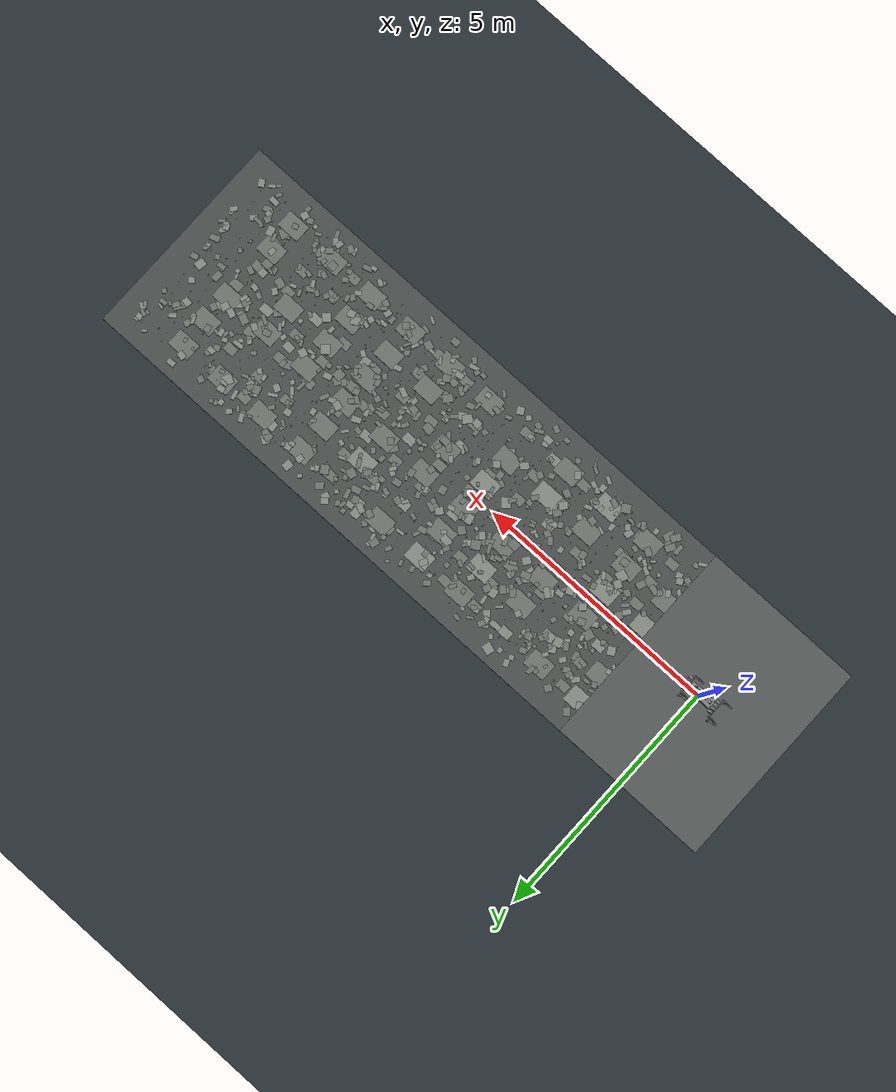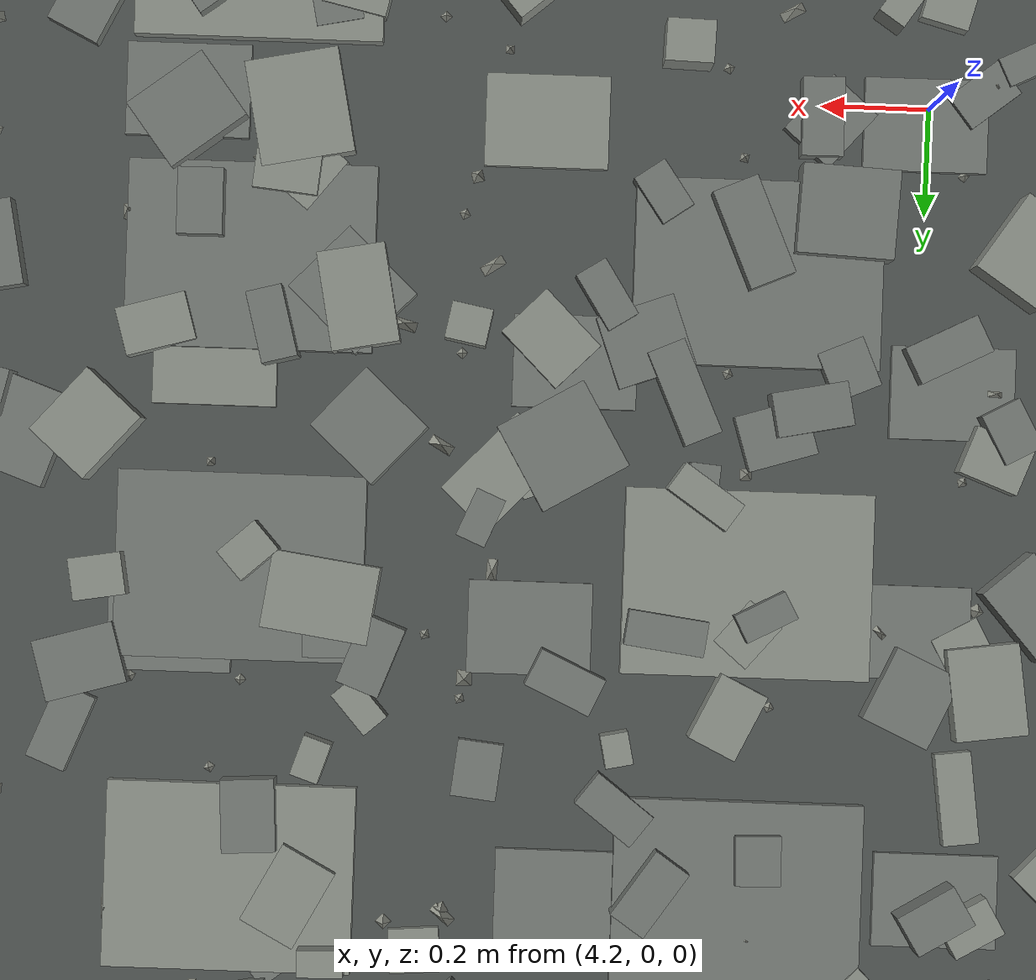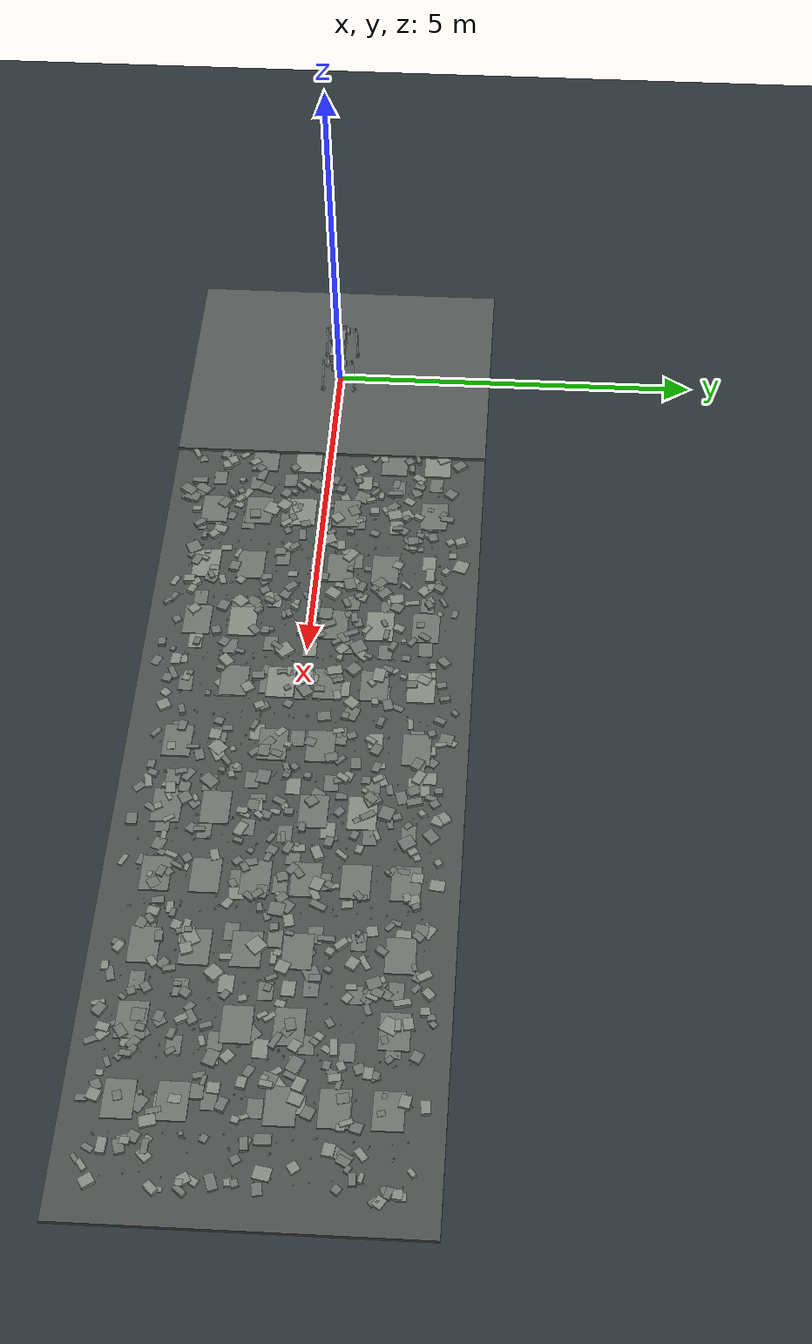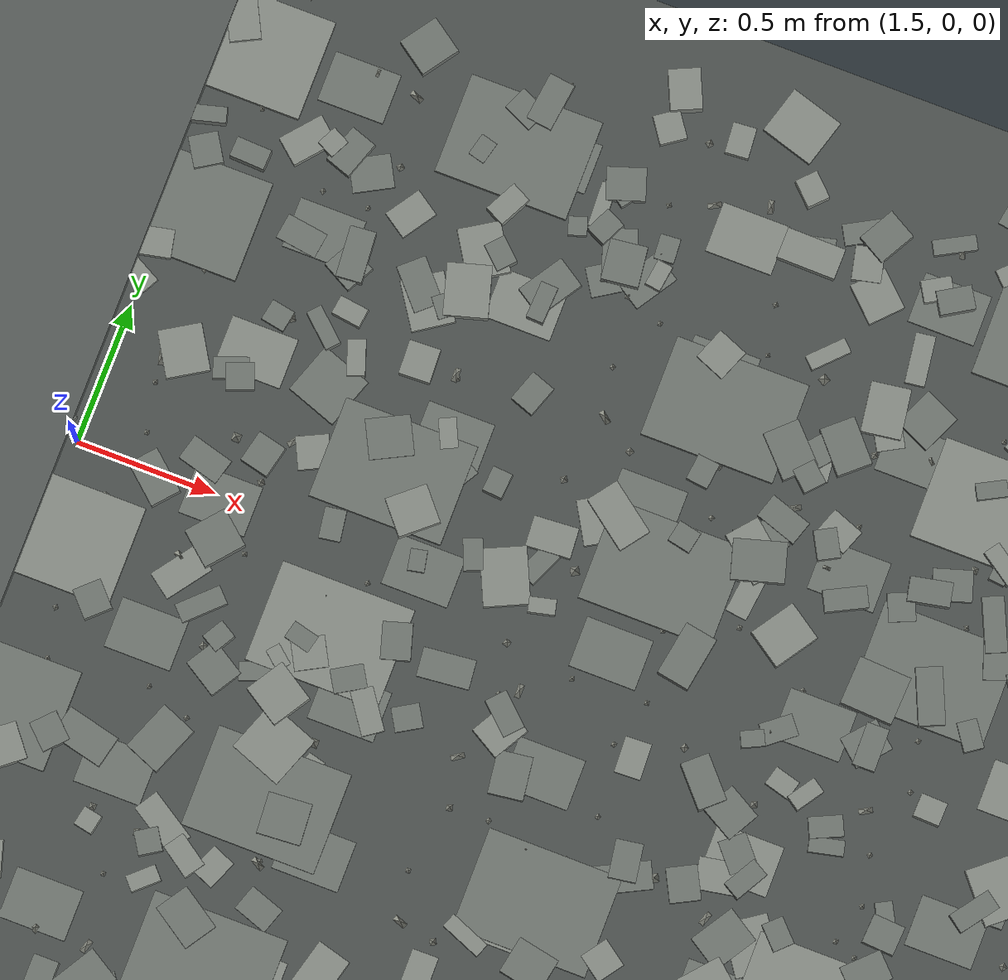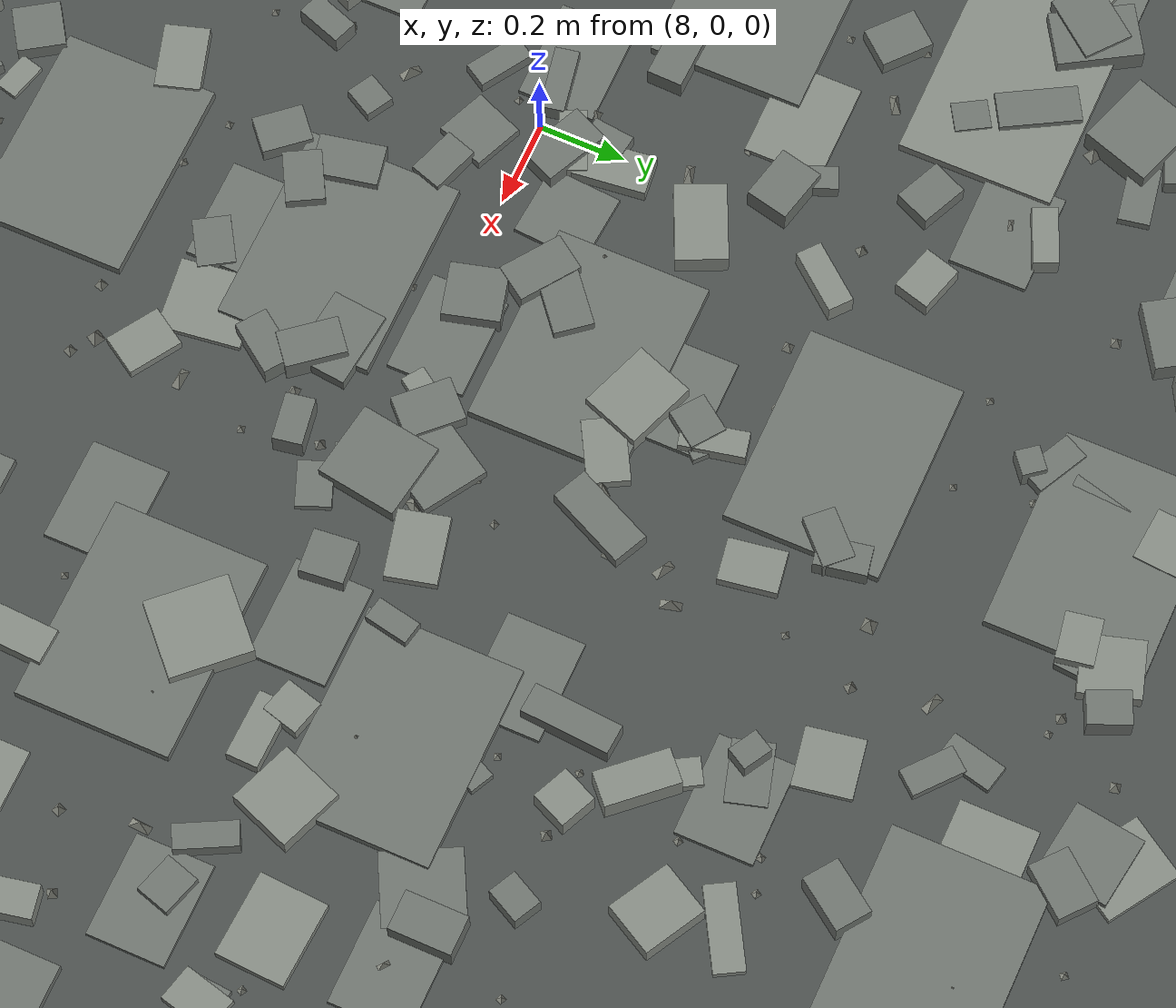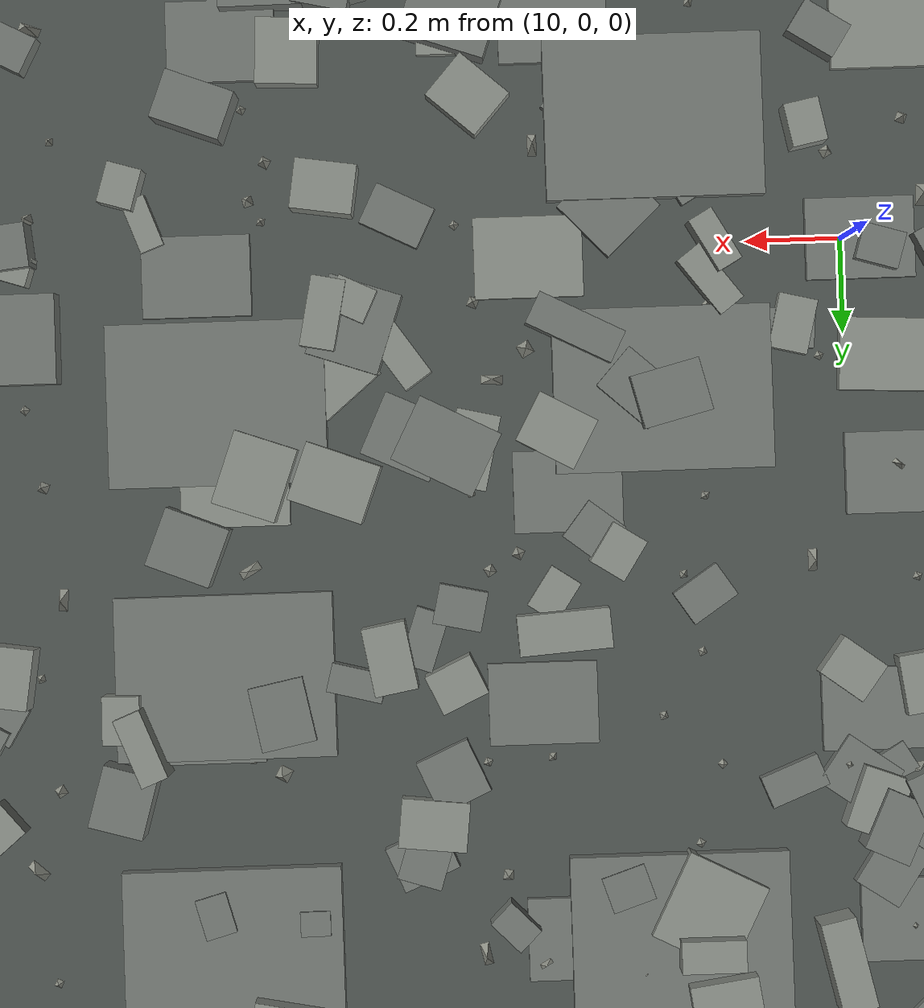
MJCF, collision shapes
<mujoco model="RM75 rough flat scene">
  <include file="RM75.xml"/>
  <include file="../rough_flat_terrain.xml"/>

  <worldbody>
    <geom name="RM75_rough_flat_catch_floor" pos="0 0 -0.145" size="0 0 0.05" type="plane" material="groundplane" friction="1.0 0.02 0.01"/>
  </worldbody>

  <keyframe>
    <key name="rough_flat_start" qpos="0 0 0.53 1 0 0 0 0 0 0 0 0 0 0 0 0 0 0 0"/>
  </keyframe>
</mujoco>

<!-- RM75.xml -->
<mujoco model="RM75_locked_arm">
  <compiler angle="radian" meshdir="../../../RM75/meshes" convexhull="false" />
  <default>
    <joint damping="0.05" armature="0.02" frictionloss="0.02" />
    <geom condim="3" friction="0.9 0.02 0.01" />
    <default class="visual">
      <geom type="mesh" contype="0" conaffinity="0" group="2" />
    </default>
  </default>
  <asset>
    <material name="rm75_grey" rgba="0.70 0.70 0.70 1" />
    <material name="rm75_white" rgba="0.92 0.92 0.92 1" />
    <mesh name="base_link_mesh" file="base_link.STL" />
    <mesh name="FL_hip_mesh" file="FL_hip.STL" />
    <mesh name="FL_thigh_mesh" file="FL_thigh.STL" />
    <mesh name="FL_calf_mesh" file="FL_calf.STL" />
    <mesh name="FR_hip_mesh" file="FR_hip.STL" />
    <mesh name="FR_thigh_mesh" file="FR_thigh.STL" />
    <mesh name="FR_calf_mesh" file="FR_calf.STL" />
    <mesh name="RL_hip_mesh" file="RL_hip.STL" />
    <mesh name="RL_thigh_mesh" file="RL_thigh.STL" />
    <mesh name="RL_calf_mesh" file="RL_calf.STL" />
    <mesh name="RR_hip_mesh" file="RR_hip.STL" />
    <mesh name="RR_thigh_mesh" file="RR_thigh.STL" />
    <mesh name="RR_calf_mesh" file="RR_calf.STL" />
    <mesh name="base_arm_mesh" file="base_arm.STL" />
    <mesh name="link1_mesh" file="link1.STL" />
    <mesh name="link2_mesh" file="link2.STL" />
    <mesh name="link3_mesh" file="link3.STL" />
    <mesh name="link4_mesh" file="link4.STL" />
    <mesh name="link5_mesh" file="link5.STL" />
    <mesh name="link6_mesh" file="link6.STL" />
    <mesh name="frame_link_mesh" file="frame_link.STL" />
    <mesh name="head_link_mesh" file="head_link.STL" />
  </asset>
  <worldbody>
    <body name="base" pos="0 0 0.53">
      <freejoint name="root" />
      <inertial pos="-0.00021911 -8.577e-08 0.074571" mass="34.6" fullinertia="0.14102 0.56124 0.62227 -1.7646e-08 2.1243e-05 -1.5055e-07" />
      <geom name="base_link_visual" type="mesh" mesh="base_link_mesh" class="visual" material="rm75_grey" />
      <geom name="base_link_collision_0" pos="0 0 0.0695" quat="1 0 0 0" group="3" type="box" size="0.25 0.1 0.075" />
      <body name="FL_hip" pos="0.209 0.07 0.0705" quat="0.999550033749 0.0299955002025 0 0">
        <joint name="FL_hip_joint" axis="1 0 0" range="-0.93 0.81" />
        <inertial pos="0.11205 -0.016879 9.3139e-08" mass="2.9462" fullinertia="0.002834 0.0043473 0.0023086 -7.843e-06 -3.5056e-07 1.7625e-08" />
        <geom name="FL_hip_visual" type="mesh" mesh="FL_hip_mesh" class="visual" material="rm75_grey" />
        <geom name="FL_hip_collision_0" pos="0.12 -0.027 0" quat="0.707106781187 0.707106781187 0 0" group="3" type="cylinder" size="0.0535 0.0205" />
        <body name="FL_thigh" pos="0.12003 0.0485 0" quat="0.939372712847 0 0.342897807455 0">
          <joint name="FL_thigh_joint" axis="0 1 0" range="-1.64 3.99" />
          <inertial pos="-0.0059037 0.027545 -0.041279" mass="4.8086" fullinertia="0.03732 0.038716 0.0061113 0.00048305 -0.0031358 0.0034367" />
          <geom name="FL_thigh_visual" type="mesh" mesh="FL_thigh_mesh" class="visual" material="rm75_grey" />
          <geom name="FL_thigh_collision_0" pos="-0.018 0.075 -0.075" quat="0.605820156643 -0 0.795601620036 -0" group="3" type="box" size="0.0575 0.012 0.0225" />
          <geom name="FL_thigh_collision_1" pos="-0.03 0.075 -0.175" quat="0.707105482511 -0 0.707108079859 -0" group="3" type="box" size="0.085 0.012 0.019" />
          <geom name="FL_thigh_collision_2" pos="-3e-05 -0.001514 0" quat="0.707106781187 0.707106781187 0 0" group="3" type="cylinder" size="0.0535 0.0205" />
          <body name="FL_calf" pos="-0.00019314 0.065988 -0.35012" quat="0.82533561491 2.51705453774e-15 -0.564642473395 -1.66858366835e-15">
            <joint name="FL_calf_joint" axis="0 1 0" range="-1.62 0.77" />
            <inertial pos="0.022587 0.0094042 -0.20806" mass="0.5299" fullinertia="0.0066551 0.0068264 0.00033464 1.2646e-06 0.00078306 -9.4791e-06" />
            <geom name="FL_calf_visual" type="mesh" mesh="FL_calf_mesh" class="visual" material="rm75_grey" />
            <geom name="FL_calf_collision_0" pos="0.0082 0.0094 -0.04" quat="0.813791292233 0 0.581157235769 0" group="3" type="box" size="0.05 0.01225 0.009" />
            <geom name="FL_calf_collision_1" pos="0.0308 0.0094 -0.1025" quat="0.808469139581 0 0.588538571671 0" group="3" type="box" size="0.05 0.01225 0.009" />
            <geom name="FL_calf_collision_2" pos="0.0498 0.0094 -0.225" quat="0.70494551729 -0 0.709261459303 -0" group="3" type="box" size="0.075 0.01225 0.0075" />
            <geom name="FL_calf_collision_3" pos="0.0294 0.0094 -0.3125" quat="0.484416730419 0 0.874837374196 0" group="3" type="box" size="0.0325 0.014 0.0175" />
            <body name="FL_foot" pos="0 0 -0.35" quat="1 0 0 0">
              <inertial pos="0 0 0" mass="0.04" fullinertia="9.6e-06 9.6e-06 9.6e-06 0 0 0" />
              <geom name="FL_foot_collision_0" pos="0 0 0" quat="1 0 0 0" group="3" type="sphere" size="0.032" />
            </body>
          </body>
        </body>
      </body>
      <body name="FR_hip" pos="0.219 -0.07 0.0705" quat="0.999550033749 -0.0299955002025 -0 0">
        <joint name="FR_hip_joint" axis="1 0 0" range="-0.81 0.93" />
        <inertial pos="0.10205 0.016879 1.9176e-08" mass="2.9462" fullinertia="0.0028341 0.0043473 0.0023085 7.8432e-06 1.0483e-07 1.3798e-08" />
        <geom name="FR_hip_visual" type="mesh" mesh="FR_hip_mesh" class="visual" material="rm75_grey" />
        <geom name="FR_hip_collision_0" pos="0.11 0.027 0" quat="0.707106781187 0.707106781187 0 0" group="3" type="cylinder" size="0.0535 0.0205" />
        <body name="FR_thigh" pos="0.10979 -0.0485 -5.5285e-05" quat="0.939372712847 0 0.342897807455 0">
          <joint name="FR_thigh_joint" axis="0 1 0" range="-1.64 3.99" />
          <inertial pos="-0.0057859 -0.027545 -0.041242" mass="4.8081" fullinertia="0.037305 0.038702 0.0061115 -0.00048278 -0.0031376 -0.0034355" />
          <geom name="FR_thigh_visual" type="mesh" mesh="FR_thigh_mesh" class="visual" material="rm75_grey" />
          <geom name="FR_thigh_collision_0" pos="-0.018 -0.075 -0.075" quat="0.605820156643 -0 0.795601620036 -0" group="3" type="box" size="0.0575 0.012 0.0225" />
          <geom name="FR_thigh_collision_1" pos="-0.03 -0.075 -0.175" quat="0.707105482511 -0 0.707108079859 -0" group="3" type="box" size="0.085 0.012 0.019" />
          <geom name="FR_thigh_collision_2" pos="0.00021 0.001382 6e-05" quat="0.707106781187 0.707106781187 0 0" group="3" type="cylinder" size="0.0535 0.0205" />
          <body name="FR_calf" pos="-0.00034533 -0.065724 -0.34993" quat="0.82533561491 2.51705453774e-15 -0.564642473395 -1.66858366835e-15">
            <joint name="FR_calf_joint" axis="0 1 0" range="-1.62 0.77" />
            <inertial pos="0.026193 -0.0095278 -0.20763" mass="0.5299" fullinertia="0.0066258 0.0068264 0.00036386 -1.3857e-08 0.00089235 6.3149e-08" />
            <geom name="FR_calf_visual" type="mesh" mesh="FR_calf_mesh" class="visual" material="rm75_grey" />
            <geom name="FR_calf_collision_0" pos="0.0089 -0.0095 -0.04" quat="0.818787794874 0 0.57409628719 0" group="3" type="box" size="0.05 0.01225 0.009" />
            <geom name="FR_calf_collision_1" pos="0.0331 -0.0095 -0.1025" quat="0.811869045746 0 0.583839577761 0" group="3" type="box" size="0.05 0.01225 0.009" />
            <geom name="FR_calf_collision_2" pos="0.0539 -0.0095 -0.225" quat="0.709470322406 0 0.704735313167 0" group="3" type="box" size="0.075 0.01225 0.0075" />
            <geom name="FR_calf_collision_3" pos="0.0366 -0.0095 -0.3125" quat="0.5161042138 -0 0.85652579675 -0" group="3" type="box" size="0.0325 0.014 0.0175" />
            <body name="FR_foot" pos="0 0 -0.35" quat="1 0 0 0">
              <inertial pos="0 0 0" mass="0.04" fullinertia="9.6e-06 9.6e-06 9.6e-06 0 0 0" />
              <geom name="FR_foot_collision_0" pos="0 0 0" quat="1 0 0 0" group="3" type="sphere" size="0.032" />
            </body>
          </body>
        </body>
      </body>
      <body name="RL_hip" pos="-0.219 0.07 0.0705" quat="0.999550033749 0.0299955002025 0 0">
        <joint name="RL_hip_joint" axis="1 0 0" range="-0.93 0.81" />
        <inertial pos="-0.10105 -0.016879 -9.3139e-08" mass="2.9462" fullinertia="0.002834 0.0043473 0.0023086 7.843e-06 -3.5056e-07 -1.7625e-08" />
        <geom name="RL_hip_visual" type="mesh" mesh="RL_hip_mesh" class="visual" material="rm75_grey" />
        <geom name="RL_hip_collision_0" pos="-0.109 -0.027 0" quat="0.707106781187 0.707106781187 0 0" group="3" type="cylinder" size="0.0535 0.0205" />
        <body name="RL_thigh" pos="-0.10897 0.0475 0" quat="0.930507621912 0 0.366272529086 0">
          <joint name="RL_thigh_joint" axis="0 1 0" range="-1.69 3.94" />
          <inertial pos="-0.005904 0.027545 -0.041278" mass="4.8086" fullinertia="0.03732 0.038716 0.0061113 0.00048304 -0.0031358 0.0034368" />
          <geom name="RL_thigh_visual" type="mesh" mesh="RL_thigh_mesh" class="visual" material="rm75_grey" />
          <geom name="RL_thigh_collision_0" pos="-0.018 0.075 -0.075" quat="0.605820156643 -0 0.795601620036 -0" group="3" type="box" size="0.0575 0.012 0.0225" />
          <geom name="RL_thigh_collision_1" pos="-0.03 0.075 -0.175" quat="0.707105482511 -0 0.707108079859 -0" group="3" type="box" size="0.085 0.012 0.019" />
          <geom name="RL_thigh_collision_2" pos="-3e-05 -0.001514 0" quat="0.707106781187 0.707106781187 0 0" group="3" type="cylinder" size="0.0535 0.0205" />
          <body name="RL_calf" pos="-0.00019314 0.065988 -0.35012" quat="0.83232898352 2.53771464811e-15 -0.554281934752 -1.63699094958e-15">
            <joint name="RL_calf_joint" axis="0 1 0" range="-1.645 0.745" />
            <inertial pos="0.022587 0.0094042 -0.20806" mass="0.5299" fullinertia="0.0066551 0.0068264 0.00033464 1.2646e-06 0.00078306 -9.4791e-06" />
            <geom name="RL_calf_visual" type="mesh" mesh="RL_calf_mesh" class="visual" material="rm75_grey" />
            <geom name="RL_calf_collision_0" pos="0.0082 0.0094 -0.04" quat="0.813791292233 0 0.581157235769 0" group="3" type="box" size="0.05 0.01225 0.009" />
            <geom name="RL_calf_collision_1" pos="0.0308 0.0094 -0.1025" quat="0.808469139581 0 0.588538571671 0" group="3" type="box" size="0.05 0.01225 0.009" />
            <geom name="RL_calf_collision_2" pos="0.0498 0.0094 -0.225" quat="0.70494551729 -0 0.709261459303 -0" group="3" type="box" size="0.075 0.01225 0.0075" />
            <geom name="RL_calf_collision_3" pos="0.0294 0.0094 -0.3125" quat="0.484416730419 0 0.874837374196 0" group="3" type="box" size="0.0325 0.014 0.0175" />
            <body name="RL_foot" pos="0 0 -0.35" quat="1 0 0 0">
              <inertial pos="0 0 0" mass="0.04" fullinertia="9.6e-06 9.6e-06 9.6e-06 0 0 0" />
              <geom name="RL_foot_collision_0" pos="0 0 0" quat="1 0 0 0" group="3" type="sphere" size="0.032" />
            </body>
          </body>
        </body>
      </body>
      <body name="RR_hip" pos="-0.219 -0.07 0.0705" quat="0.999550033749 -0.0299955002025 -0 0">
        <joint name="RR_hip_joint" axis="1 0 0" range="-0.81 0.93" />
        <inertial pos="-0.10105 0.016879 9.3139e-08" mass="2.9462" fullinertia="0.002834 0.0043473 0.0023086 -7.843e-06 3.509e-07 -1.7625e-08" />
        <geom name="RR_hip_visual" type="mesh" mesh="RR_hip_mesh" class="visual" material="rm75_grey" />
        <geom name="RR_hip_collision_0" pos="-0.109 0.027 0" quat="0.707106781187 0.707106781187 0 0" group="3" type="cylinder" size="0.0535 0.0205" />
        <body name="RR_thigh" pos="-0.10921 -0.0475 -5.5285e-05" quat="0.930507621912 0 0.366272529086 0">
          <joint name="RR_thigh_joint" axis="0 1 0" range="-1.69 3.94" />
          <inertial pos="-0.0057859 -0.027545 -0.041242" mass="4.8081" fullinertia="0.037305 0.038702 0.0061115 -0.00048278 -0.0031376 -0.0034355" />
          <geom name="RR_thigh_visual" type="mesh" mesh="RR_thigh_mesh" class="visual" material="rm75_grey" />
          <geom name="RR_thigh_collision_0" pos="-0.018 -0.075 -0.075" quat="0.605820156643 -0 0.795601620036 -0" group="3" type="box" size="0.0575 0.012 0.0225" />
          <geom name="RR_thigh_collision_1" pos="-0.03 -0.075 -0.175" quat="0.707105482511 -0 0.707108079859 -0" group="3" type="box" size="0.085 0.012 0.019" />
          <geom name="RR_thigh_collision_2" pos="0.00021 0.001382 6e-05" quat="0.707106781187 0.707106781187 0 0" group="3" type="cylinder" size="0.0535 0.0205" />
          <body name="RR_calf" pos="-0.00034533 -0.065724 -0.34993" quat="0.83232898352 2.53771464811e-15 -0.554281934752 -1.63699094958e-15">
            <joint name="RR_calf_joint" axis="0 1 0" range="-1.645 0.745" />
            <inertial pos="0.026193 -0.0095278 -0.20763" mass="0.5299" fullinertia="0.0066258 0.0068264 0.00036386 -1.398e-08 0.00089236 6.2692e-08" />
            <geom name="RR_calf_visual" type="mesh" mesh="RR_calf_mesh" class="visual" material="rm75_grey" />
            <geom name="RR_calf_collision_0" pos="0.0089 -0.0095 -0.04" quat="0.818787794874 0 0.57409628719 0" group="3" type="box" size="0.05 0.01225 0.009" />
            <geom name="RR_calf_collision_1" pos="0.0331 -0.0095 -0.1025" quat="0.811869045746 0 0.583839577761 0" group="3" type="box" size="0.05 0.01225 0.009" />
            <geom name="RR_calf_collision_2" pos="0.0539 -0.0095 -0.225" quat="0.709470322406 0 0.704735313167 0" group="3" type="box" size="0.075 0.01225 0.0075" />
            <geom name="RR_calf_collision_3" pos="0.0366 -0.0095 -0.3125" quat="0.5161042138 -0 0.85652579675 -0" group="3" type="box" size="0.0325 0.014 0.0175" />
            <body name="RR_foot" pos="0 0 -0.35" quat="1 0 0 0">
              <inertial pos="0 0 0" mass="0.04" fullinertia="9.6e-06 9.6e-06 9.6e-06 0 0 0" />
              <geom name="RR_foot_collision_0" pos="0 0 0" quat="1 0 0 0" group="3" type="sphere" size="0.032" />
            </body>
          </body>
        </body>
      </body>
      <body name="base_arm" pos="0.16 0 0.147" quat="1 0 0 0">
        <inertial pos="-0.0057371 3.3089e-07 0.021574" mass="1.2829" fullinertia="0.0010361 0.0011971 0.0015394 6.5867e-09 -3.9093e-05 7.3288e-10" />
        <geom name="base_arm_visual" type="mesh" mesh="base_arm_mesh" class="visual" material="rm75_grey" />
        <geom name="base_arm_collision_0" pos="0 0 0.0255" quat="1 0 0 0" group="3" type="cylinder" size="0.0325 0.0255" />
        <body name="link1" pos="0 0 0.0585" quat="1 0 0 0">
          <inertial pos="-8.1037e-08 7.127e-08 0.022725" mass="1.8285" fullinertia="0.0043121 0.0010993 0.0041456 3.4622e-08 -3.2753e-09 2.5967e-09" />
          <geom name="link1_visual" type="mesh" mesh="link1_mesh" class="visual" material="rm75_grey" />
          <geom name="link1_collision_0" pos="0 0 0" quat="1 0 0 0" group="3" type="mesh" mesh="link1_mesh" />
          <body name="link2" pos="0 0 0.045" quat="1 0 0 0">
            <inertial pos="-0.11245 0.0027633 -2.7613e-06" mass="3.2348" fullinertia="0.0022244 0.04627 0.047171 0.0019632 -1.5622e-06 -2.5099e-08" />
            <geom name="link2_visual" type="mesh" mesh="link2_mesh" class="visual" material="rm75_grey" />
            <geom name="link2_collision_0" pos="0 0 0" quat="0.707106781187 0.707106781187 0 0" group="3" type="cylinder" size="0.0325 0.051" />
            <geom name="link2_collision_1" pos="-0.1625 0 0" quat="0.707106781187 0 0.707106781187 0" group="3" type="cylinder" size="0.0225 0.1175" />
            <geom name="link2_collision_2" pos="-0.35 0 0" quat="0.707106781187 0.707106781187 0 0" group="3" type="cylinder" size="0.0325 0.0255" />
            <body name="link3" pos="-0.35 0.0227 0" quat="1 0 0 0">
              <inertial pos="0.10443 -0.02836 0.037705" mass="2.2791" fullinertia="0.002487 0.02121 0.019757 -0.0003066 -0.0044269 -0.00010369" />
              <geom name="link3_visual" type="mesh" mesh="link3_mesh" class="visual" material="rm75_grey" />
              <geom name="link3_collision_0" pos="0.128 -0.0227 0.055" quat="0.707106781187 0 0.707106781187 0" group="3" type="cylinder" size="0.02 0.058" />
              <geom name="link3_collision_1" pos="0.2205 -0.0227 0.055" quat="0.5 -0.5 0.5 0.5" group="3" type="cylinder" size="0.0325 0.0295" />
              <body name="link4" pos="0.218 0.00019997 0.056998" quat="1 0 0 0">
                <inertial pos="0.056041 -0.016629 -0.0059401" mass="1.5316" fullinertia="0.00095965 0.0019329 0.0020218 0.00045143 8.6316e-05 -4.4149e-05" />
                <geom name="link4_visual" type="mesh" mesh="link4_mesh" class="visual" material="rm75_grey" />
                <geom name="link4_collision_0" pos="0.072 -0.02289997 2e-06" quat="1 0 0 0" group="3" type="cylinder" size="0.0325 0.0335" />
                <body name="link5" pos="0.072 -0.0225 0.0228" quat="1 0 0 0">
                  <inertial pos="0.020886 4.4777e-07 -0.0079004" mass="1.0574" fullinertia="0.00063912 0.00089439 0.00082434 -7.591e-09 0.00028924 6.4337e-09" />
                  <geom name="link5_visual" type="mesh" mesh="link5_mesh" class="visual" material="rm75_grey" />
                  <geom name="link5_collision_0" pos="0 0 0" quat="1 0 0 0" group="3" type="mesh" mesh="link5_mesh" />
                  <body name="link6" pos="0.0469 0 -0.0228" quat="1 0 0 0">
                    <inertial pos="0.024734 1.1095e-05 -2.6661e-05" mass="0.78415" fullinertia="0.0004075 0.00036244 0.00036313 -2.1698e-07 5.2406e-07 -3.4388e-07" />
                    <geom name="link6_visual" type="mesh" mesh="link6_mesh" class="visual" material="rm75_grey" />
                    <geom name="link6_collision_0" pos="0.0258 -0.00039997 2e-06" quat="0.707106781187 0 0.707106781187 0" group="3" type="cylinder" size="0.0325 0.0255" />
                  </body>
                </body>
              </body>
            </body>
          </body>
        </body>
      </body>
      <body name="frame_link" pos="-0.11 0 0.149" quat="1 0 0 0">
        <inertial pos="-4.1633e-17 5.5511e-17 0.034508" mass="12.999" fullinertia="0.08192 0.14951 0.20526 1.0402e-17 1.8321e-18 -1.4563e-17" />
        <geom name="frame_link_visual" type="mesh" mesh="frame_link_mesh" class="visual" material="rm75_grey" />
        <geom name="frame_link_collision_0" pos="0 0 0" quat="1 0 0 0" group="3" type="mesh" mesh="frame_link_mesh" />
      </body>
      <body name="head_link" pos="0.30205 7e-05 0.13126" quat="1 0 0 0">
        <inertial pos="0.046678 -0.00018035 -0.036525" mass="3" fullinertia="0.0063047 0.0075614 0.0082758 4.6233e-06 0.0008403 2.4641e-06" />
        <geom name="head_link_visual" type="mesh" mesh="head_link_mesh" class="visual" material="rm75_grey" />
        <geom name="head_link_collision_0" pos="0.10795 -7e-05 -0.05576" quat="1 0 0 0" group="3" type="box" size="0.02 0.06 0.07" />
        <geom name="head_link_collision_1" pos="0.045 0 0.0175" quat="1 0 0 0" group="3" type="box" size="0.055 0.045 0.012" />
      </body>
    </body>
  </worldbody>
  <actuator>
    <motor name="FL_hip_joint_motor" joint="FL_hip_joint" ctrllimited="true" ctrlrange="-200 200" />
    <motor name="FL_thigh_joint_motor" joint="FL_thigh_joint" ctrllimited="true" ctrlrange="-200 200" />
    <motor name="FL_calf_joint_motor" joint="FL_calf_joint" ctrllimited="true" ctrlrange="-320 320" />
    <motor name="FR_hip_joint_motor" joint="FR_hip_joint" ctrllimited="true" ctrlrange="-200 200" />
    <motor name="FR_thigh_joint_motor" joint="FR_thigh_joint" ctrllimited="true" ctrlrange="-200 200" />
    <motor name="FR_calf_joint_motor" joint="FR_calf_joint" ctrllimited="true" ctrlrange="-320 320" />
    <motor name="RL_hip_joint_motor" joint="RL_hip_joint" ctrllimited="true" ctrlrange="-200 200" />
    <motor name="RL_thigh_joint_motor" joint="RL_thigh_joint" ctrllimited="true" ctrlrange="-200 200" />
    <motor name="RL_calf_joint_motor" joint="RL_calf_joint" ctrllimited="true" ctrlrange="-320 320" />
    <motor name="RR_hip_joint_motor" joint="RR_hip_joint" ctrllimited="true" ctrlrange="-200 200" />
    <motor name="RR_thigh_joint_motor" joint="RR_thigh_joint" ctrllimited="true" ctrlrange="-200 200" />
    <motor name="RR_calf_joint_motor" joint="RR_calf_joint" ctrllimited="true" ctrlrange="-320 320" />
  </actuator>
</mujoco>

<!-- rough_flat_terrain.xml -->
<mujoco model="shared rough flat terrain">
  <statistic center="5.8 0 0.55" extent="6.8"/>

  <visual>
    <headlight diffuse="0.6 0.6 0.6" ambient="0.25 0.25 0.25" specular="0.3 0.3 0.3"/>
    <rgba haze="0.15 0.25 0.35 1"/>
    <global azimuth="-140" elevation="-20"/>
  </visual>

  <asset>
    <texture type="skybox" builtin="flat" rgb1="0 0 0" rgb2="0 0 0" width="512" height="3072"/>
    <texture type="2d" name="groundplane" builtin="checker" mark="edge" rgb1="0.20 0.24 0.26" rgb2="0.12 0.15 0.16" markrgb="0.75 0.75 0.75" width="300" height="300"/>
    <material name="groundplane" texture="groundplane" texuniform="true" texrepeat="6 6" reflectance="0.05"/>
    <material name="rough_start" rgba="0.33 0.35 0.34 1" specular="0.08" shininess="0.1"/>
    <material name="rough_tile" rgba="0.43 0.45 0.43 1" specular="0.05" shininess="0.08"/>
    <material name="rough_pit" rgba="0.29 0.31 0.30 1" specular="0.03" shininess="0.05"/>
    <material name="rough_high" rgba="0.52 0.54 0.51 1" specular="0.05" shininess="0.08"/>
    <material name="rough_spike" rgba="0.55 0.56 0.52 1" specular="0.04" shininess="0.08"/>

    <mesh name="rough_spike_s" vertex="-0.008 -0.008 0 0.008 -0.008 0 0.008 0.008 0 -0.008 0.008 0 0 0 0.012" face="0 1 4 1 2 4 2 3 4 3 0 4 0 3 2 0 2 1"/>
    <mesh name="rough_spike_m" vertex="-0.011 -0.011 0 0.011 -0.011 0 0.011 0.011 0 -0.011 0.011 0 0 0 0.022" face="0 1 4 1 2 4 2 3 4 3 0 4 0 3 2 0 2 1"/>
    <mesh name="rough_spike_l" vertex="-0.015 -0.015 0 0.015 -0.015 0 0.015 0.015 0 -0.015 0.015 0 0 0 0.032" face="0 1 4 1 2 4 2 3 4 3 0 4 0 3 2 0 2 1"/>
    <mesh name="rough_spike_w" vertex="-0.024 -0.010 0 0.024 -0.010 0 0.024 0.010 0 -0.024 0.010 0 0 0 0.028" face="0 1 4 1 2 4 2 3 4 3 0 4 0 3 2 0 2 1"/>
  </asset>

  <worldbody>
    <light pos="4 0 5" dir="0 0 -1" directional="true"/>
    <geom name="visual_floor" pos="5.8 0 -0.16" size="0 0 0.05" type="plane" material="groundplane" contype="0" conaffinity="0"/>
    <geom name="startup_pad" pos="-0.20 0 -0.080" size="1.65 2.15 0.025" type="box" material="rough_start" friction="1.0 0.02 0.01"/>
    <geom name="rough_underlay" pos="6.90 0 -0.145" size="5.90 2.15 0.025" type="box" material="rough_pit" friction="1.0 0.02 0.01"/>

    <!-- Dense small square blocks fill between the main roughness features. -->
    <geom name="micro_block_000" pos="1.213 -1.518 -0.114" size="0.120 0.090 0.006" type="box" material="rough_tile" friction="1.0 0.02 0.01"/>
    <geom name="micro_block_001" pos="1.283 -1.000 -0.114" size="0.120 0.090 0.006" type="box" material="rough_tile" friction="1.0 0.02 0.01"/>
    <geom name="micro_block_002" pos="1.213 -0.482 -0.114" size="0.120 0.090 0.006" type="box" material="rough_tile" friction="1.0 0.02 0.01"/>
    <geom name="micro_block_003" pos="1.283 -0.018 -0.114" size="0.120 0.090 0.006" type="box" material="rough_high" friction="1.0 0.02 0.01"/>
    <geom name="micro_block_004" pos="1.213 0.500 -0.114" size="0.120 0.090 0.006" type="box" material="rough_tile" friction="1.0 0.02 0.01"/>
    <geom name="micro_block_005" pos="1.283 1.018 -0.114" size="0.120 0.090 0.006" type="box" material="rough_tile" friction="1.0 0.02 0.01"/>
    <geom name="micro_block_006" pos="1.213 1.482 -0.114" size="0.120 0.090 0.006" type="box" material="rough_high" friction="1.0 0.02 0.01"/>
    <geom name="micro_block_007" pos="1.945 -1.500 -0.114" size="0.120 0.090 0.006" type="box" material="rough_tile" friction="1.0 0.02 0.01"/>
    <geom name="micro_block_008" pos="2.015 -0.982 -0.114" size="0.120 0.090 0.006" type="box" material="rough_tile" friction="1.0 0.02 0.01"/>
    <geom name="micro_block_009" pos="1.945 -0.518 -0.114" size="0.120 0.090 0.006" type="box" material="rough_tile" friction="1.0 0.02 0.01"/>
    <geom name="micro_block_010" pos="2.015 0.000 -0.114" size="0.120 0.090 0.006" type="box" material="rough_tile" friction="1.0 0.02 0.01"/>
    <geom name="micro_block_011" pos="1.945 0.518 -0.114" size="0.120 0.090 0.006" type="box" material="rough_high" friction="1.0 0.02 0.01"/>
    <geom name="micro_block_012" pos="2.015 0.982 -0.114" size="0.120 0.090 0.006" type="box" material="rough_tile" friction="1.0 0.02 0.01"/>
    <geom name="micro_block_013" pos="1.945 1.500 -0.114" size="0.120 0.090 0.006" type="box" material="rough_tile" friction="1.0 0.02 0.01"/>
    <geom name="micro_block_014" pos="2.677 -1.482 -0.114" size="0.120 0.090 0.006" type="box" material="rough_high" friction="1.0 0.02 0.01"/>
    <geom name="micro_block_015" pos="2.747 -1.018 -0.114" size="0.120 0.090 0.006" type="box" material="rough_tile" friction="1.0 0.02 0.01"/>
    <geom name="micro_block_016" pos="2.677 -0.500 -0.114" size="0.120 0.090 0.006" type="box" material="rough_tile" friction="1.0 0.02 0.01"/>
    <geom name="micro_block_017" pos="2.747 0.018 -0.114" size="0.120 0.090 0.006" type="box" material="rough_tile" friction="1.0 0.02 0.01"/>
    <geom name="micro_block_018" pos="2.677 0.482 -0.114" size="0.120 0.090 0.006" type="box" material="rough_tile" friction="1.0 0.02 0.01"/>
    <geom name="micro_block_019" pos="2.747 1.000 -0.114" size="0.120 0.090 0.006" type="box" material="rough_high" friction="1.0 0.02 0.01"/>
    <geom name="micro_block_020" pos="2.677 1.518 -0.114" size="0.120 0.090 0.006" type="box" material="rough_tile" friction="1.0 0.02 0.01"/>
    <geom name="micro_block_021" pos="3.373 -1.518 -0.114" size="0.120 0.090 0.006" type="box" material="rough_tile" friction="1.0 0.02 0.01"/>
    <geom name="micro_block_022" pos="3.443 -1.000 -0.114" size="0.120 0.090 0.006" type="box" material="rough_high" friction="1.0 0.02 0.01"/>
    <geom name="micro_block_023" pos="3.373 -0.482 -0.114" size="0.120 0.090 0.006" type="box" material="rough_tile" friction="1.0 0.02 0.01"/>
    <geom name="micro_block_024" pos="3.443 -0.018 -0.114" size="0.120 0.090 0.006" type="box" material="rough_tile" friction="1.0 0.02 0.01"/>
    <geom name="micro_block_025" pos="3.373 0.500 -0.114" size="0.120 0.090 0.006" type="box" material="rough_tile" friction="1.0 0.02 0.01"/>
    <geom name="micro_block_026" pos="3.443 1.018 -0.114" size="0.120 0.090 0.006" type="box" material="rough_tile" friction="1.0 0.02 0.01"/>
    <geom name="micro_block_027" pos="3.373 1.482 -0.114" size="0.120 0.090 0.006" type="box" material="rough_high" friction="1.0 0.02 0.01"/>
    <geom name="micro_block_028" pos="4.105 -1.500 -0.114" size="0.120 0.090 0.006" type="box" material="rough_tile" friction="1.0 0.02 0.01"/>
    <geom name="micro_block_029" pos="4.175 -0.982 -0.114" size="0.120 0.090 0.006" type="box" material="rough_tile" friction="1.0 0.02 0.01"/>
    <geom name="micro_block_030" pos="4.105 -0.518 -0.114" size="0.120 0.090 0.006" type="box" material="rough_high" friction="1.0 0.02 0.01"/>
    <geom name="micro_block_031" pos="4.175 0.000 -0.114" size="0.120 0.090 0.006" type="box" material="rough_tile" friction="1.0 0.02 0.01"/>
    <geom name="micro_block_032" pos="4.105 0.518 -0.114" size="0.120 0.090 0.006" type="box" material="rough_tile" friction="1.0 0.02 0.01"/>
    <geom name="micro_block_033" pos="4.175 0.982 -0.114" size="0.120 0.090 0.006" type="box" material="rough_tile" friction="1.0 0.02 0.01"/>
    <geom name="micro_block_034" pos="4.105 1.500 -0.114" size="0.120 0.090 0.006" type="box" material="rough_tile" friction="1.0 0.02 0.01"/>
    <geom name="micro_block_035" pos="4.837 -1.482 -0.114" size="0.120 0.090 0.006" type="box" material="rough_high" friction="1.0 0.02 0.01"/>
    <geom name="micro_block_036" pos="4.907 -1.018 -0.114" size="0.120 0.090 0.006" type="box" material="rough_tile" friction="1.0 0.02 0.01"/>
    <geom name="micro_block_037" pos="4.837 -0.500 -0.114" size="0.120 0.090 0.006" type="box" material="rough_tile" friction="1.0 0.02 0.01"/>
    <geom name="micro_block_038" pos="4.907 0.018 -0.114" size="0.120 0.090 0.006" type="box" material="rough_high" friction="1.0 0.02 0.01"/>
    <geom name="micro_block_039" pos="4.837 0.482 -0.114" size="0.120 0.090 0.006" type="box" material="rough_tile" friction="1.0 0.02 0.01"/>
    <geom name="micro_block_040" pos="4.907 1.000 -0.114" size="0.120 0.090 0.006" type="box" material="rough_tile" friction="1.0 0.02 0.01"/>
    <geom name="micro_block_041" pos="4.837 1.518 -0.114" size="0.120 0.090 0.006" type="box" material="rough_tile" friction="1.0 0.02 0.01"/>
    <geom name="micro_block_042" pos="5.533 -1.518 -0.114" size="0.120 0.090 0.006" type="box" material="rough_tile" friction="1.0 0.02 0.01"/>
    <geom name="micro_block_043" pos="5.603 -1.000 -0.114" size="0.120 0.090 0.006" type="box" material="rough_high" friction="1.0 0.02 0.01"/>
    <geom name="micro_block_044" pos="5.533 -0.482 -0.114" size="0.120 0.090 0.006" type="box" material="rough_tile" friction="1.0 0.02 0.01"/>
    <geom name="micro_block_045" pos="5.603 -0.018 -0.114" size="0.120 0.090 0.006" type="box" material="rough_tile" friction="1.0 0.02 0.01"/>
    <geom name="micro_block_046" pos="5.533 0.500 -0.114" size="0.120 0.090 0.006" type="box" material="rough_high" friction="1.0 0.02 0.01"/>
    <geom name="micro_block_047" pos="5.603 1.018 -0.114" size="0.120 0.090 0.006" type="box" material="rough_tile" friction="1.0 0.02 0.01"/>
    <geom name="micro_block_048" pos="5.533 1.482 -0.114" size="0.120 0.090 0.006" type="box" material="rough_tile" friction="1.0 0.02 0.01"/>
    <geom name="micro_block_049" pos="6.265 -1.500 -0.114" size="0.120 0.090 0.006" type="box" material="rough_tile" friction="1.0 0.02 0.01"/>
    <geom name="micro_block_050" pos="6.335 -0.982 -0.114" size="0.120 0.090 0.006" type="box" material="rough_tile" friction="1.0 0.02 0.01"/>
    <geom name="micro_block_051" pos="6.265 -0.518 -0.114" size="0.120 0.090 0.006" type="box" material="rough_high" friction="1.0 0.02 0.01"/>
    <geom name="micro_block_052" pos="6.335 0.000 -0.114" size="0.120 0.090 0.006" type="box" material="rough_tile" friction="1.0 0.02 0.01"/>
    <geom name="micro_block_053" pos="6.265 0.518 -0.114" size="0.120 0.090 0.006" type="box" material="rough_tile" friction="1.0 0.02 0.01"/>
    <geom name="micro_block_054" pos="6.335 0.982 -0.114" size="0.120 0.090 0.006" type="box" material="rough_high" friction="1.0 0.02 0.01"/>
    <geom name="micro_block_055" pos="6.265 1.500 -0.114" size="0.120 0.090 0.006" type="box" material="rough_tile" friction="1.0 0.02 0.01"/>
    <geom name="micro_block_056" pos="6.997 -1.482 -0.114" size="0.120 0.090 0.006" type="box" material="rough_tile" friction="1.0 0.02 0.01"/>
    <geom name="micro_block_057" pos="7.067 -1.018 -0.114" size="0.120 0.090 0.006" type="box" material="rough_tile" friction="1.0 0.02 0.01"/>
    <geom name="micro_block_058" pos="6.997 -0.500 -0.114" size="0.120 0.090 0.006" type="box" material="rough_tile" friction="1.0 0.02 0.01"/>
    <geom name="micro_block_059" pos="7.067 0.018 -0.114" size="0.120 0.090 0.006" type="box" material="rough_high" friction="1.0 0.02 0.01"/>
    <geom name="micro_block_060" pos="6.997 0.482 -0.114" size="0.120 0.090 0.006" type="box" material="rough_tile" friction="1.0 0.02 0.01"/>
    <geom name="micro_block_061" pos="7.067 1.000 -0.114" size="0.120 0.090 0.006" type="box" material="rough_tile" friction="1.0 0.02 0.01"/>
    <geom name="micro_block_062" pos="6.997 1.518 -0.114" size="0.120 0.090 0.006" type="box" material="rough_high" friction="1.0 0.02 0.01"/>
    <geom name="micro_block_063" pos="7.693 -1.518 -0.114" size="0.120 0.090 0.006" type="box" material="rough_tile" friction="1.0 0.02 0.01"/>
    <geom name="micro_block_064" pos="7.763 -1.000 -0.114" size="0.120 0.090 0.006" type="box" material="rough_tile" friction="1.0 0.02 0.01"/>
    <geom name="micro_block_065" pos="7.693 -0.482 -0.114" size="0.120 0.090 0.006" type="box" material="rough_tile" friction="1.0 0.02 0.01"/>
    <geom name="micro_block_066" pos="7.763 -0.018 -0.114" size="0.120 0.090 0.006" type="box" material="rough_tile" friction="1.0 0.02 0.01"/>
    <geom name="micro_block_067" pos="7.693 0.500 -0.114" size="0.120 0.090 0.006" type="box" material="rough_high" friction="1.0 0.02 0.01"/>
    <geom name="micro_block_068" pos="7.763 1.018 -0.114" size="0.120 0.090 0.006" type="box" material="rough_tile" friction="1.0 0.02 0.01"/>
    <geom name="micro_block_069" pos="7.693 1.482 -0.114" size="0.120 0.090 0.006" type="box" material="rough_tile" friction="1.0 0.02 0.01"/>
    <geom name="micro_block_070" pos="8.425 -1.500 -0.114" size="0.120 0.090 0.006" type="box" material="rough_high" friction="1.0 0.02 0.01"/>
    <geom name="micro_block_071" pos="8.495 -0.982 -0.114" size="0.120 0.090 0.006" type="box" material="rough_tile" friction="1.0 0.02 0.01"/>
    <geom name="micro_block_072" pos="8.425 -0.518 -0.114" size="0.120 0.090 0.006" type="box" material="rough_tile" friction="1.0 0.02 0.01"/>
    <geom name="micro_block_073" pos="8.495 0.000 -0.114" size="0.120 0.090 0.006" type="box" material="rough_tile" friction="1.0 0.02 0.01"/>
    <geom name="micro_block_074" pos="8.425 0.518 -0.114" size="0.120 0.090 0.006" type="box" material="rough_tile" friction="1.0 0.02 0.01"/>
    <geom name="micro_block_075" pos="8.495 0.982 -0.114" size="0.120 0.090 0.006" type="box" material="rough_high" friction="1.0 0.02 0.01"/>
    <geom name="micro_block_076" pos="8.425 1.500 -0.114" size="0.120 0.090 0.006" type="box" material="rough_tile" friction="1.0 0.02 0.01"/>
    <geom name="micro_block_077" pos="9.157 -1.482 -0.114" size="0.120 0.090 0.006" type="box" material="rough_tile" friction="1.0 0.02 0.01"/>
    <geom name="micro_block_078" pos="9.227 -1.018 -0.114" size="0.120 0.090 0.006" type="box" material="rough_high" friction="1.0 0.02 0.01"/>
    <geom name="micro_block_079" pos="9.157 -0.500 -0.114" size="0.120 0.090 0.006" type="box" material="rough_tile" friction="1.0 0.02 0.01"/>
    <geom name="micro_block_080" pos="9.227 0.018 -0.114" size="0.120 0.090 0.006" type="box" material="rough_tile" friction="1.0 0.02 0.01"/>
    <geom name="micro_block_081" pos="9.157 0.482 -0.114" size="0.120 0.090 0.006" type="box" material="rough_tile" friction="1.0 0.02 0.01"/>
    <geom name="micro_block_082" pos="9.227 1.000 -0.114" size="0.120 0.090 0.006" type="box" material="rough_tile" friction="1.0 0.02 0.01"/>
    <geom name="micro_block_083" pos="9.157 1.518 -0.114" size="0.120 0.090 0.006" type="box" material="rough_high" friction="1.0 0.02 0.01"/>
    <geom name="micro_block_084" pos="9.853 -1.518 -0.114" size="0.120 0.090 0.006" type="box" material="rough_tile" friction="1.0 0.02 0.01"/>
    <geom name="micro_block_085" pos="9.923 -1.000 -0.114" size="0.120 0.090 0.006" type="box" material="rough_tile" friction="1.0 0.02 0.01"/>
    <geom name="micro_block_086" pos="9.853 -0.482 -0.114" size="0.120 0.090 0.006" type="box" material="rough_high" friction="1.0 0.02 0.01"/>
    <geom name="micro_block_087" pos="9.923 -0.018 -0.114" size="0.120 0.090 0.006" type="box" material="rough_tile" friction="1.0 0.02 0.01"/>
    <geom name="micro_block_088" pos="9.853 0.500 -0.114" size="0.120 0.090 0.006" type="box" material="rough_tile" friction="1.0 0.02 0.01"/>
    <geom name="micro_block_089" pos="9.923 1.018 -0.114" size="0.120 0.090 0.006" type="box" material="rough_tile" friction="1.0 0.02 0.01"/>
    <geom name="micro_block_090" pos="9.853 1.482 -0.114" size="0.120 0.090 0.006" type="box" material="rough_tile" friction="1.0 0.02 0.01"/>
    <geom name="micro_block_091" pos="10.585 -1.500 -0.114" size="0.120 0.090 0.006" type="box" material="rough_high" friction="1.0 0.02 0.01"/>
    <geom name="micro_block_092" pos="10.655 -0.982 -0.114" size="0.120 0.090 0.006" type="box" material="rough_tile" friction="1.0 0.02 0.01"/>
    <geom name="micro_block_093" pos="10.585 -0.518 -0.114" size="0.120 0.090 0.006" type="box" material="rough_tile" friction="1.0 0.02 0.01"/>
    <geom name="micro_block_094" pos="10.655 0.000 -0.114" size="0.120 0.090 0.006" type="box" material="rough_high" friction="1.0 0.02 0.01"/>
    <geom name="micro_block_095" pos="10.585 0.518 -0.114" size="0.120 0.090 0.006" type="box" material="rough_tile" friction="1.0 0.02 0.01"/>
    <geom name="micro_block_096" pos="10.655 0.982 -0.114" size="0.120 0.090 0.006" type="box" material="rough_tile" friction="1.0 0.02 0.01"/>
    <geom name="micro_block_097" pos="10.585 1.500 -0.114" size="0.120 0.090 0.006" type="box" material="rough_tile" friction="1.0 0.02 0.01"/>
    <geom name="micro_block_098" pos="11.317 -1.482 -0.114" size="0.120 0.090 0.006" type="box" material="rough_tile" friction="1.0 0.02 0.01"/>
    <geom name="micro_block_099" pos="11.387 -1.018 -0.114" size="0.120 0.090 0.006" type="box" material="rough_high" friction="1.0 0.02 0.01"/>
    <geom name="micro_block_100" pos="11.317 -0.500 -0.114" size="0.120 0.090 0.006" type="box" material="rough_tile" friction="1.0 0.02 0.01"/>
    <geom name="micro_block_101" pos="11.387 0.018 -0.114" size="0.120 0.090 0.006" type="box" material="rough_tile" friction="1.0 0.02 0.01"/>
    <geom name="micro_block_102" pos="11.317 0.482 -0.114" size="0.120 0.090 0.006" type="box" material="rough_high" friction="1.0 0.02 0.01"/>
    <geom name="micro_block_103" pos="11.387 1.000 -0.114" size="0.120 0.090 0.006" type="box" material="rough_tile" friction="1.0 0.02 0.01"/>
    <geom name="micro_block_104" pos="11.317 1.518 -0.114" size="0.120 0.090 0.006" type="box" material="rough_tile" friction="1.0 0.02 0.01"/>

    <!-- Random dense square block field replacing the previous round depressions. -->
    <geom name="random_block_000" pos="9.550 0.219 -0.112" euler="0 0 2.10" size="0.064 0.032 0.008" type="box" material="rough_tile" friction="1.0 0.02 0.01"/>
    <geom name="random_block_001" pos="7.849 1.475 -0.092" euler="0 0 2.14" size="0.092 0.081 0.028" type="box" material="rough_tile" friction="1.0 0.02 0.01"/>
    <geom name="random_block_002" pos="5.378 -1.473 -0.101" euler="0 0 2.92" size="0.037 0.034 0.019" type="box" material="rough_tile" friction="1.0 0.02 0.01"/>
    <geom name="random_block_003" pos="5.384 0.012 -0.102" euler="0 0 1.77" size="0.102 0.091 0.018" type="box" material="rough_high" friction="1.0 0.02 0.01"/>
    <geom name="random_block_004" pos="5.987 0.302 -0.103" euler="0 0 1.76" size="0.084 0.070 0.017" type="box" material="rough_tile" friction="1.0 0.02 0.01"/>
    <geom name="random_block_005" pos="12.281 -0.359 -0.100" euler="0 0 0.36" size="0.099 0.058 0.020" type="box" material="rough_tile" friction="1.0 0.02 0.01"/>
    <geom name="random_block_006" pos="10.357 -1.187 -0.111" euler="0 0 2.15" size="0.068 0.073 0.009" type="box" material="rough_tile" friction="1.0 0.02 0.01"/>
    <geom name="random_block_007" pos="8.288 -0.443 -0.094" euler="0 0 2.08" size="0.044 0.062 0.026" type="box" material="rough_tile" friction="1.0 0.02 0.01"/>
    <geom name="random_block_008" pos="5.159 -1.691 -0.105" euler="0 0 1.49" size="0.062 0.085 0.015" type="box" material="rough_high" friction="1.0 0.02 0.01"/>
    <geom name="random_block_009" pos="11.946 -1.751 -0.107" euler="0 0 1.10" size="0.067 0.036 0.013" type="box" material="rough_tile" friction="1.0 0.02 0.01"/>
    <geom name="random_block_010" pos="10.559 0.161 -0.096" euler="0 0 2.67" size="0.103 0.038 0.024" type="box" material="rough_tile" friction="1.0 0.02 0.01"/>
    <geom name="random_block_011" pos="2.568 1.296 -0.093" euler="0 0 2.67" size="0.039 0.063 0.027" type="box" material="rough_high" friction="1.0 0.02 0.01"/>
    <geom name="random_block_012" pos="7.958 0.905 -0.099" euler="0 0 1.29" size="0.043 0.056 0.021" type="box" material="rough_high" friction="1.0 0.02 0.01"/>
    <geom name="random_block_013" pos="12.173 1.162 -0.098" euler="0 0 1.64" size="0.045 0.078 0.022" type="box" material="rough_tile" friction="1.0 0.02 0.01"/>
    <geom name="random_block_014" pos="2.096 0.195 -0.098" euler="0 0 2.91" size="0.053 0.058 0.022" type="box" material="rough_tile" friction="1.0 0.02 0.01"/>
    <geom name="random_block_015" pos="9.131 1.694 -0.100" euler="0 0 2.45" size="0.047 0.066 0.020" type="box" material="rough_tile" friction="1.0 0.02 0.01"/>
    <geom name="random_block_016" pos="1.253 -1.756 -0.100" euler="0 0 1.84" size="0.057 0.053 0.020" type="box" material="rough_tile" friction="1.0 0.02 0.01"/>
    <geom name="random_block_017" pos="7.250 1.019 -0.092" euler="0 0 0.55" size="0.065 0.098 0.028" type="box" material="rough_tile" friction="1.0 0.02 0.01"/>
    <geom name="random_block_018" pos="6.904 -0.071 -0.094" euler="0 0 1.31" size="0.041 0.061 0.026" type="box" material="rough_tile" friction="1.0 0.02 0.01"/>
    <geom name="random_block_019" pos="7.243 1.526 -0.095" euler="0 0 0.28" size="0.049 0.097 0.025" type="box" material="rough_tile" friction="1.0 0.02 0.01"/>
    <geom name="random_block_020" pos="12.147 0.182 -0.107" euler="0 0 2.95" size="0.080 0.098 0.013" type="box" material="rough_high" friction="1.0 0.02 0.01"/>
    <geom name="random_block_021" pos="5.165 -1.034 -0.093" euler="0 0 0.77" size="0.091 0.063 0.027" type="box" material="rough_high" friction="1.0 0.02 0.01"/>
    <geom name="random_block_022" pos="2.986 1.270 -0.105" euler="0 0 1.89" size="0.093 0.060 0.015" type="box" material="rough_tile" friction="1.0 0.02 0.01"/>
    <geom name="random_block_023" pos="2.878 0.717 -0.103" euler="0 0 2.80" size="0.046 0.059 0.017" type="box" material="rough_tile" friction="1.0 0.02 0.01"/>
    <geom name="random_block_024" pos="4.970 -0.365 -0.103" euler="0 0 0.02" size="0.036 0.064 0.017" type="box" material="rough_tile" friction="1.0 0.02 0.01"/>
    <geom name="random_block_025" pos="7.435 1.201 -0.089" euler="0 0 1.24" size="0.083 0.092 0.031" type="box" material="rough_tile" friction="1.0 0.02 0.01"/>
    <geom name="random_block_026" pos="4.958 -0.304 -0.093" euler="0 0 2.27" size="0.101 0.093 0.027" type="box" material="rough_high" friction="1.0 0.02 0.01"/>
    <geom name="random_block_027" pos="10.475 -0.106 -0.111" euler="0 0 2.33" size="0.080 0.081 0.009" type="box" material="rough_tile" friction="1.0 0.02 0.01"/>
    <geom name="random_block_028" pos="9.695 -1.910 -0.099" euler="0 0 1.60" size="0.043 0.055 0.021" type="box" material="rough_high" friction="1.0 0.02 0.01"/>
    <geom name="random_block_029" pos="5.599 0.027 -0.097" euler="0 0 2.22" size="0.075 0.088 0.023" type="box" material="rough_tile" friction="1.0 0.02 0.01"/>
    <geom name="random_block_030" pos="2.480 0.682 -0.097" euler="0 0 1.61" size="0.061 0.056 0.023" type="box" material="rough_high" friction="1.0 0.02 0.01"/>
    <geom name="random_block_031" pos="4.331 -0.313 -0.100" euler="0 0 0.43" size="0.059 0.037 0.020" type="box" material="rough_tile" friction="1.0 0.02 0.01"/>
    <geom name="random_block_032" pos="5.806 -0.170 -0.108" euler="0 0 1.11" size="0.054 0.054 0.012" type="box" material="rough_tile" friction="1.0 0.02 0.01"/>
    <geom name="random_block_033" pos="11.039 -1.761 -0.111" euler="0 0 3.08" size="0.038 0.043 0.009" type="box" material="rough_high" friction="1.0 0.02 0.01"/>
    <geom name="random_block_034" pos="6.894 0.686 -0.106" euler="0 0 1.21" size="0.054 0.067 0.014" type="box" material="rough_high" friction="1.0 0.02 0.01"/>
    <geom name="random_block_035" pos="7.470 -1.692 -0.106" euler="0 0 2.54" size="0.039 0.079 0.014" type="box" material="rough_tile" friction="1.0 0.02 0.01"/>
    <geom name="random_block_036" pos="5.228 0.622 -0.093" euler="0 0 2.40" size="0.082 0.077 0.027" type="box" material="rough_tile" friction="1.0 0.02 0.01"/>
    <geom name="random_block_037" pos="10.531 -1.023 -0.092" euler="0 0 2.86" size="0.066 0.041 0.028" type="box" material="rough_tile" friction="1.0 0.02 0.01"/>
    <geom name="random_block_038" pos="1.114 0.132 -0.105" euler="0 0 1.14" size="0.069 0.075 0.015" type="box" material="rough_high" friction="1.0 0.02 0.01"/>
    <geom name="random_block_039" pos="3.750 1.650 -0.110" euler="0 0 2.08" size="0.038 0.084 0.010" type="box" material="rough_tile" friction="1.0 0.02 0.01"/>
    <geom name="random_block_040" pos="8.874 -1.264 -0.103" euler="0 0 1.60" size="0.042 0.074 0.017" type="box" material="rough_high" friction="1.0 0.02 0.01"/>
    <geom name="random_block_041" pos="7.380 -0.392 -0.104" euler="0 0 1.71" size="0.061 0.097 0.016" type="box" material="rough_high" friction="1.0 0.02 0.01"/>
    <geom name="random_block_042" pos="4.072 1.299 -0.108" euler="0 0 0.13" size="0.035 0.089 0.012" type="box" material="rough_high" friction="1.0 0.02 0.01"/>
    <geom name="random_block_043" pos="9.378 -1.807 -0.100" euler="0 0 2.89" size="0.044 0.066 0.020" type="box" material="rough_tile" friction="1.0 0.02 0.01"/>
    <geom name="random_block_044" pos="8.838 -0.004 -0.100" euler="0 0 1.42" size="0.095 0.090 0.020" type="box" material="rough_tile" friction="1.0 0.02 0.01"/>
    <geom name="random_block_045" pos="9.278 -1.338 -0.094" euler="0 0 0.07" size="0.068 0.047 0.026" type="box" material="rough_tile" friction="1.0 0.02 0.01"/>
    <geom name="random_block_046" pos="2.219 0.497 -0.109" euler="0 0 1.23" size="0.095 0.096 0.011" type="box" material="rough_tile" friction="1.0 0.02 0.01"/>
    <geom name="random_block_047" pos="4.506 0.226 -0.091" euler="0 0 1.98" size="0.100 0.046 0.029" type="box" material="rough_tile" friction="1.0 0.02 0.01"/>
    <geom name="random_block_048" pos="9.881 0.241 -0.109" euler="0 0 1.52" size="0.080 0.099 0.011" type="box" material="rough_high" friction="1.0 0.02 0.01"/>
    <geom name="random_block_049" pos="5.805 1.222 -0.110" euler="0 0 1.19" size="0.077 0.040 0.010" type="box" material="rough_tile" friction="1.0 0.02 0.01"/>
    <geom name="random_block_050" pos="6.942 0.910 -0.104" euler="0 0 3.05" size="0.055 0.055 0.016" type="box" material="rough_tile" friction="1.0 0.02 0.01"/>
    <geom name="random_block_051" pos="6.394 0.169 -0.103" euler="0 0 2.87" size="0.060 0.067 0.017" type="box" material="rough_tile" friction="1.0 0.02 0.01"/>
    <geom name="random_block_052" pos="6.879 1.561 -0.093" euler="0 0 2.69" size="0.095 0.059 0.027" type="box" material="rough_high" friction="1.0 0.02 0.01"/>
    <geom name="random_block_053" pos="5.879 -0.472 -0.097" euler="0 0 0.51" size="0.048 0.064 0.023" type="box" material="rough_tile" friction="1.0 0.02 0.01"/>
    <geom name="random_block_054" pos="2.725 0.371 -0.113" euler="0 0 1.03" size="0.062 0.052 0.007" type="box" material="rough_tile" friction="1.0 0.02 0.01"/>
    <geom name="random_block_055" pos="7.264 -0.397 -0.109" euler="0 0 1.65" size="0.098 0.057 0.011" type="box" material="rough_tile" friction="1.0 0.02 0.01"/>
    <geom name="random_block_056" pos="3.475 -1.625 -0.096" euler="0 0 2.74" size="0.084 0.053 0.024" type="box" material="rough_tile" friction="1.0 0.02 0.01"/>
    <geom name="random_block_057" pos="1.511 -1.200 -0.108" euler="0 0 2.23" size="0.061 0.036 0.012" type="box" material="rough_high" friction="1.0 0.02 0.01"/>
    <geom name="random_block_058" pos="1.634 -1.352 -0.093" euler="0 0 2.06" size="0.062 0.067 0.027" type="box" material="rough_high" friction="1.0 0.02 0.01"/>
    <geom name="random_block_059" pos="5.382 -0.602 -0.096" euler="0 0 0.08" size="0.059 0.079 0.024" type="box" material="rough_tile" friction="1.0 0.02 0.01"/>
    <geom name="random_block_060" pos="9.424 0.070 -0.102" euler="0 0 1.31" size="0.044 0.042 0.018" type="box" material="rough_high" friction="1.0 0.02 0.01"/>
    <geom name="random_block_061" pos="11.267 0.462 -0.094" euler="0 0 2.80" size="0.072 0.083 0.026" type="box" material="rough_high" friction="1.0 0.02 0.01"/>
    <geom name="random_block_062" pos="11.375 -0.349 -0.088" euler="0 0 2.78" size="0.079 0.055 0.032" type="box" material="rough_tile" friction="1.0 0.02 0.01"/>
    <geom name="random_block_063" pos="8.327 1.631 -0.106" euler="0 0 3.06" size="0.063 0.070 0.014" type="box" material="rough_high" friction="1.0 0.02 0.01"/>
    <geom name="random_block_064" pos="3.804 0.350 -0.114" euler="0 0 1.45" size="0.096 0.039 0.006" type="box" material="rough_high" friction="1.0 0.02 0.01"/>
    <geom name="random_block_065" pos="9.045 1.723 -0.104" euler="0 0 3.00" size="0.083 0.081 0.016" type="box" material="rough_tile" friction="1.0 0.02 0.01"/>
    <geom name="random_block_066" pos="6.541 -0.791 -0.110" euler="0 0 0.39" size="0.035 0.033 0.010" type="box" material="rough_high" friction="1.0 0.02 0.01"/>
    <geom name="random_block_067" pos="3.768 0.848 -0.099" euler="0 0 2.33" size="0.087 0.065 0.021" type="box" material="rough_tile" friction="1.0 0.02 0.01"/>
    <geom name="random_block_068" pos="9.180 -1.076 -0.102" euler="0 0 1.88" size="0.075 0.033 0.018" type="box" material="rough_tile" friction="1.0 0.02 0.01"/>
    <geom name="random_block_069" pos="3.801 0.453 -0.097" euler="0 0 0.28" size="0.093 0.071 0.023" type="box" material="rough_tile" friction="1.0 0.02 0.01"/>
    <geom name="random_block_070" pos="11.420 0.612 -0.099" euler="0 0 2.76" size="0.074 0.067 0.021" type="box" material="rough_tile" friction="1.0 0.02 0.01"/>
    <geom name="random_block_071" pos="8.218 -1.706 -0.111" euler="0 0 2.87" size="0.078 0.041 0.009" type="box" material="rough_tile" friction="1.0 0.02 0.01"/>
    <geom name="random_block_072" pos="6.839 -0.081 -0.094" euler="0 0 0.31" size="0.099 0.036 0.026" type="box" material="rough_tile" friction="1.0 0.02 0.01"/>
    <geom name="random_block_073" pos="5.770 0.636 -0.093" euler="0 0 0.85" size="0.081 0.070 0.027" type="box" material="rough_high" friction="1.0 0.02 0.01"/>
    <geom name="random_block_074" pos="2.561 -1.751 -0.093" euler="0 0 1.67" size="0.058 0.045 0.027" type="box" material="rough_high" friction="1.0 0.02 0.01"/>
    <geom name="random_block_075" pos="4.999 1.277 -0.109" euler="0 0 3.03" size="0.044 0.055 0.011" type="box" material="rough_tile" friction="1.0 0.02 0.01"/>
    <geom name="random_block_076" pos="3.781 0.532 -0.107" euler="0 0 2.23" size="0.054 0.085 0.013" type="box" material="rough_tile" friction="1.0 0.02 0.01"/>
    <geom name="random_block_077" pos="1.111 -0.999 -0.096" euler="0 0 0.08" size="0.050 0.054 0.024" type="box" material="rough_tile" friction="1.0 0.02 0.01"/>
    <geom name="random_block_078" pos="9.215 0.619 -0.095" euler="0 0 1.50" size="0.103 0.035 0.025" type="box" material="rough_tile" friction="1.0 0.02 0.01"/>
    <geom name="random_block_079" pos="5.737 0.928 -0.092" euler="0 0 1.74" size="0.041 0.051 0.028" type="box" material="rough_high" friction="1.0 0.02 0.01"/>
    <geom name="random_block_080" pos="3.688 0.060 -0.091" euler="0 0 2.97" size="0.059 0.098 0.029" type="box" material="rough_tile" friction="1.0 0.02 0.01"/>
    <geom name="random_block_081" pos="10.857 1.135 -0.108" euler="0 0 0.42" size="0.062 0.062 0.012" type="box" material="rough_tile" friction="1.0 0.02 0.01"/>
    <geom name="random_block_082" pos="2.486 -0.714 -0.106" euler="0 0 1.21" size="0.098 0.099 0.014" type="box" material="rough_high" friction="1.0 0.02 0.01"/>
    <geom name="random_block_083" pos="2.430 0.888 -0.106" euler="0 0 0.59" size="0.077 0.091 0.014" type="box" material="rough_high" friction="1.0 0.02 0.01"/>
    <geom name="random_block_084" pos="3.116 0.280 -0.102" euler="0 0 1.64" size="0.054 0.080 0.018" type="box" material="rough_high" friction="1.0 0.02 0.01"/>
    <geom name="random_block_085" pos="1.848 1.262 -0.101" euler="0 0 2.44" size="0.054 0.083 0.019" type="box" material="rough_high" friction="1.0 0.02 0.01"/>
    <geom name="random_block_086" pos="7.652 -1.900 -0.100" euler="0 0 0.03" size="0.079 0.068 0.020" type="box" material="rough_tile" friction="1.0 0.02 0.01"/>
    <geom name="random_block_087" pos="10.304 -1.432 -0.105" euler="0 0 1.53" size="0.081 0.081 0.015" type="box" material="rough_tile" friction="1.0 0.02 0.01"/>
    <geom name="random_block_088" pos="2.120 -0.834 -0.105" euler="0 0 2.76" size="0.068 0.094 0.015" type="box" material="rough_tile" friction="1.0 0.02 0.01"/>
    <geom name="random_block_089" pos="7.457 1.905 -0.099" euler="0 0 2.24" size="0.058 0.078 0.021" type="box" material="rough_high" friction="1.0 0.02 0.01"/>
    <geom name="random_block_090" pos="7.726 1.760 -0.103" euler="0 0 2.28" size="0.070 0.089 0.017" type="box" material="rough_tile" friction="1.0 0.02 0.01"/>
    <geom name="random_block_091" pos="8.474 0.443 -0.096" euler="0 0 2.79" size="0.086 0.072 0.024" type="box" material="rough_high" friction="1.0 0.02 0.01"/>
    <geom name="random_block_092" pos="11.226 0.984 -0.103" euler="0 0 1.77" size="0.071 0.061 0.017" type="box" material="rough_tile" friction="1.0 0.02 0.01"/>
    <geom name="random_block_093" pos="9.694 -1.164 -0.099" euler="0 0 1.77" size="0.075 0.039 0.021" type="box" material="rough_tile" friction="1.0 0.02 0.01"/>
    <geom name="random_block_094" pos="10.313 -0.834 -0.099" euler="0 0 0.56" size="0.087 0.059 0.021" type="box" material="rough_tile" friction="1.0 0.02 0.01"/>
    <geom name="random_block_095" pos="9.730 -0.638 -0.091" euler="0 0 0.83" size="0.085 0.084 0.029" type="box" material="rough_high" friction="1.0 0.02 0.01"/>
    <geom name="random_block_096" pos="7.162 0.338 -0.113" euler="0 0 0.99" size="0.083 0.058 0.007" type="box" material="rough_tile" friction="1.0 0.02 0.01"/>
    <geom name="random_block_097" pos="10.308 1.444 -0.101" euler="0 0 2.67" size="0.094 0.100 0.019" type="box" material="rough_high" friction="1.0 0.02 0.01"/>
    <geom name="random_block_098" pos="9.043 1.794 -0.112" euler="0 0 2.57" size="0.091 0.077 0.008" type="box" material="rough_high" friction="1.0 0.02 0.01"/>
    <geom name="random_block_099" pos="6.701 0.761 -0.097" euler="0 0 0.13" size="0.084 0.065 0.023" type="box" material="rough_tile" friction="1.0 0.02 0.01"/>
    <geom name="random_block_100" pos="4.971 0.702 -0.102" euler="0 0 0.81" size="0.103 0.062 0.018" type="box" material="rough_high" friction="1.0 0.02 0.01"/>
    <geom name="random_block_101" pos="5.975 0.572 -0.094" euler="0 0 2.91" size="0.049 0.045 0.026" type="box" material="rough_tile" friction="1.0 0.02 0.01"/>
    <geom name="random_block_102" pos="7.509 1.829 -0.099" euler="0 0 1.20" size="0.075 0.061 0.021" type="box" material="rough_high" friction="1.0 0.02 0.01"/>
    <geom name="random_block_103" pos="4.855 0.647 -0.099" euler="0 0 2.10" size="0.093 0.094 0.021" type="box" material="rough_tile" friction="1.0 0.02 0.01"/>
    <geom name="random_block_104" pos="3.971 0.245 -0.092" euler="0 0 2.55" size="0.073 0.086 0.028" type="box" material="rough_high" friction="1.0 0.02 0.01"/>
    <geom name="random_block_105" pos="10.126 0.173 -0.111" euler="0 0 1.49" size="0.042 0.095 0.009" type="box" material="rough_tile" friction="1.0 0.02 0.01"/>
    <geom name="random_block_106" pos="9.644 1.795 -0.103" euler="0 0 0.50" size="0.046 0.088 0.017" type="box" material="rough_high" friction="1.0 0.02 0.01"/>
    <geom name="random_block_107" pos="1.534 1.106 -0.097" euler="0 0 0.56" size="0.052 0.056 0.023" type="box" material="rough_tile" friction="1.0 0.02 0.01"/>
    <geom name="random_block_108" pos="8.515 -1.377 -0.110" euler="0 0 1.70" size="0.040 0.048 0.010" type="box" material="rough_tile" friction="1.0 0.02 0.01"/>
    <geom name="random_block_109" pos="5.310 0.953 -0.093" euler="0 0 3.00" size="0.104 0.075 0.027" type="box" material="rough_high" friction="1.0 0.02 0.01"/>
    <geom name="random_block_110" pos="3.103 1.223 -0.113" euler="0 0 1.00" size="0.085 0.059 0.007" type="box" material="rough_tile" friction="1.0 0.02 0.01"/>
    <geom name="random_block_111" pos="11.845 0.878 -0.097" euler="0 0 2.99" size="0.077 0.067 0.023" type="box" material="rough_high" friction="1.0 0.02 0.01"/>
    <geom name="random_block_112" pos="11.576 0.984 -0.099" euler="0 0 1.56" size="0.053 0.041 0.021" type="box" material="rough_high" friction="1.0 0.02 0.01"/>
    <geom name="random_block_113" pos="11.042 0.138 -0.099" euler="0 0 1.24" size="0.091 0.082 0.021" type="box" material="rough_tile" friction="1.0 0.02 0.01"/>
    <geom name="random_block_114" pos="5.651 1.814 -0.092" euler="0 0 1.85" size="0.064 0.035 0.028" type="box" material="rough_tile" friction="1.0 0.02 0.01"/>
    <geom name="random_block_115" pos="2.488 -0.384 -0.102" euler="0 0 0.50" size="0.059 0.055 0.018" type="box" material="rough_high" friction="1.0 0.02 0.01"/>
    <geom name="random_block_116" pos="1.095 1.871 -0.108" euler="0 0 1.01" size="0.071 0.056 0.012" type="box" material="rough_tile" friction="1.0 0.02 0.01"/>
    <geom name="random_block_117" pos="10.016 1.563 -0.090" euler="0 0 1.79" size="0.100 0.039 0.030" type="box" material="rough_high" friction="1.0 0.02 0.01"/>
    <geom name="random_block_118" pos="11.322 -1.784 -0.096" euler="0 0 1.28" size="0.074 0.069 0.024" type="box" material="rough_high" friction="1.0 0.02 0.01"/>
    <geom name="random_block_119" pos="10.941 -0.100 -0.111" euler="0 0 2.68" size="0.070 0.048 0.009" type="box" material="rough_tile" friction="1.0 0.02 0.01"/>
    <geom name="random_block_120" pos="3.596 1.507 -0.098" euler="0 0 3.13" size="0.105 0.055 0.022" type="box" material="rough_high" friction="1.0 0.02 0.01"/>
    <geom name="random_block_121" pos="10.525 -1.361 -0.111" euler="0 0 2.16" size="0.078 0.074 0.009" type="box" material="rough_tile" friction="1.0 0.02 0.01"/>
    <geom name="random_block_122" pos="6.794 0.011 -0.093" euler="0 0 2.27" size="0.040 0.047 0.027" type="box" material="rough_tile" friction="1.0 0.02 0.01"/>
    <geom name="random_block_123" pos="9.780 1.290 -0.112" euler="0 0 2.58" size="0.072 0.064 0.008" type="box" material="rough_tile" friction="1.0 0.02 0.01"/>
    <geom name="random_block_124" pos="11.759 0.146 -0.101" euler="0 0 3.14" size="0.066 0.099 0.019" type="box" material="rough_tile" friction="1.0 0.02 0.01"/>
    <geom name="random_block_125" pos="10.949 0.202 -0.100" euler="0 0 0.61" size="0.035 0.079 0.020" type="box" material="rough_high" friction="1.0 0.02 0.01"/>
    <geom name="random_block_126" pos="11.221 -0.641 -0.100" euler="0 0 1.58" size="0.075 0.095 0.020" type="box" material="rough_tile" friction="1.0 0.02 0.01"/>
    <geom name="random_block_127" pos="2.209 -1.175 -0.094" euler="0 0 0.57" size="0.042 0.042 0.026" type="box" material="rough_tile" friction="1.0 0.02 0.01"/>
    <geom name="random_block_128" pos="11.360 -1.915 -0.104" euler="0 0 1.57" size="0.067 0.043 0.016" type="box" material="rough_tile" friction="1.0 0.02 0.01"/>
    <geom name="random_block_129" pos="8.952 1.418 -0.111" euler="0 0 1.34" size="0.065 0.032 0.009" type="box" material="rough_tile" friction="1.0 0.02 0.01"/>
    <geom name="random_block_130" pos="7.172 1.365 -0.114" euler="0 0 0.29" size="0.096 0.066 0.006" type="box" material="rough_tile" friction="1.0 0.02 0.01"/>
    <geom name="random_block_131" pos="8.012 -0.144 -0.108" euler="0 0 2.75" size="0.061 0.062 0.012" type="box" material="rough_tile" friction="1.0 0.02 0.01"/>
    <geom name="random_block_132" pos="2.230 -1.097 -0.109" euler="0 0 1.01" size="0.046 0.096 0.011" type="box" material="rough_high" friction="1.0 0.02 0.01"/>
    <geom name="random_block_133" pos="1.714 0.433 -0.105" euler="0 0 0.55" size="0.077 0.084 0.015" type="box" material="rough_high" friction="1.0 0.02 0.01"/>
    <geom name="random_block_134" pos="8.122 0.118 -0.114" euler="0 0 1.50" size="0.086 0.086 0.006" type="box" material="rough_tile" friction="1.0 0.02 0.01"/>
    <geom name="random_block_135" pos="4.836 1.098 -0.088" euler="0 0 1.14" size="0.038 0.068 0.032" type="box" material="rough_tile" friction="1.0 0.02 0.01"/>
    <geom name="random_block_136" pos="7.978 0.168 -0.103" euler="0 0 0.11" size="0.047 0.085 0.017" type="box" material="rough_high" friction="1.0 0.02 0.01"/>
    <geom name="random_block_137" pos="9.286 -0.954 -0.093" euler="0 0 2.12" size="0.078 0.095 0.027" type="box" material="rough_high" friction="1.0 0.02 0.01"/>
    <geom name="random_block_138" pos="3.876 0.895 -0.101" euler="0 0 2.43" size="0.050 0.076 0.019" type="box" material="rough_tile" friction="1.0 0.02 0.01"/>
    <geom name="random_block_139" pos="8.606 -0.207 -0.103" euler="0 0 3.04" size="0.090 0.064 0.017" type="box" material="rough_tile" friction="1.0 0.02 0.01"/>
    <geom name="random_block_140" pos="5.271 0.360 -0.107" euler="0 0 2.38" size="0.092 0.083 0.013" type="box" material="rough_tile" friction="1.0 0.02 0.01"/>
    <geom name="random_block_141" pos="6.560 -0.397 -0.096" euler="0 0 1.52" size="0.070 0.084 0.024" type="box" material="rough_tile" friction="1.0 0.02 0.01"/>
    <geom name="random_block_142" pos="10.286 -0.179 -0.112" euler="0 0 2.10" size="0.054 0.062 0.008" type="box" material="rough_tile" friction="1.0 0.02 0.01"/>
    <geom name="random_block_143" pos="7.409 1.631 -0.092" euler="0 0 0.81" size="0.042 0.037 0.028" type="box" material="rough_high" friction="1.0 0.02 0.01"/>
    <geom name="random_block_144" pos="8.637 -0.504 -0.113" euler="0 0 0.13" size="0.086 0.095 0.007" type="box" material="rough_high" friction="1.0 0.02 0.01"/>
    <geom name="random_block_145" pos="2.545 0.969 -0.096" euler="0 0 1.85" size="0.092 0.078 0.024" type="box" material="rough_high" friction="1.0 0.02 0.01"/>
    <geom name="random_block_146" pos="4.114 1.528 -0.088" euler="0 0 0.55" size="0.062 0.042 0.032" type="box" material="rough_tile" friction="1.0 0.02 0.01"/>
    <geom name="random_block_147" pos="2.084 -0.359 -0.101" euler="0 0 0.77" size="0.083 0.034 0.019" type="box" material="rough_tile" friction="1.0 0.02 0.01"/>
    <geom name="random_block_148" pos="4.702 0.439 -0.107" euler="0 0 1.92" size="0.072 0.078 0.013" type="box" material="rough_tile" friction="1.0 0.02 0.01"/>
    <geom name="random_block_149" pos="6.122 -1.012 -0.105" euler="0 0 1.24" size="0.056 0.051 0.015" type="box" material="rough_tile" friction="1.0 0.02 0.01"/>
    <geom name="random_block_150" pos="11.106 0.113 -0.088" euler="0 0 1.37" size="0.078 0.038 0.032" type="box" material="rough_high" friction="1.0 0.02 0.01"/>
    <geom name="random_block_151" pos="1.130 -1.700 -0.093" euler="0 0 1.87" size="0.104 0.092 0.027" type="box" material="rough_tile" friction="1.0 0.02 0.01"/>
    <geom name="random_block_152" pos="9.779 1.220 -0.093" euler="0 0 0.40" size="0.071 0.084 0.027" type="box" material="rough_tile" friction="1.0 0.02 0.01"/>
    <geom name="random_block_153" pos="4.142 -0.792 -0.109" euler="0 0 2.58" size="0.068 0.086 0.011" type="box" material="rough_tile" friction="1.0 0.02 0.01"/>
    <geom name="random_block_154" pos="3.254 -1.698 -0.097" euler="0 0 0.51" size="0.092 0.089 0.023" type="box" material="rough_tile" friction="1.0 0.02 0.01"/>
    <geom name="random_block_155" pos="10.483 1.390 -0.106" euler="0 0 1.89" size="0.040 0.049 0.014" type="box" material="rough_tile" friction="1.0 0.02 0.01"/>
    <geom name="random_block_156" pos="3.522 1.716 -0.095" euler="0 0 2.37" size="0.051 0.041 0.025" type="box" material="rough_high" friction="1.0 0.02 0.01"/>
    <geom name="random_block_157" pos="1.320 -0.325 -0.088" euler="0 0 3.09" size="0.043 0.089 0.032" type="box" material="rough_tile" friction="1.0 0.02 0.01"/>
    <geom name="random_block_158" pos="9.133 -1.033 -0.097" euler="0 0 3.01" size="0.097 0.042 0.023" type="box" material="rough_high" friction="1.0 0.02 0.01"/>
    <geom name="random_block_159" pos="4.237 -0.779 -0.110" euler="0 0 0.60" size="0.078 0.096 0.010" type="box" material="rough_high" friction="1.0 0.02 0.01"/>
    <geom name="random_block_160" pos="4.141 -0.226 -0.106" euler="0 0 2.88" size="0.047 0.035 0.014" type="box" material="rough_high" friction="1.0 0.02 0.01"/>
    <geom name="random_block_161" pos="8.209 -0.371 -0.097" euler="0 0 0.20" size="0.049 0.076 0.023" type="box" material="rough_tile" friction="1.0 0.02 0.01"/>
    <geom name="random_block_162" pos="11.090 0.245 -0.109" euler="0 0 0.70" size="0.079 0.066 0.011" type="box" material="rough_high" friction="1.0 0.02 0.01"/>
    <geom name="random_block_163" pos="5.770 1.094 -0.102" euler="0 0 0.28" size="0.080 0.060 0.018" type="box" material="rough_tile" friction="1.0 0.02 0.01"/>
    <geom name="random_block_164" pos="5.393 -1.696 -0.099" euler="0 0 0.48" size="0.096 0.038 0.021" type="box" material="rough_tile" friction="1.0 0.02 0.01"/>
    <geom name="random_block_165" pos="10.933 0.387 -0.104" euler="0 0 2.71" size="0.082 0.073 0.016" type="box" material="rough_tile" friction="1.0 0.02 0.01"/>
    <geom name="random_block_166" pos="2.518 0.916 -0.102" euler="0 0 2.24" size="0.041 0.071 0.018" type="box" material="rough_tile" friction="1.0 0.02 0.01"/>
    <geom name="random_block_167" pos="7.464 0.969 -0.100" euler="0 0 0.52" size="0.043 0.093 0.020" type="box" material="rough_tile" friction="1.0 0.02 0.01"/>
    <geom name="random_block_168" pos="6.627 0.452 -0.096" euler="0 0 1.80" size="0.078 0.061 0.024" type="box" material="rough_tile" friction="1.0 0.02 0.01"/>
    <geom name="random_block_169" pos="6.623 -0.966 -0.110" euler="0 0 0.50" size="0.098 0.075 0.010" type="box" material="rough_high" friction="1.0 0.02 0.01"/>
    <geom name="random_block_170" pos="2.169 -1.700 -0.101" euler="0 0 1.03" size="0.102 0.066 0.019" type="box" material="rough_tile" friction="1.0 0.02 0.01"/>
    <geom name="random_block_171" pos="6.306 1.916 -0.110" euler="0 0 1.03" size="0.088 0.043 0.010" type="box" material="rough_high" friction="1.0 0.02 0.01"/>
    <geom name="random_block_172" pos="7.737 -0.556 -0.099" euler="0 0 2.71" size="0.096 0.057 0.021" type="box" material="rough_high" friction="1.0 0.02 0.01"/>
    <geom name="random_block_173" pos="5.497 -1.042 -0.112" euler="0 0 0.70" size="0.071 0.094 0.008" type="box" material="rough_high" friction="1.0 0.02 0.01"/>
    <geom name="random_block_174" pos="5.434 1.377 -0.097" euler="0 0 0.06" size="0.052 0.070 0.023" type="box" material="rough_tile" friction="1.0 0.02 0.01"/>
    <geom name="random_block_175" pos="11.474 -1.099 -0.106" euler="0 0 1.81" size="0.089 0.035 0.014" type="box" material="rough_tile" friction="1.0 0.02 0.01"/>
    <geom name="random_block_176" pos="1.217 0.752 -0.113" euler="0 0 1.18" size="0.073 0.044 0.007" type="box" material="rough_high" friction="1.0 0.02 0.01"/>
    <geom name="random_block_177" pos="1.166 -0.275 -0.109" euler="0 0 1.25" size="0.046 0.045 0.011" type="box" material="rough_tile" friction="1.0 0.02 0.01"/>
    <geom name="random_block_178" pos="11.903 -1.131 -0.102" euler="0 0 3.08" size="0.092 0.039 0.018" type="box" material="rough_tile" friction="1.0 0.02 0.01"/>
    <geom name="random_block_179" pos="2.203 -0.547 -0.101" euler="0 0 1.02" size="0.062 0.071 0.019" type="box" material="rough_tile" friction="1.0 0.02 0.01"/>
    <geom name="random_block_180" pos="4.326 0.179 -0.094" euler="0 0 1.52" size="0.086 0.094 0.026" type="box" material="rough_tile" friction="1.0 0.02 0.01"/>
    <geom name="random_block_181" pos="6.530 -0.978 -0.107" euler="0 0 2.42" size="0.086 0.098 0.013" type="box" material="rough_high" friction="1.0 0.02 0.01"/>
    <geom name="random_block_182" pos="8.392 0.020 -0.096" euler="0 0 0.26" size="0.064 0.066 0.024" type="box" material="rough_tile" friction="1.0 0.02 0.01"/>
    <geom name="random_block_183" pos="11.094 0.482 -0.088" euler="0 0 1.21" size="0.066 0.085 0.032" type="box" material="rough_high" friction="1.0 0.02 0.01"/>
    <geom name="random_block_184" pos="3.412 1.911 -0.108" euler="0 0 1.28" size="0.089 0.099 0.012" type="box" material="rough_high" friction="1.0 0.02 0.01"/>
    <geom name="random_block_185" pos="9.074 1.146 -0.113" euler="0 0 0.17" size="0.069 0.067 0.007" type="box" material="rough_high" friction="1.0 0.02 0.01"/>
    <geom name="random_block_186" pos="8.528 -0.866 -0.110" euler="0 0 3.07" size="0.044 0.036 0.010" type="box" material="rough_tile" friction="1.0 0.02 0.01"/>
    <geom name="random_block_187" pos="6.261 0.676 -0.111" euler="0 0 1.98" size="0.061 0.047 0.009" type="box" material="rough_tile" friction="1.0 0.02 0.01"/>
    <geom name="random_block_188" pos="1.779 -0.011 -0.096" euler="0 0 2.43" size="0.084 0.055 0.024" type="box" material="rough_tile" friction="1.0 0.02 0.01"/>
    <geom name="random_block_189" pos="11.904 1.066 -0.108" euler="0 0 1.04" size="0.090 0.039 0.012" type="box" material="rough_tile" friction="1.0 0.02 0.01"/>
    <geom name="random_block_190" pos="5.571 -0.714 -0.102" euler="0 0 2.17" size="0.069 0.070 0.018" type="box" material="rough_high" friction="1.0 0.02 0.01"/>
    <geom name="random_block_191" pos="4.307 -0.712 -0.095" euler="0 0 0.77" size="0.038 0.050 0.025" type="box" material="rough_tile" friction="1.0 0.02 0.01"/>
    <geom name="random_block_192" pos="6.445 -0.363 -0.102" euler="0 0 2.49" size="0.100 0.057 0.018" type="box" material="rough_tile" friction="1.0 0.02 0.01"/>
    <geom name="random_block_193" pos="8.391 -1.347 -0.102" euler="0 0 0.82" size="0.049 0.047 0.018" type="box" material="rough_tile" friction="1.0 0.02 0.01"/>
    <geom name="random_block_194" pos="1.191 -1.512 -0.100" euler="0 0 2.70" size="0.068 0.082 0.020" type="box" material="rough_high" friction="1.0 0.02 0.01"/>
    <geom name="random_block_195" pos="3.997 0.589 -0.096" euler="0 0 0.50" size="0.040 0.052 0.024" type="box" material="rough_tile" friction="1.0 0.02 0.01"/>
    <geom name="random_block_196" pos="9.791 -1.837 -0.105" euler="0 0 0.27" size="0.093 0.047 0.015" type="box" material="rough_tile" friction="1.0 0.02 0.01"/>
    <geom name="random_block_197" pos="5.421 -1.514 -0.109" euler="0 0 1.38" size="0.048 0.075 0.011" type="box" material="rough_high" friction="1.0 0.02 0.01"/>
    <geom name="random_block_198" pos="6.844 -1.774 -0.095" euler="0 0 3.04" size="0.057 0.047 0.025" type="box" material="rough_tile" friction="1.0 0.02 0.01"/>
    <geom name="random_block_199" pos="12.336 -1.701 -0.092" euler="0 0 2.16" size="0.079 0.064 0.028" type="box" material="rough_high" friction="1.0 0.02 0.01"/>
    <geom name="random_block_200" pos="1.917 0.110 -0.110" euler="0 0 2.88" size="0.077 0.047 0.010" type="box" material="rough_tile" friction="1.0 0.02 0.01"/>
    <geom name="random_block_201" pos="3.891 -0.320 -0.088" euler="0 0 0.73" size="0.051 0.085 0.032" type="box" material="rough_tile" friction="1.0 0.02 0.01"/>
    <geom name="random_block_202" pos="9.346 -0.185 -0.094" euler="0 0 0.76" size="0.093 0.095 0.026" type="box" material="rough_high" friction="1.0 0.02 0.01"/>
    <geom name="random_block_203" pos="10.176 1.902 -0.102" euler="0 0 0.18" size="0.040 0.050 0.018" type="box" material="rough_tile" friction="1.0 0.02 0.01"/>
    <geom name="random_block_204" pos="2.331 -1.836 -0.095" euler="0 0 1.24" size="0.100 0.075 0.025" type="box" material="rough_tile" friction="1.0 0.02 0.01"/>
    <geom name="random_block_205" pos="2.385 0.932 -0.103" euler="0 0 2.30" size="0.086 0.053 0.017" type="box" material="rough_tile" friction="1.0 0.02 0.01"/>
    <geom name="random_block_206" pos="5.862 -0.532 -0.095" euler="0 0 0.48" size="0.049 0.064 0.025" type="box" material="rough_high" friction="1.0 0.02 0.01"/>
    <geom name="random_block_207" pos="11.031 -0.646 -0.099" euler="0 0 1.81" size="0.071 0.037 0.021" type="box" material="rough_tile" friction="1.0 0.02 0.01"/>
    <geom name="random_block_208" pos="5.209 1.061 -0.093" euler="0 0 1.21" size="0.070 0.043 0.027" type="box" material="rough_tile" friction="1.0 0.02 0.01"/>
    <geom name="random_block_209" pos="3.940 0.925 -0.095" euler="0 0 0.72" size="0.063 0.086 0.025" type="box" material="rough_tile" friction="1.0 0.02 0.01"/>
    <geom name="random_block_210" pos="4.021 0.645 -0.102" euler="0 0 1.21" size="0.048 0.060 0.018" type="box" material="rough_high" friction="1.0 0.02 0.01"/>
    <geom name="random_block_211" pos="2.939 -0.265 -0.112" euler="0 0 0.10" size="0.093 0.052 0.008" type="box" material="rough_tile" friction="1.0 0.02 0.01"/>
    <geom name="random_block_212" pos="3.014 0.097 -0.101" euler="0 0 0.43" size="0.081 0.100 0.019" type="box" material="rough_high" friction="1.0 0.02 0.01"/>
    <geom name="random_block_213" pos="1.880 -0.920 -0.102" euler="0 0 1.34" size="0.058 0.097 0.018" type="box" material="rough_tile" friction="1.0 0.02 0.01"/>
    <geom name="random_block_214" pos="3.233 0.386 -0.108" euler="0 0 0.53" size="0.053 0.080 0.012" type="box" material="rough_high" friction="1.0 0.02 0.01"/>
    <geom name="random_block_215" pos="4.249 -1.178 -0.094" euler="0 0 1.22" size="0.068 0.077 0.026" type="box" material="rough_tile" friction="1.0 0.02 0.01"/>
    <geom name="random_block_216" pos="2.216 -1.898 -0.088" euler="0 0 0.95" size="0.103 0.068 0.032" type="box" material="rough_tile" friction="1.0 0.02 0.01"/>
    <geom name="random_block_217" pos="11.920 -1.604 -0.093" euler="0 0 3.09" size="0.093 0.054 0.027" type="box" material="rough_high" friction="1.0 0.02 0.01"/>
    <geom name="random_block_218" pos="8.038 0.402 -0.093" euler="0 0 0.43" size="0.093 0.059 0.027" type="box" material="rough_high" friction="1.0 0.02 0.01"/>
    <geom name="random_block_219" pos="2.804 1.081 -0.103" euler="0 0 2.57" size="0.059 0.090 0.017" type="box" material="rough_tile" friction="1.0 0.02 0.01"/>
    <geom name="random_block_220" pos="11.865 0.966 -0.114" euler="0 0 2.60" size="0.068 0.046 0.006" type="box" material="rough_tile" friction="1.0 0.02 0.01"/>
    <geom name="random_block_221" pos="1.115 -1.302 -0.102" euler="0 0 0.48" size="0.058 0.095 0.018" type="box" material="rough_tile" friction="1.0 0.02 0.01"/>
    <geom name="random_block_222" pos="11.170 -0.467 -0.102" euler="0 0 3.10" size="0.068 0.073 0.018" type="box" material="rough_high" friction="1.0 0.02 0.01"/>
    <geom name="random_block_223" pos="3.859 1.450 -0.106" euler="0 0 0.81" size="0.067 0.075 0.014" type="box" material="rough_high" friction="1.0 0.02 0.01"/>
    <geom name="random_block_224" pos="1.980 -0.278 -0.112" euler="0 0 0.94" size="0.091 0.052 0.008" type="box" material="rough_high" friction="1.0 0.02 0.01"/>
    <geom name="random_block_225" pos="2.422 -1.370 -0.096" euler="0 0 2.56" size="0.085 0.063 0.024" type="box" material="rough_tile" friction="1.0 0.02 0.01"/>
    <geom name="random_block_226" pos="1.970 0.661 -0.109" euler="0 0 1.39" size="0.039 0.043 0.011" type="box" material="rough_tile" friction="1.0 0.02 0.01"/>
    <geom name="random_block_227" pos="9.284 0.800 -0.088" euler="0 0 0.74" size="0.041 0.086 0.032" type="box" material="rough_high" friction="1.0 0.02 0.01"/>
    <geom name="random_block_228" pos="5.353 1.530 -0.100" euler="0 0 1.08" size="0.083 0.058 0.020" type="box" material="rough_high" friction="1.0 0.02 0.01"/>
    <geom name="random_block_229" pos="1.644 -1.038 -0.095" euler="0 0 2.25" size="0.066 0.051 0.025" type="box" material="rough_high" friction="1.0 0.02 0.01"/>
    <geom name="random_block_230" pos="7.074 -1.778 -0.104" euler="0 0 0.23" size="0.102 0.043 0.016" type="box" material="rough_high" friction="1.0 0.02 0.01"/>
    <geom name="random_block_231" pos="7.753 -1.148 -0.101" euler="0 0 2.61" size="0.065 0.060 0.019" type="box" material="rough_tile" friction="1.0 0.02 0.01"/>
    <geom name="random_block_232" pos="1.372 0.076 -0.099" euler="0 0 1.26" size="0.039 0.077 0.021" type="box" material="rough_tile" friction="1.0 0.02 0.01"/>
    <geom name="random_block_233" pos="4.309 0.479 -0.106" euler="0 0 0.41" size="0.047 0.050 0.014" type="box" material="rough_tile" friction="1.0 0.02 0.01"/>
    <geom name="random_block_234" pos="1.504 -1.877 -0.095" euler="0 0 0.50" size="0.100 0.034 0.025" type="box" material="rough_high" friction="1.0 0.02 0.01"/>
    <geom name="random_block_235" pos="6.735 1.025 -0.106" euler="0 0 1.29" size="0.048 0.076 0.014" type="box" material="rough_tile" friction="1.0 0.02 0.01"/>
    <geom name="random_block_236" pos="7.059 1.507 -0.110" euler="0 0 0.44" size="0.064 0.075 0.010" type="box" material="rough_tile" friction="1.0 0.02 0.01"/>
    <geom name="random_block_237" pos="4.024 1.091 -0.101" euler="0 0 0.14" size="0.070 0.089 0.019" type="box" material="rough_high" friction="1.0 0.02 0.01"/>
    <geom name="random_block_238" pos="7.521 -0.266 -0.095" euler="0 0 1.21" size="0.061 0.053 0.025" type="box" material="rough_tile" friction="1.0 0.02 0.01"/>
    <geom name="random_block_239" pos="3.779 0.481 -0.102" euler="0 0 0.87" size="0.063 0.098 0.018" type="box" material="rough_high" friction="1.0 0.02 0.01"/>
    <geom name="random_block_240" pos="2.749 -0.240 -0.104" euler="0 0 0.29" size="0.052 0.065 0.016" type="box" material="rough_tile" friction="1.0 0.02 0.01"/>
    <geom name="random_block_241" pos="7.984 -1.522 -0.113" euler="0 0 2.82" size="0.084 0.075 0.007" type="box" material="rough_tile" friction="1.0 0.02 0.01"/>
    <geom name="random_block_242" pos="8.410 1.873 -0.112" euler="0 0 1.44" size="0.091 0.075 0.008" type="box" material="rough_high" friction="1.0 0.02 0.01"/>
    <geom name="random_block_243" pos="9.670 0.485 -0.113" euler="0 0 0.48" size="0.084 0.090 0.007" type="box" material="rough_tile" friction="1.0 0.02 0.01"/>
    <geom name="random_block_244" pos="2.348 -0.500 -0.110" euler="0 0 0.36" size="0.069 0.033 0.010" type="box" material="rough_tile" friction="1.0 0.02 0.01"/>
    <geom name="random_block_245" pos="2.548 1.118 -0.099" euler="0 0 2.13" size="0.091 0.076 0.021" type="box" material="rough_high" friction="1.0 0.02 0.01"/>
    <geom name="random_block_246" pos="11.919 -1.415 -0.098" euler="0 0 1.87" size="0.060 0.087 0.022" type="box" material="rough_tile" friction="1.0 0.02 0.01"/>
    <geom name="random_block_247" pos="12.284 1.520 -0.113" euler="0 0 0.48" size="0.063 0.037 0.007" type="box" material="rough_tile" friction="1.0 0.02 0.01"/>
    <geom name="random_block_248" pos="4.625 0.535 -0.102" euler="0 0 1.99" size="0.097 0.038 0.018" type="box" material="rough_tile" friction="1.0 0.02 0.01"/>
    <geom name="random_block_249" pos="8.195 -0.540 -0.101" euler="0 0 2.29" size="0.058 0.045 0.019" type="box" material="rough_tile" friction="1.0 0.02 0.01"/>
    <geom name="random_block_250" pos="3.752 -0.717 -0.111" euler="0 0 0.47" size="0.099 0.049 0.009" type="box" material="rough_tile" friction="1.0 0.02 0.01"/>
    <geom name="random_block_251" pos="6.941 -0.364 -0.108" euler="0 0 3.00" size="0.097 0.083 0.012" type="box" material="rough_tile" friction="1.0 0.02 0.01"/>
    <geom name="random_block_252" pos="7.473 1.328 -0.099" euler="0 0 1.93" size="0.053 0.042 0.021" type="box" material="rough_tile" friction="1.0 0.02 0.01"/>
    <geom name="random_block_253" pos="1.348 -1.035 -0.102" euler="0 0 0.43" size="0.075 0.046 0.018" type="box" material="rough_high" friction="1.0 0.02 0.01"/>
    <geom name="random_block_254" pos="8.497 0.604 -0.110" euler="0 0 2.40" size="0.040 0.045 0.010" type="box" material="rough_tile" friction="1.0 0.02 0.01"/>
    <geom name="random_block_255" pos="5.554 1.401 -0.113" euler="0 0 0.15" size="0.102 0.070 0.007" type="box" material="rough_tile" friction="1.0 0.02 0.01"/>
    <geom name="random_block_256" pos="9.058 -1.471 -0.089" euler="0 0 2.25" size="0.039 0.064 0.031" type="box" material="rough_tile" friction="1.0 0.02 0.01"/>
    <geom name="random_block_257" pos="5.922 0.641 -0.106" euler="0 0 2.80" size="0.101 0.092 0.014" type="box" material="rough_tile" friction="1.0 0.02 0.01"/>
    <geom name="random_block_258" pos="6.963 -1.290 -0.107" euler="0 0 2.57" size="0.092 0.049 0.013" type="box" material="rough_tile" friction="1.0 0.02 0.01"/>
    <geom name="random_block_259" pos="10.604 0.824 -0.099" euler="0 0 0.07" size="0.102 0.044 0.021" type="box" material="rough_high" friction="1.0 0.02 0.01"/>
    <geom name="random_block_260" pos="6.056 1.028 -0.089" euler="0 0 2.83" size="0.068 0.040 0.031" type="box" material="rough_tile" friction="1.0 0.02 0.01"/>
    <geom name="random_block_261" pos="6.709 1.065 -0.111" euler="0 0 0.12" size="0.049 0.064 0.009" type="box" material="rough_high" friction="1.0 0.02 0.01"/>
    <geom name="random_block_262" pos="2.033 -1.770 -0.092" euler="0 0 1.57" size="0.105 0.045 0.028" type="box" material="rough_tile" friction="1.0 0.02 0.01"/>
    <geom name="random_block_263" pos="7.054 -1.016 -0.094" euler="0 0 0.87" size="0.102 0.077 0.026" type="box" material="rough_tile" friction="1.0 0.02 0.01"/>
    <geom name="random_block_264" pos="2.443 -0.342 -0.102" euler="0 0 2.90" size="0.048 0.033 0.018" type="box" material="rough_tile" friction="1.0 0.02 0.01"/>
    <geom name="random_block_265" pos="10.849 0.411 -0.097" euler="0 0 2.67" size="0.098 0.076 0.023" type="box" material="rough_tile" friction="1.0 0.02 0.01"/>
    <geom name="random_block_266" pos="10.809 -0.536 -0.097" euler="0 0 2.81" size="0.098 0.076 0.023" type="box" material="rough_tile" friction="1.0 0.02 0.01"/>
    <geom name="random_block_267" pos="10.108 1.831 -0.094" euler="0 0 1.68" size="0.056 0.050 0.026" type="box" material="rough_high" friction="1.0 0.02 0.01"/>
    <geom name="random_block_268" pos="10.747 -1.008 -0.101" euler="0 0 2.22" size="0.058 0.033 0.019" type="box" material="rough_tile" friction="1.0 0.02 0.01"/>
    <geom name="random_block_269" pos="2.577 1.683 -0.101" euler="0 0 1.44" size="0.087 0.047 0.019" type="box" material="rough_tile" friction="1.0 0.02 0.01"/>
    <geom name="random_block_270" pos="3.817 1.651 -0.094" euler="0 0 2.63" size="0.057 0.071 0.026" type="box" material="rough_tile" friction="1.0 0.02 0.01"/>
    <geom name="random_block_271" pos="8.681 0.041 -0.102" euler="0 0 2.35" size="0.069 0.052 0.018" type="box" material="rough_tile" friction="1.0 0.02 0.01"/>
    <geom name="random_block_272" pos="8.244 1.455 -0.108" euler="0 0 3.08" size="0.041 0.076 0.012" type="box" material="rough_tile" friction="1.0 0.02 0.01"/>
    <geom name="random_block_273" pos="12.005 -0.127 -0.105" euler="0 0 0.56" size="0.050 0.053 0.015" type="box" material="rough_tile" friction="1.0 0.02 0.01"/>
    <geom name="random_block_274" pos="9.436 -1.787 -0.096" euler="0 0 2.63" size="0.069 0.047 0.024" type="box" material="rough_high" friction="1.0 0.02 0.01"/>
    <geom name="random_block_275" pos="2.145 0.949 -0.093" euler="0 0 1.65" size="0.091 0.046 0.027" type="box" material="rough_tile" friction="1.0 0.02 0.01"/>
    <geom name="random_block_276" pos="8.539 -1.510 -0.107" euler="0 0 2.20" size="0.069 0.069 0.013" type="box" material="rough_tile" friction="1.0 0.02 0.01"/>
    <geom name="random_block_277" pos="2.910 -1.382 -0.096" euler="0 0 1.31" size="0.085 0.062 0.024" type="box" material="rough_high" friction="1.0 0.02 0.01"/>
    <geom name="random_block_278" pos="2.233 -1.748 -0.104" euler="0 0 2.18" size="0.085 0.093 0.016" type="box" material="rough_tile" friction="1.0 0.02 0.01"/>
    <geom name="random_block_279" pos="4.631 -0.728 -0.101" euler="0 0 2.35" size="0.053 0.075 0.019" type="box" material="rough_tile" friction="1.0 0.02 0.01"/>
    <geom name="random_block_280" pos="9.509 -0.528 -0.101" euler="0 0 1.53" size="0.072 0.041 0.019" type="box" material="rough_high" friction="1.0 0.02 0.01"/>
    <geom name="random_block_281" pos="6.353 0.550 -0.105" euler="0 0 1.52" size="0.068 0.070 0.015" type="box" material="rough_tile" friction="1.0 0.02 0.01"/>
    <geom name="random_block_282" pos="3.949 -0.665 -0.105" euler="0 0 2.05" size="0.061 0.054 0.015" type="box" material="rough_tile" friction="1.0 0.02 0.01"/>
    <geom name="random_block_283" pos="9.498 1.091 -0.111" euler="0 0 0.52" size="0.098 0.035 0.009" type="box" material="rough_high" friction="1.0 0.02 0.01"/>
    <geom name="random_block_284" pos="3.301 0.427 -0.096" euler="0 0 2.50" size="0.104 0.060 0.024" type="box" material="rough_high" friction="1.0 0.02 0.01"/>
    <geom name="random_block_285" pos="4.149 -0.967 -0.105" euler="0 0 2.43" size="0.076 0.086 0.015" type="box" material="rough_high" friction="1.0 0.02 0.01"/>
    <geom name="random_block_286" pos="9.965 1.164 -0.110" euler="0 0 0.95" size="0.062 0.072 0.010" type="box" material="rough_tile" friction="1.0 0.02 0.01"/>
    <geom name="random_block_287" pos="8.764 0.483 -0.101" euler="0 0 1.13" size="0.101 0.043 0.019" type="box" material="rough_tile" friction="1.0 0.02 0.01"/>
    <geom name="random_block_288" pos="5.258 0.375 -0.096" euler="0 0 0.19" size="0.066 0.096 0.024" type="box" material="rough_high" friction="1.0 0.02 0.01"/>
    <geom name="random_block_289" pos="1.585 1.806 -0.095" euler="0 0 0.68" size="0.067 0.084 0.025" type="box" material="rough_tile" friction="1.0 0.02 0.01"/>
    <geom name="random_block_290" pos="10.794 0.420 -0.108" euler="0 0 2.91" size="0.049 0.084 0.012" type="box" material="rough_high" friction="1.0 0.02 0.01"/>
    <geom name="random_block_291" pos="9.098 -1.161 -0.112" euler="0 0 2.83" size="0.061 0.059 0.008" type="box" material="rough_high" friction="1.0 0.02 0.01"/>
    <geom name="random_block_292" pos="6.879 1.691 -0.107" euler="0 0 1.58" size="0.085 0.087 0.013" type="box" material="rough_high" friction="1.0 0.02 0.01"/>
    <geom name="random_block_293" pos="7.761 0.833 -0.098" euler="0 0 2.72" size="0.058 0.044 0.022" type="box" material="rough_tile" friction="1.0 0.02 0.01"/>
    <geom name="random_block_294" pos="10.906 -1.699 -0.108" euler="0 0 0.42" size="0.064 0.033 0.012" type="box" material="rough_tile" friction="1.0 0.02 0.01"/>
    <geom name="random_block_295" pos="6.276 1.864 -0.102" euler="0 0 2.90" size="0.082 0.087 0.018" type="box" material="rough_tile" friction="1.0 0.02 0.01"/>
    <geom name="random_block_296" pos="11.378 -1.294 -0.111" euler="0 0 1.06" size="0.101 0.099 0.009" type="box" material="rough_tile" friction="1.0 0.02 0.01"/>
    <geom name="random_block_297" pos="8.793 0.110 -0.107" euler="0 0 2.59" size="0.080 0.076 0.013" type="box" material="rough_tile" friction="1.0 0.02 0.01"/>
    <geom name="random_block_298" pos="11.602 -1.146 -0.102" euler="0 0 1.84" size="0.096 0.067 0.018" type="box" material="rough_high" friction="1.0 0.02 0.01"/>
    <geom name="random_block_299" pos="6.754 1.586 -0.100" euler="0 0 3.05" size="0.087 0.035 0.020" type="box" material="rough_tile" friction="1.0 0.02 0.01"/>

    <!-- Second randomized square block layer: doubles the previous 456-block density. -->
    <geom name="dense_block_000" pos="2.273 0.618 -0.099" euler="0 0 0.33" size="0.032 0.063 0.021" type="box" material="rough_high" friction="1.0 0.02 0.01"/>
    <geom name="dense_block_001" pos="9.896 1.270 -0.094" euler="0 0 1.14" size="0.069 0.052 0.026" type="box" material="rough_tile" friction="1.0 0.02 0.01"/>
    <geom name="dense_block_002" pos="6.357 1.800 -0.102" euler="0 0 1.70" size="0.073 0.031 0.018" type="box" material="rough_high" friction="1.0 0.02 0.01"/>
    <geom name="dense_block_003" pos="2.048 -0.133 -0.091" euler="0 0 0.87" size="0.078 0.072 0.029" type="box" material="rough_tile" friction="1.0 0.02 0.01"/>
    <geom name="dense_block_004" pos="7.630 -1.449 -0.099" euler="0 0 2.15" size="0.072 0.030 0.021" type="box" material="rough_high" friction="1.0 0.02 0.01"/>
    <geom name="dense_block_005" pos="9.933 1.220 -0.099" euler="0 0 2.78" size="0.054 0.070 0.021" type="box" material="rough_high" friction="1.0 0.02 0.01"/>
    <geom name="dense_block_006" pos="9.630 -1.239 -0.100" euler="0 0 2.46" size="0.068 0.052 0.020" type="box" material="rough_tile" friction="1.0 0.02 0.01"/>
    <geom name="dense_block_007" pos="9.434 -0.999 -0.088" euler="0 0 1.90" size="0.070 0.072 0.032" type="box" material="rough_high" friction="1.0 0.02 0.01"/>
    <geom name="dense_block_008" pos="11.044 0.085 -0.090" euler="0 0 1.13" size="0.039 0.045 0.030" type="box" material="rough_high" friction="1.0 0.02 0.01"/>
    <geom name="dense_block_009" pos="1.603 -1.775 -0.112" euler="0 0 0.23" size="0.052 0.053 0.008" type="box" material="rough_tile" friction="1.0 0.02 0.01"/>
    <geom name="dense_block_010" pos="12.409 1.409 -0.107" euler="0 0 0.71" size="0.038 0.055 0.013" type="box" material="rough_tile" friction="1.0 0.02 0.01"/>
    <geom name="dense_block_011" pos="5.108 1.631 -0.113" euler="0 0 0.08" size="0.049 0.043 0.007" type="box" material="rough_high" friction="1.0 0.02 0.01"/>
    <geom name="dense_block_012" pos="10.680 1.770 -0.099" euler="0 0 2.70" size="0.067 0.062 0.021" type="box" material="rough_tile" friction="1.0 0.02 0.01"/>
    <geom name="dense_block_013" pos="5.704 -1.750 -0.109" euler="0 0 0.89" size="0.058 0.052 0.011" type="box" material="rough_high" friction="1.0 0.02 0.01"/>
    <geom name="dense_block_014" pos="9.184 -1.002 -0.088" euler="0 0 1.67" size="0.046 0.037 0.032" type="box" material="rough_tile" friction="1.0 0.02 0.01"/>
    <geom name="dense_block_015" pos="10.079 0.167 -0.109" euler="0 0 1.33" size="0.061 0.043 0.011" type="box" material="rough_high" friction="1.0 0.02 0.01"/>
    <geom name="dense_block_016" pos="11.239 1.676 -0.092" euler="0 0 2.95" size="0.076 0.064 0.028" type="box" material="rough_high" friction="1.0 0.02 0.01"/>
    <geom name="dense_block_017" pos="3.186 -0.401 -0.097" euler="0 0 1.05" size="0.071 0.061 0.023" type="box" material="rough_high" friction="1.0 0.02 0.01"/>
    <geom name="dense_block_018" pos="5.293 -1.089 -0.088" euler="0 0 2.86" size="0.033 0.053 0.032" type="box" material="rough_tile" friction="1.0 0.02 0.01"/>
    <geom name="dense_block_019" pos="2.886 0.129 -0.100" euler="0 0 0.39" size="0.034 0.056 0.020" type="box" material="rough_tile" friction="1.0 0.02 0.01"/>
    <geom name="dense_block_020" pos="10.110 1.170 -0.110" euler="0 0 1.95" size="0.036 0.067 0.010" type="box" material="rough_tile" friction="1.0 0.02 0.01"/>
    <geom name="dense_block_021" pos="9.094 -1.568 -0.106" euler="0 0 1.23" size="0.062 0.071 0.014" type="box" material="rough_tile" friction="1.0 0.02 0.01"/>
    <geom name="dense_block_022" pos="6.652 0.566 -0.103" euler="0 0 2.38" size="0.076 0.031 0.017" type="box" material="rough_tile" friction="1.0 0.02 0.01"/>
    <geom name="dense_block_023" pos="4.891 0.663 -0.113" euler="0 0 0.36" size="0.065 0.071 0.007" type="box" material="rough_high" friction="1.0 0.02 0.01"/>
    <geom name="dense_block_024" pos="11.966 1.049 -0.101" euler="0 0 1.11" size="0.076 0.052 0.019" type="box" material="rough_tile" friction="1.0 0.02 0.01"/>
    <geom name="dense_block_025" pos="11.061 0.921 -0.104" euler="0 0 1.32" size="0.032 0.062 0.016" type="box" material="rough_tile" friction="1.0 0.02 0.01"/>
    <geom name="dense_block_026" pos="9.396 0.469 -0.110" euler="0 0 1.11" size="0.039 0.029 0.010" type="box" material="rough_tile" friction="1.0 0.02 0.01"/>
    <geom name="dense_block_027" pos="5.008 0.790 -0.093" euler="0 0 2.74" size="0.030 0.049 0.027" type="box" material="rough_tile" friction="1.0 0.02 0.01"/>
    <geom name="dense_block_028" pos="3.220 -1.266 -0.112" euler="0 0 0.01" size="0.047 0.073 0.008" type="box" material="rough_high" friction="1.0 0.02 0.01"/>
    <geom name="dense_block_029" pos="7.984 0.048 -0.093" euler="0 0 1.14" size="0.047 0.080 0.027" type="box" material="rough_tile" friction="1.0 0.02 0.01"/>
    <geom name="dense_block_030" pos="3.536 0.439 -0.094" euler="0 0 2.94" size="0.042 0.039 0.026" type="box" material="rough_tile" friction="1.0 0.02 0.01"/>
    <geom name="dense_block_031" pos="8.110 1.867 -0.093" euler="0 0 0.57" size="0.041 0.042 0.027" type="box" material="rough_high" friction="1.0 0.02 0.01"/>
    <geom name="dense_block_032" pos="3.432 1.071 -0.103" euler="0 0 1.19" size="0.061 0.058 0.017" type="box" material="rough_high" friction="1.0 0.02 0.01"/>
    <geom name="dense_block_033" pos="7.188 -0.968 -0.111" euler="0 0 1.75" size="0.036 0.032 0.009" type="box" material="rough_tile" friction="1.0 0.02 0.01"/>
    <geom name="dense_block_034" pos="9.886 1.859 -0.090" euler="0 0 0.78" size="0.067 0.051 0.030" type="box" material="rough_high" friction="1.0 0.02 0.01"/>
    <geom name="dense_block_035" pos="12.339 1.697 -0.110" euler="0 0 0.07" size="0.049 0.064 0.010" type="box" material="rough_high" friction="1.0 0.02 0.01"/>
    <geom name="dense_block_036" pos="6.971 -1.733 -0.094" euler="0 0 1.24" size="0.058 0.042 0.026" type="box" material="rough_tile" friction="1.0 0.02 0.01"/>
    <geom name="dense_block_037" pos="1.734 -0.475 -0.096" euler="0 0 0.75" size="0.051 0.054 0.024" type="box" material="rough_tile" friction="1.0 0.02 0.01"/>
    <geom name="dense_block_038" pos="4.228 1.866 -0.113" euler="0 0 2.97" size="0.066 0.039 0.007" type="box" material="rough_tile" friction="1.0 0.02 0.01"/>
    <geom name="dense_block_039" pos="2.132 0.674 -0.096" euler="0 0 2.41" size="0.073 0.028 0.024" type="box" material="rough_tile" friction="1.0 0.02 0.01"/>
    <geom name="dense_block_040" pos="1.926 0.417 -0.100" euler="0 0 0.37" size="0.049 0.047 0.020" type="box" material="rough_tile" friction="1.0 0.02 0.01"/>
    <geom name="dense_block_041" pos="4.055 -0.597 -0.111" euler="0 0 0.18" size="0.079 0.056 0.009" type="box" material="rough_high" friction="1.0 0.02 0.01"/>
    <geom name="dense_block_042" pos="1.097 1.298 -0.109" euler="0 0 1.84" size="0.048 0.050 0.011" type="box" material="rough_tile" friction="1.0 0.02 0.01"/>
    <geom name="dense_block_043" pos="12.283 -0.104 -0.097" euler="0 0 0.35" size="0.045 0.041 0.023" type="box" material="rough_tile" friction="1.0 0.02 0.01"/>
    <geom name="dense_block_044" pos="7.835 -0.029 -0.098" euler="0 0 1.76" size="0.028 0.077 0.022" type="box" material="rough_tile" friction="1.0 0.02 0.01"/>
    <geom name="dense_block_045" pos="5.646 0.439 -0.102" euler="0 0 1.85" size="0.047 0.069 0.018" type="box" material="rough_high" friction="1.0 0.02 0.01"/>
    <geom name="dense_block_046" pos="7.960 0.060 -0.101" euler="0 0 0.42" size="0.075 0.032 0.019" type="box" material="rough_high" friction="1.0 0.02 0.01"/>
    <geom name="dense_block_047" pos="12.400 -0.683 -0.090" euler="0 0 2.44" size="0.033 0.076 0.030" type="box" material="rough_tile" friction="1.0 0.02 0.01"/>
    <geom name="dense_block_048" pos="2.136 0.903 -0.104" euler="0 0 1.08" size="0.056 0.060 0.016" type="box" material="rough_tile" friction="1.0 0.02 0.01"/>
    <geom name="dense_block_049" pos="7.397 1.187 -0.109" euler="0 0 1.31" size="0.053 0.031 0.011" type="box" material="rough_tile" friction="1.0 0.02 0.01"/>
    <geom name="dense_block_050" pos="2.252 0.265 -0.108" euler="0 0 0.45" size="0.058 0.058 0.012" type="box" material="rough_high" friction="1.0 0.02 0.01"/>
    <geom name="dense_block_051" pos="1.096 -0.759 -0.094" euler="0 0 0.45" size="0.049 0.042 0.026" type="box" material="rough_tile" friction="1.0 0.02 0.01"/>
    <geom name="dense_block_052" pos="4.660 1.498 -0.092" euler="0 0 0.97" size="0.075 0.039 0.028" type="box" material="rough_tile" friction="1.0 0.02 0.01"/>
    <geom name="dense_block_053" pos="8.639 0.007 -0.108" euler="0 0 0.97" size="0.043 0.028 0.012" type="box" material="rough_high" friction="1.0 0.02 0.01"/>
    <geom name="dense_block_054" pos="3.994 -0.120 -0.106" euler="0 0 0.45" size="0.041 0.029 0.014" type="box" material="rough_tile" friction="1.0 0.02 0.01"/>
    <geom name="dense_block_055" pos="2.742 -0.499 -0.104" euler="0 0 0.62" size="0.040 0.079 0.016" type="box" material="rough_high" friction="1.0 0.02 0.01"/>
    <geom name="dense_block_056" pos="2.239 -1.298 -0.096" euler="0 0 2.31" size="0.029 0.054 0.024" type="box" material="rough_high" friction="1.0 0.02 0.01"/>
    <geom name="dense_block_057" pos="8.799 -1.418 -0.092" euler="0 0 0.07" size="0.046 0.077 0.028" type="box" material="rough_tile" friction="1.0 0.02 0.01"/>
    <geom name="dense_block_058" pos="12.067 1.800 -0.096" euler="0 0 2.27" size="0.028 0.051 0.024" type="box" material="rough_high" friction="1.0 0.02 0.01"/>
    <geom name="dense_block_059" pos="7.350 -1.444 -0.110" euler="0 0 2.51" size="0.026 0.029 0.010" type="box" material="rough_tile" friction="1.0 0.02 0.01"/>
    <geom name="dense_block_060" pos="4.251 1.677 -0.106" euler="0 0 2.35" size="0.033 0.032 0.014" type="box" material="rough_high" friction="1.0 0.02 0.01"/>
    <geom name="dense_block_061" pos="11.189 -1.782 -0.113" euler="0 0 2.04" size="0.059 0.064 0.007" type="box" material="rough_tile" friction="1.0 0.02 0.01"/>
    <geom name="dense_block_062" pos="6.001 1.772 -0.092" euler="0 0 1.13" size="0.071 0.042 0.028" type="box" material="rough_tile" friction="1.0 0.02 0.01"/>
    <geom name="dense_block_063" pos="7.181 -1.485 -0.098" euler="0 0 1.68" size="0.062 0.078 0.022" type="box" material="rough_high" friction="1.0 0.02 0.01"/>
    <geom name="dense_block_064" pos="8.397 -0.199 -0.112" euler="0 0 1.50" size="0.042 0.065 0.008" type="box" material="rough_tile" friction="1.0 0.02 0.01"/>
    <geom name="dense_block_065" pos="4.228 -0.236 -0.092" euler="0 0 2.55" size="0.029 0.055 0.028" type="box" material="rough_high" friction="1.0 0.02 0.01"/>
    <geom name="dense_block_066" pos="5.150 -1.594 -0.114" euler="0 0 0.23" size="0.060 0.049 0.006" type="box" material="rough_high" friction="1.0 0.02 0.01"/>
    <geom name="dense_block_067" pos="7.321 -1.284 -0.094" euler="0 0 2.14" size="0.074 0.074 0.026" type="box" material="rough_tile" friction="1.0 0.02 0.01"/>
    <geom name="dense_block_068" pos="2.418 1.449 -0.106" euler="0 0 1.32" size="0.041 0.031 0.014" type="box" material="rough_tile" friction="1.0 0.02 0.01"/>
    <geom name="dense_block_069" pos="5.862 1.954 -0.099" euler="0 0 0.78" size="0.045 0.032 0.021" type="box" material="rough_tile" friction="1.0 0.02 0.01"/>
    <geom name="dense_block_070" pos="2.629 -0.749 -0.111" euler="0 0 2.90" size="0.032 0.045 0.009" type="box" material="rough_high" friction="1.0 0.02 0.01"/>
    <geom name="dense_block_071" pos="7.170 -1.879 -0.111" euler="0 0 0.77" size="0.048 0.073 0.009" type="box" material="rough_tile" friction="1.0 0.02 0.01"/>
    <geom name="dense_block_072" pos="3.561 -1.111 -0.094" euler="0 0 2.95" size="0.076 0.067 0.026" type="box" material="rough_tile" friction="1.0 0.02 0.01"/>
    <geom name="dense_block_073" pos="4.140 -0.578 -0.090" euler="0 0 1.05" size="0.065 0.035 0.030" type="box" material="rough_tile" friction="1.0 0.02 0.01"/>
    <geom name="dense_block_074" pos="6.641 1.722 -0.110" euler="0 0 2.52" size="0.058 0.056 0.010" type="box" material="rough_tile" friction="1.0 0.02 0.01"/>
    <geom name="dense_block_075" pos="10.291 0.754 -0.112" euler="0 0 0.59" size="0.058 0.042 0.008" type="box" material="rough_tile" friction="1.0 0.02 0.01"/>
    <geom name="dense_block_076" pos="9.977 0.927 -0.103" euler="0 0 2.50" size="0.057 0.048 0.017" type="box" material="rough_high" friction="1.0 0.02 0.01"/>
    <geom name="dense_block_077" pos="3.108 0.179 -0.105" euler="0 0 1.15" size="0.066 0.035 0.015" type="box" material="rough_tile" friction="1.0 0.02 0.01"/>
    <geom name="dense_block_078" pos="3.130 1.350 -0.108" euler="0 0 1.64" size="0.044 0.036 0.012" type="box" material="rough_tile" friction="1.0 0.02 0.01"/>
    <geom name="dense_block_079" pos="4.842 -1.102 -0.107" euler="0 0 1.08" size="0.060 0.068 0.013" type="box" material="rough_tile" friction="1.0 0.02 0.01"/>
    <geom name="dense_block_080" pos="8.650 -0.251 -0.091" euler="0 0 0.69" size="0.044 0.070 0.029" type="box" material="rough_tile" friction="1.0 0.02 0.01"/>
    <geom name="dense_block_081" pos="2.972 -1.562 -0.106" euler="0 0 2.40" size="0.033 0.043 0.014" type="box" material="rough_tile" friction="1.0 0.02 0.01"/>
    <geom name="dense_block_082" pos="4.996 -0.881 -0.101" euler="0 0 2.89" size="0.029 0.061 0.019" type="box" material="rough_tile" friction="1.0 0.02 0.01"/>
    <geom name="dense_block_083" pos="8.049 0.701 -0.095" euler="0 0 0.88" size="0.077 0.030 0.025" type="box" material="rough_high" friction="1.0 0.02 0.01"/>
    <geom name="dense_block_084" pos="10.264 -1.886 -0.095" euler="0 0 1.01" size="0.060 0.077 0.025" type="box" material="rough_tile" friction="1.0 0.02 0.01"/>
    <geom name="dense_block_085" pos="8.252 1.322 -0.104" euler="0 0 1.10" size="0.032 0.065 0.016" type="box" material="rough_tile" friction="1.0 0.02 0.01"/>
    <geom name="dense_block_086" pos="11.837 -1.122 -0.103" euler="0 0 0.93" size="0.038 0.064 0.017" type="box" material="rough_high" friction="1.0 0.02 0.01"/>
    <geom name="dense_block_087" pos="2.120 1.715 -0.098" euler="0 0 0.96" size="0.074 0.070 0.022" type="box" material="rough_tile" friction="1.0 0.02 0.01"/>
    <geom name="dense_block_088" pos="2.813 -1.677 -0.094" euler="0 0 0.66" size="0.044 0.077 0.026" type="box" material="rough_tile" friction="1.0 0.02 0.01"/>
    <geom name="dense_block_089" pos="10.568 -1.805 -0.108" euler="0 0 0.77" size="0.053 0.075 0.012" type="box" material="rough_high" friction="1.0 0.02 0.01"/>
    <geom name="dense_block_090" pos="4.343 0.310 -0.111" euler="0 0 1.41" size="0.061 0.049 0.009" type="box" material="rough_tile" friction="1.0 0.02 0.01"/>
    <geom name="dense_block_091" pos="6.185 -0.554 -0.088" euler="0 0 2.72" size="0.074 0.032 0.032" type="box" material="rough_tile" friction="1.0 0.02 0.01"/>
    <geom name="dense_block_092" pos="11.097 -0.163 -0.092" euler="0 0 1.42" size="0.055 0.068 0.028" type="box" material="rough_high" friction="1.0 0.02 0.01"/>
    <geom name="dense_block_093" pos="2.000 1.276 -0.099" euler="0 0 2.81" size="0.049 0.071 0.021" type="box" material="rough_tile" friction="1.0 0.02 0.01"/>
    <geom name="dense_block_094" pos="9.883 0.004 -0.104" euler="0 0 1.28" size="0.041 0.048 0.016" type="box" material="rough_tile" friction="1.0 0.02 0.01"/>
    <geom name="dense_block_095" pos="3.012 1.246 -0.090" euler="0 0 1.69" size="0.072 0.066 0.030" type="box" material="rough_tile" friction="1.0 0.02 0.01"/>
    <geom name="dense_block_096" pos="5.044 0.419 -0.096" euler="0 0 1.38" size="0.036 0.040 0.024" type="box" material="rough_high" friction="1.0 0.02 0.01"/>
    <geom name="dense_block_097" pos="10.306 -1.198 -0.109" euler="0 0 2.83" size="0.068 0.051 0.011" type="box" material="rough_tile" friction="1.0 0.02 0.01"/>
    <geom name="dense_block_098" pos="4.899 -0.405 -0.092" euler="0 0 0.94" size="0.078 0.036 0.028" type="box" material="rough_tile" friction="1.0 0.02 0.01"/>
    <geom name="dense_block_099" pos="8.391 -1.432 -0.093" euler="0 0 1.21" size="0.047 0.070 0.027" type="box" material="rough_tile" friction="1.0 0.02 0.01"/>
    <geom name="dense_block_100" pos="12.155 1.256 -0.093" euler="0 0 1.34" size="0.026 0.057 0.027" type="box" material="rough_high" friction="1.0 0.02 0.01"/>
    <geom name="dense_block_101" pos="6.929 -0.766 -0.108" euler="0 0 1.77" size="0.038 0.046 0.012" type="box" material="rough_high" friction="1.0 0.02 0.01"/>
    <geom name="dense_block_102" pos="1.486 -1.410 -0.097" euler="0 0 2.15" size="0.036 0.074 0.023" type="box" material="rough_tile" friction="1.0 0.02 0.01"/>
    <geom name="dense_block_103" pos="7.765 -1.056 -0.099" euler="0 0 1.55" size="0.070 0.031 0.021" type="box" material="rough_tile" friction="1.0 0.02 0.01"/>
    <geom name="dense_block_104" pos="10.917 1.294 -0.108" euler="0 0 1.26" size="0.076 0.050 0.012" type="box" material="rough_tile" friction="1.0 0.02 0.01"/>
    <geom name="dense_block_105" pos="4.497 -1.766 -0.107" euler="0 0 0.55" size="0.051 0.051 0.013" type="box" material="rough_tile" friction="1.0 0.02 0.01"/>
    <geom name="dense_block_106" pos="8.616 1.524 -0.093" euler="0 0 0.17" size="0.055 0.042 0.027" type="box" material="rough_high" friction="1.0 0.02 0.01"/>
    <geom name="dense_block_107" pos="7.973 1.554 -0.092" euler="0 0 0.51" size="0.041 0.056 0.028" type="box" material="rough_high" friction="1.0 0.02 0.01"/>
    <geom name="dense_block_108" pos="10.416 -0.645 -0.090" euler="0 0 0.35" size="0.035 0.073 0.030" type="box" material="rough_tile" friction="1.0 0.02 0.01"/>
    <geom name="dense_block_109" pos="12.303 1.002 -0.093" euler="0 0 2.47" size="0.048 0.046 0.027" type="box" material="rough_tile" friction="1.0 0.02 0.01"/>
    <geom name="dense_block_110" pos="10.007 -0.932 -0.092" euler="0 0 1.02" size="0.059 0.054 0.028" type="box" material="rough_tile" friction="1.0 0.02 0.01"/>
    <geom name="dense_block_111" pos="2.443 -1.177 -0.108" euler="0 0 2.75" size="0.045 0.056 0.012" type="box" material="rough_high" friction="1.0 0.02 0.01"/>
    <geom name="dense_block_112" pos="4.521 1.156 -0.098" euler="0 0 2.69" size="0.050 0.069 0.022" type="box" material="rough_high" friction="1.0 0.02 0.01"/>
    <geom name="dense_block_113" pos="8.476 0.585 -0.099" euler="0 0 2.51" size="0.043 0.048 0.021" type="box" material="rough_tile" friction="1.0 0.02 0.01"/>
    <geom name="dense_block_114" pos="4.381 0.560 -0.093" euler="0 0 0.20" size="0.074 0.043 0.027" type="box" material="rough_tile" friction="1.0 0.02 0.01"/>
    <geom name="dense_block_115" pos="6.546 -1.287 -0.099" euler="0 0 0.01" size="0.029 0.077 0.021" type="box" material="rough_tile" friction="1.0 0.02 0.01"/>
    <geom name="dense_block_116" pos="5.229 1.160 -0.101" euler="0 0 0.72" size="0.029 0.050 0.019" type="box" material="rough_high" friction="1.0 0.02 0.01"/>
    <geom name="dense_block_117" pos="6.468 -0.106 -0.088" euler="0 0 2.74" size="0.036 0.044 0.032" type="box" material="rough_high" friction="1.0 0.02 0.01"/>
    <geom name="dense_block_118" pos="4.456 0.961 -0.094" euler="0 0 2.06" size="0.029 0.054 0.026" type="box" material="rough_tile" friction="1.0 0.02 0.01"/>
    <geom name="dense_block_119" pos="10.911 0.832 -0.108" euler="0 0 1.24" size="0.065 0.037 0.012" type="box" material="rough_tile" friction="1.0 0.02 0.01"/>
    <geom name="dense_block_120" pos="6.829 -0.723 -0.110" euler="0 0 0.11" size="0.060 0.076 0.010" type="box" material="rough_tile" friction="1.0 0.02 0.01"/>
    <geom name="dense_block_121" pos="6.238 -1.460 -0.090" euler="0 0 1.46" size="0.051 0.073 0.030" type="box" material="rough_tile" friction="1.0 0.02 0.01"/>
    <geom name="dense_block_122" pos="2.783 -1.650 -0.107" euler="0 0 1.43" size="0.056 0.060 0.013" type="box" material="rough_tile" friction="1.0 0.02 0.01"/>
    <geom name="dense_block_123" pos="12.318 1.662 -0.097" euler="0 0 1.56" size="0.056 0.059 0.023" type="box" material="rough_high" friction="1.0 0.02 0.01"/>
    <geom name="dense_block_124" pos="10.308 1.532 -0.088" euler="0 0 3.14" size="0.070 0.035 0.032" type="box" material="rough_high" friction="1.0 0.02 0.01"/>
    <geom name="dense_block_125" pos="12.077 -1.871 -0.108" euler="0 0 2.23" size="0.027 0.062 0.012" type="box" material="rough_tile" friction="1.0 0.02 0.01"/>
    <geom name="dense_block_126" pos="11.778 -0.496 -0.103" euler="0 0 1.09" size="0.043 0.048 0.017" type="box" material="rough_tile" friction="1.0 0.02 0.01"/>
    <geom name="dense_block_127" pos="11.259 -1.392 -0.114" euler="0 0 1.94" size="0.070 0.059 0.006" type="box" material="rough_high" friction="1.0 0.02 0.01"/>
    <geom name="dense_block_128" pos="5.285 1.652 -0.090" euler="0 0 0.02" size="0.044 0.026 0.030" type="box" material="rough_high" friction="1.0 0.02 0.01"/>
    <geom name="dense_block_129" pos="9.498 0.027 -0.103" euler="0 0 3.12" size="0.079 0.037 0.017" type="box" material="rough_high" friction="1.0 0.02 0.01"/>
    <geom name="dense_block_130" pos="11.500 -0.100 -0.110" euler="0 0 0.36" size="0.027 0.059 0.010" type="box" material="rough_high" friction="1.0 0.02 0.01"/>
    <geom name="dense_block_131" pos="8.936 -0.111 -0.111" euler="0 0 0.38" size="0.054 0.040 0.009" type="box" material="rough_tile" friction="1.0 0.02 0.01"/>
    <geom name="dense_block_132" pos="9.890 -1.039 -0.100" euler="0 0 1.54" size="0.047 0.032 0.020" type="box" material="rough_tile" friction="1.0 0.02 0.01"/>
    <geom name="dense_block_133" pos="1.993 -1.181 -0.096" euler="0 0 1.38" size="0.035 0.034 0.024" type="box" material="rough_high" friction="1.0 0.02 0.01"/>
    <geom name="dense_block_134" pos="3.033 -1.583 -0.092" euler="0 0 1.51" size="0.032 0.055 0.028" type="box" material="rough_tile" friction="1.0 0.02 0.01"/>
    <geom name="dense_block_135" pos="11.794 -1.270 -0.101" euler="0 0 2.74" size="0.065 0.065 0.019" type="box" material="rough_tile" friction="1.0 0.02 0.01"/>
    <geom name="dense_block_136" pos="11.385 1.419 -0.105" euler="0 0 0.27" size="0.035 0.045 0.015" type="box" material="rough_tile" friction="1.0 0.02 0.01"/>
    <geom name="dense_block_137" pos="9.090 -0.003 -0.093" euler="0 0 1.67" size="0.051 0.051 0.027" type="box" material="rough_tile" friction="1.0 0.02 0.01"/>
    <geom name="dense_block_138" pos="8.738 1.639 -0.090" euler="0 0 0.41" size="0.039 0.049 0.030" type="box" material="rough_tile" friction="1.0 0.02 0.01"/>
    <geom name="dense_block_139" pos="6.686 1.533 -0.088" euler="0 0 1.12" size="0.062 0.079 0.032" type="box" material="rough_tile" friction="1.0 0.02 0.01"/>
    <geom name="dense_block_140" pos="10.931 1.310 -0.109" euler="0 0 1.99" size="0.052 0.066 0.011" type="box" material="rough_tile" friction="1.0 0.02 0.01"/>
    <geom name="dense_block_141" pos="4.045 1.711 -0.105" euler="0 0 2.07" size="0.027 0.076 0.015" type="box" material="rough_tile" friction="1.0 0.02 0.01"/>
    <geom name="dense_block_142" pos="3.137 1.250 -0.097" euler="0 0 1.43" size="0.047 0.028 0.023" type="box" material="rough_high" friction="1.0 0.02 0.01"/>
    <geom name="dense_block_143" pos="6.935 1.113 -0.109" euler="0 0 1.94" size="0.049 0.078 0.011" type="box" material="rough_high" friction="1.0 0.02 0.01"/>
    <geom name="dense_block_144" pos="12.309 1.565 -0.096" euler="0 0 1.23" size="0.039 0.069 0.024" type="box" material="rough_tile" friction="1.0 0.02 0.01"/>
    <geom name="dense_block_145" pos="7.906 -0.566 -0.095" euler="0 0 2.80" size="0.030 0.056 0.025" type="box" material="rough_tile" friction="1.0 0.02 0.01"/>
    <geom name="dense_block_146" pos="4.135 -1.853 -0.097" euler="0 0 2.63" size="0.075 0.032 0.023" type="box" material="rough_tile" friction="1.0 0.02 0.01"/>
    <geom name="dense_block_147" pos="10.606 0.384 -0.104" euler="0 0 2.64" size="0.071 0.060 0.016" type="box" material="rough_high" friction="1.0 0.02 0.01"/>
    <geom name="dense_block_148" pos="3.791 1.543 -0.103" euler="0 0 1.79" size="0.060 0.051 0.017" type="box" material="rough_high" friction="1.0 0.02 0.01"/>
    <geom name="dense_block_149" pos="2.785 -1.668 -0.101" euler="0 0 1.39" size="0.044 0.052 0.019" type="box" material="rough_high" friction="1.0 0.02 0.01"/>
    <geom name="dense_block_150" pos="12.276 -0.560 -0.102" euler="0 0 2.60" size="0.044 0.064 0.018" type="box" material="rough_high" friction="1.0 0.02 0.01"/>
    <geom name="dense_block_151" pos="2.606 1.127 -0.090" euler="0 0 2.40" size="0.050 0.038 0.030" type="box" material="rough_tile" friction="1.0 0.02 0.01"/>
    <geom name="dense_block_152" pos="4.646 0.998 -0.092" euler="0 0 3.01" size="0.077 0.034 0.028" type="box" material="rough_tile" friction="1.0 0.02 0.01"/>
    <geom name="dense_block_153" pos="7.473 -0.567 -0.094" euler="0 0 1.48" size="0.067 0.044 0.026" type="box" material="rough_high" friction="1.0 0.02 0.01"/>
    <geom name="dense_block_154" pos="6.254 -0.218 -0.105" euler="0 0 0.80" size="0.042 0.068 0.015" type="box" material="rough_high" friction="1.0 0.02 0.01"/>
    <geom name="dense_block_155" pos="11.825 -0.051 -0.094" euler="0 0 0.11" size="0.080 0.049 0.026" type="box" material="rough_tile" friction="1.0 0.02 0.01"/>
    <geom name="dense_block_156" pos="2.402 0.057 -0.109" euler="0 0 1.72" size="0.055 0.038 0.011" type="box" material="rough_tile" friction="1.0 0.02 0.01"/>
    <geom name="dense_block_157" pos="8.122 -1.467 -0.100" euler="0 0 2.73" size="0.039 0.043 0.020" type="box" material="rough_tile" friction="1.0 0.02 0.01"/>
    <geom name="dense_block_158" pos="2.340 -1.177 -0.098" euler="0 0 0.97" size="0.040 0.064 0.022" type="box" material="rough_high" friction="1.0 0.02 0.01"/>
    <geom name="dense_block_159" pos="2.920 1.508 -0.101" euler="0 0 1.89" size="0.058 0.069 0.019" type="box" material="rough_tile" friction="1.0 0.02 0.01"/>
    <geom name="dense_block_160" pos="9.613 0.146 -0.097" euler="0 0 1.21" size="0.077 0.078 0.023" type="box" material="rough_high" friction="1.0 0.02 0.01"/>
    <geom name="dense_block_161" pos="7.759 1.103 -0.095" euler="0 0 1.97" size="0.029 0.068 0.025" type="box" material="rough_high" friction="1.0 0.02 0.01"/>
    <geom name="dense_block_162" pos="8.641 1.609 -0.101" euler="0 0 0.29" size="0.068 0.070 0.019" type="box" material="rough_high" friction="1.0 0.02 0.01"/>
    <geom name="dense_block_163" pos="1.255 1.398 -0.093" euler="0 0 0.74" size="0.056 0.062 0.027" type="box" material="rough_tile" friction="1.0 0.02 0.01"/>
    <geom name="dense_block_164" pos="9.748 0.536 -0.090" euler="0 0 0.00" size="0.046 0.072 0.030" type="box" material="rough_tile" friction="1.0 0.02 0.01"/>
    <geom name="dense_block_165" pos="1.707 -1.423 -0.098" euler="0 0 1.86" size="0.064 0.064 0.022" type="box" material="rough_high" friction="1.0 0.02 0.01"/>
    <geom name="dense_block_166" pos="11.090 -0.585 -0.097" euler="0 0 2.92" size="0.062 0.027 0.023" type="box" material="rough_tile" friction="1.0 0.02 0.01"/>
    <geom name="dense_block_167" pos="12.379 -0.948 -0.113" euler="0 0 3.02" size="0.030 0.074 0.007" type="box" material="rough_high" friction="1.0 0.02 0.01"/>
    <geom name="dense_block_168" pos="10.809 -1.506 -0.089" euler="0 0 3.06" size="0.038 0.068 0.031" type="box" material="rough_tile" friction="1.0 0.02 0.01"/>
    <geom name="dense_block_169" pos="6.342 -1.784 -0.104" euler="0 0 2.47" size="0.075 0.032 0.016" type="box" material="rough_tile" friction="1.0 0.02 0.01"/>
    <geom name="dense_block_170" pos="7.255 1.778 -0.102" euler="0 0 0.65" size="0.049 0.055 0.018" type="box" material="rough_tile" friction="1.0 0.02 0.01"/>
    <geom name="dense_block_171" pos="7.924 0.128 -0.101" euler="0 0 3.02" size="0.030 0.048 0.019" type="box" material="rough_tile" friction="1.0 0.02 0.01"/>
    <geom name="dense_block_172" pos="7.369 -0.063 -0.102" euler="0 0 2.14" size="0.044 0.053 0.018" type="box" material="rough_high" friction="1.0 0.02 0.01"/>
    <geom name="dense_block_173" pos="3.181 -0.343 -0.093" euler="0 0 0.83" size="0.040 0.070 0.027" type="box" material="rough_tile" friction="1.0 0.02 0.01"/>
    <geom name="dense_block_174" pos="4.378 -0.005 -0.103" euler="0 0 0.01" size="0.040 0.076 0.017" type="box" material="rough_tile" friction="1.0 0.02 0.01"/>
    <geom name="dense_block_175" pos="4.043 1.543 -0.096" euler="0 0 2.10" size="0.039 0.053 0.024" type="box" material="rough_high" friction="1.0 0.02 0.01"/>
    <geom name="dense_block_176" pos="8.282 0.126 -0.094" euler="0 0 2.53" size="0.076 0.046 0.026" type="box" material="rough_tile" friction="1.0 0.02 0.01"/>
    <geom name="dense_block_177" pos="1.327 0.589 -0.105" euler="0 0 1.87" size="0.028 0.054 0.015" type="box" material="rough_tile" friction="1.0 0.02 0.01"/>
    <geom name="dense_block_178" pos="10.000 -1.562 -0.110" euler="0 0 0.36" size="0.049 0.050 0.010" type="box" material="rough_tile" friction="1.0 0.02 0.01"/>
    <geom name="dense_block_179" pos="12.386 -0.997 -0.088" euler="0 0 0.82" size="0.074 0.047 0.032" type="box" material="rough_high" friction="1.0 0.02 0.01"/>
    <geom name="dense_block_180" pos="1.477 0.627 -0.109" euler="0 0 2.65" size="0.056 0.033 0.011" type="box" material="rough_high" friction="1.0 0.02 0.01"/>
    <geom name="dense_block_181" pos="10.732 1.463 -0.101" euler="0 0 0.78" size="0.033 0.045 0.019" type="box" material="rough_tile" friction="1.0 0.02 0.01"/>
    <geom name="dense_block_182" pos="1.933 1.284 -0.096" euler="0 0 2.67" size="0.035 0.038 0.024" type="box" material="rough_high" friction="1.0 0.02 0.01"/>
    <geom name="dense_block_183" pos="3.450 -1.515 -0.090" euler="0 0 1.11" size="0.043 0.028 0.030" type="box" material="rough_high" friction="1.0 0.02 0.01"/>
    <geom name="dense_block_184" pos="5.320 -0.194 -0.107" euler="0 0 0.20" size="0.046 0.040 0.013" type="box" material="rough_tile" friction="1.0 0.02 0.01"/>
    <geom name="dense_block_185" pos="8.499 -0.563 -0.111" euler="0 0 2.13" size="0.043 0.058 0.009" type="box" material="rough_tile" friction="1.0 0.02 0.01"/>
    <geom name="dense_block_186" pos="6.592 -0.234 -0.102" euler="0 0 2.80" size="0.043 0.070 0.018" type="box" material="rough_tile" friction="1.0 0.02 0.01"/>
    <geom name="dense_block_187" pos="10.174 -1.911 -0.103" euler="0 0 1.80" size="0.079 0.030 0.017" type="box" material="rough_high" friction="1.0 0.02 0.01"/>
    <geom name="dense_block_188" pos="4.885 0.440 -0.108" euler="0 0 2.36" size="0.076 0.060 0.012" type="box" material="rough_high" friction="1.0 0.02 0.01"/>
    <geom name="dense_block_189" pos="10.042 -0.269 -0.097" euler="0 0 0.20" size="0.039 0.048 0.023" type="box" material="rough_high" friction="1.0 0.02 0.01"/>
    <geom name="dense_block_190" pos="9.621 0.673 -0.096" euler="0 0 1.10" size="0.043 0.034 0.024" type="box" material="rough_tile" friction="1.0 0.02 0.01"/>
    <geom name="dense_block_191" pos="9.901 1.366 -0.110" euler="0 0 0.98" size="0.069 0.055 0.010" type="box" material="rough_tile" friction="1.0 0.02 0.01"/>
    <geom name="dense_block_192" pos="4.486 0.997 -0.108" euler="0 0 2.44" size="0.041 0.053 0.012" type="box" material="rough_high" friction="1.0 0.02 0.01"/>
    <geom name="dense_block_193" pos="6.878 1.557 -0.095" euler="0 0 0.41" size="0.060 0.042 0.025" type="box" material="rough_tile" friction="1.0 0.02 0.01"/>
    <geom name="dense_block_194" pos="6.931 -1.386 -0.093" euler="0 0 1.83" size="0.075 0.037 0.027" type="box" material="rough_tile" friction="1.0 0.02 0.01"/>
    <geom name="dense_block_195" pos="3.624 1.536 -0.099" euler="0 0 0.23" size="0.046 0.038 0.021" type="box" material="rough_tile" friction="1.0 0.02 0.01"/>
    <geom name="dense_block_196" pos="10.595 -0.670 -0.107" euler="0 0 1.92" size="0.035 0.065 0.013" type="box" material="rough_high" friction="1.0 0.02 0.01"/>
    <geom name="dense_block_197" pos="10.777 -0.358 -0.102" euler="0 0 0.85" size="0.060 0.070 0.018" type="box" material="rough_high" friction="1.0 0.02 0.01"/>
    <geom name="dense_block_198" pos="3.515 0.673 -0.102" euler="0 0 3.02" size="0.040 0.047 0.018" type="box" material="rough_tile" friction="1.0 0.02 0.01"/>
    <geom name="dense_block_199" pos="6.919 1.055 -0.096" euler="0 0 0.52" size="0.038 0.069 0.024" type="box" material="rough_high" friction="1.0 0.02 0.01"/>
    <geom name="dense_block_200" pos="6.459 1.716 -0.104" euler="0 0 0.02" size="0.067 0.030 0.016" type="box" material="rough_high" friction="1.0 0.02 0.01"/>
    <geom name="dense_block_201" pos="3.773 -1.404 -0.107" euler="0 0 2.73" size="0.062 0.080 0.013" type="box" material="rough_tile" friction="1.0 0.02 0.01"/>
    <geom name="dense_block_202" pos="9.610 -1.372 -0.100" euler="0 0 2.26" size="0.045 0.069 0.020" type="box" material="rough_high" friction="1.0 0.02 0.01"/>
    <geom name="dense_block_203" pos="9.006 1.352 -0.108" euler="0 0 0.87" size="0.032 0.063 0.012" type="box" material="rough_tile" friction="1.0 0.02 0.01"/>
    <geom name="dense_block_204" pos="9.526 0.951 -0.095" euler="0 0 2.64" size="0.076 0.064 0.025" type="box" material="rough_high" friction="1.0 0.02 0.01"/>
    <geom name="dense_block_205" pos="4.630 -0.537 -0.099" euler="0 0 2.06" size="0.062 0.030 0.021" type="box" material="rough_tile" friction="1.0 0.02 0.01"/>
    <geom name="dense_block_206" pos="12.413 1.472 -0.107" euler="0 0 1.00" size="0.057 0.066 0.013" type="box" material="rough_high" friction="1.0 0.02 0.01"/>
    <geom name="dense_block_207" pos="2.477 0.404 -0.105" euler="0 0 0.47" size="0.078 0.071 0.015" type="box" material="rough_tile" friction="1.0 0.02 0.01"/>
    <geom name="dense_block_208" pos="11.575 1.160 -0.095" euler="0 0 1.29" size="0.069 0.061 0.025" type="box" material="rough_tile" friction="1.0 0.02 0.01"/>
    <geom name="dense_block_209" pos="12.154 -1.787 -0.100" euler="0 0 2.22" size="0.033 0.067 0.020" type="box" material="rough_high" friction="1.0 0.02 0.01"/>
    <geom name="dense_block_210" pos="2.658 0.489 -0.108" euler="0 0 2.01" size="0.053 0.031 0.012" type="box" material="rough_high" friction="1.0 0.02 0.01"/>
    <geom name="dense_block_211" pos="8.428 -1.569 -0.105" euler="0 0 2.84" size="0.038 0.031 0.015" type="box" material="rough_high" friction="1.0 0.02 0.01"/>
    <geom name="dense_block_212" pos="5.273 1.034 -0.098" euler="0 0 0.02" size="0.069 0.034 0.022" type="box" material="rough_tile" friction="1.0 0.02 0.01"/>
    <geom name="dense_block_213" pos="2.990 1.747 -0.103" euler="0 0 0.61" size="0.048 0.052 0.017" type="box" material="rough_high" friction="1.0 0.02 0.01"/>
    <geom name="dense_block_214" pos="1.390 -1.161 -0.109" euler="0 0 3.13" size="0.076 0.065 0.011" type="box" material="rough_high" friction="1.0 0.02 0.01"/>
    <geom name="dense_block_215" pos="6.653 -1.198 -0.109" euler="0 0 1.88" size="0.058 0.078 0.011" type="box" material="rough_tile" friction="1.0 0.02 0.01"/>
    <geom name="dense_block_216" pos="10.536 -1.598 -0.090" euler="0 0 0.65" size="0.079 0.055 0.030" type="box" material="rough_tile" friction="1.0 0.02 0.01"/>
    <geom name="dense_block_217" pos="10.475 -1.384 -0.092" euler="0 0 1.38" size="0.054 0.042 0.028" type="box" material="rough_tile" friction="1.0 0.02 0.01"/>
    <geom name="dense_block_218" pos="2.643 -0.418 -0.102" euler="0 0 0.54" size="0.058 0.042 0.018" type="box" material="rough_tile" friction="1.0 0.02 0.01"/>
    <geom name="dense_block_219" pos="4.672 -1.227 -0.093" euler="0 0 0.34" size="0.062 0.058 0.027" type="box" material="rough_tile" friction="1.0 0.02 0.01"/>
    <geom name="dense_block_220" pos="5.698 -1.208 -0.097" euler="0 0 1.53" size="0.030 0.037 0.023" type="box" material="rough_tile" friction="1.0 0.02 0.01"/>
    <geom name="dense_block_221" pos="1.490 1.576 -0.097" euler="0 0 2.04" size="0.075 0.055 0.023" type="box" material="rough_high" friction="1.0 0.02 0.01"/>
    <geom name="dense_block_222" pos="6.048 1.400 -0.110" euler="0 0 0.12" size="0.079 0.033 0.010" type="box" material="rough_high" friction="1.0 0.02 0.01"/>
    <geom name="dense_block_223" pos="5.982 -1.506 -0.088" euler="0 0 1.91" size="0.039 0.067 0.032" type="box" material="rough_tile" friction="1.0 0.02 0.01"/>
    <geom name="dense_block_224" pos="8.274 1.276 -0.095" euler="0 0 2.24" size="0.028 0.030 0.025" type="box" material="rough_tile" friction="1.0 0.02 0.01"/>
    <geom name="dense_block_225" pos="11.800 -0.016 -0.104" euler="0 0 2.83" size="0.054 0.032 0.016" type="box" material="rough_high" friction="1.0 0.02 0.01"/>
    <geom name="dense_block_226" pos="8.325 0.203 -0.096" euler="0 0 0.69" size="0.079 0.046 0.024" type="box" material="rough_tile" friction="1.0 0.02 0.01"/>
    <geom name="dense_block_227" pos="3.829 0.617 -0.105" euler="0 0 2.82" size="0.078 0.045 0.015" type="box" material="rough_tile" friction="1.0 0.02 0.01"/>
    <geom name="dense_block_228" pos="6.205 1.681 -0.092" euler="0 0 1.90" size="0.048 0.048 0.028" type="box" material="rough_tile" friction="1.0 0.02 0.01"/>
    <geom name="dense_block_229" pos="2.908 1.341 -0.090" euler="0 0 2.69" size="0.039 0.049 0.030" type="box" material="rough_tile" friction="1.0 0.02 0.01"/>
    <geom name="dense_block_230" pos="7.460 -1.604 -0.095" euler="0 0 0.47" size="0.045 0.048 0.025" type="box" material="rough_high" friction="1.0 0.02 0.01"/>
    <geom name="dense_block_231" pos="6.248 0.514 -0.100" euler="0 0 1.67" size="0.034 0.062 0.020" type="box" material="rough_tile" friction="1.0 0.02 0.01"/>
    <geom name="dense_block_232" pos="8.782 -0.594 -0.108" euler="0 0 2.58" size="0.065 0.050 0.012" type="box" material="rough_high" friction="1.0 0.02 0.01"/>
    <geom name="dense_block_233" pos="1.169 1.544 -0.112" euler="0 0 0.63" size="0.069 0.041 0.008" type="box" material="rough_high" friction="1.0 0.02 0.01"/>
    <geom name="dense_block_234" pos="11.530 1.043 -0.088" euler="0 0 0.38" size="0.031 0.079 0.032" type="box" material="rough_high" friction="1.0 0.02 0.01"/>
    <geom name="dense_block_235" pos="4.356 -0.374 -0.103" euler="0 0 0.22" size="0.061 0.027 0.017" type="box" material="rough_tile" friction="1.0 0.02 0.01"/>
    <geom name="dense_block_236" pos="10.672 -1.435 -0.094" euler="0 0 0.92" size="0.051 0.078 0.026" type="box" material="rough_tile" friction="1.0 0.02 0.01"/>
    <geom name="dense_block_237" pos="4.066 -0.060 -0.109" euler="0 0 2.24" size="0.039 0.059 0.011" type="box" material="rough_tile" friction="1.0 0.02 0.01"/>
    <geom name="dense_block_238" pos="10.987 0.869 -0.096" euler="0 0 1.75" size="0.075 0.048 0.024" type="box" material="rough_high" friction="1.0 0.02 0.01"/>
    <geom name="dense_block_239" pos="11.292 1.904 -0.096" euler="0 0 1.66" size="0.054 0.080 0.024" type="box" material="rough_high" friction="1.0 0.02 0.01"/>
    <geom name="dense_block_240" pos="5.426 1.761 -0.102" euler="0 0 1.77" size="0.060 0.045 0.018" type="box" material="rough_tile" friction="1.0 0.02 0.01"/>
    <geom name="dense_block_241" pos="10.259 0.064 -0.104" euler="0 0 0.65" size="0.032 0.076 0.016" type="box" material="rough_high" friction="1.0 0.02 0.01"/>
    <geom name="dense_block_242" pos="8.288 -1.260 -0.102" euler="0 0 1.07" size="0.078 0.027 0.018" type="box" material="rough_tile" friction="1.0 0.02 0.01"/>
    <geom name="dense_block_243" pos="10.531 0.609 -0.108" euler="0 0 0.91" size="0.049 0.050 0.012" type="box" material="rough_tile" friction="1.0 0.02 0.01"/>
    <geom name="dense_block_244" pos="2.876 0.387 -0.092" euler="0 0 3.06" size="0.036 0.045 0.028" type="box" material="rough_tile" friction="1.0 0.02 0.01"/>
    <geom name="dense_block_245" pos="4.207 -1.922 -0.097" euler="0 0 2.33" size="0.060 0.026 0.023" type="box" material="rough_tile" friction="1.0 0.02 0.01"/>
    <geom name="dense_block_246" pos="6.242 -0.889 -0.096" euler="0 0 1.61" size="0.063 0.042 0.024" type="box" material="rough_tile" friction="1.0 0.02 0.01"/>
    <geom name="dense_block_247" pos="2.845 -1.645 -0.114" euler="0 0 1.75" size="0.059 0.063 0.006" type="box" material="rough_tile" friction="1.0 0.02 0.01"/>
    <geom name="dense_block_248" pos="8.814 -1.445 -0.098" euler="0 0 2.38" size="0.060 0.044 0.022" type="box" material="rough_tile" friction="1.0 0.02 0.01"/>
    <geom name="dense_block_249" pos="7.078 1.814 -0.088" euler="0 0 0.14" size="0.042 0.052 0.032" type="box" material="rough_tile" friction="1.0 0.02 0.01"/>
    <geom name="dense_block_250" pos="10.175 -0.859 -0.105" euler="0 0 2.55" size="0.061 0.043 0.015" type="box" material="rough_tile" friction="1.0 0.02 0.01"/>
    <geom name="dense_block_251" pos="7.302 0.271 -0.090" euler="0 0 0.69" size="0.063 0.069 0.030" type="box" material="rough_tile" friction="1.0 0.02 0.01"/>
    <geom name="dense_block_252" pos="8.004 1.596 -0.113" euler="0 0 0.39" size="0.073 0.042 0.007" type="box" material="rough_high" friction="1.0 0.02 0.01"/>
    <geom name="dense_block_253" pos="4.781 0.353 -0.100" euler="0 0 2.14" size="0.062 0.033 0.020" type="box" material="rough_tile" friction="1.0 0.02 0.01"/>
    <geom name="dense_block_254" pos="8.322 1.613 -0.111" euler="0 0 0.92" size="0.050 0.040 0.009" type="box" material="rough_tile" friction="1.0 0.02 0.01"/>
    <geom name="dense_block_255" pos="8.686 -0.346 -0.094" euler="0 0 2.52" size="0.038 0.066 0.026" type="box" material="rough_tile" friction="1.0 0.02 0.01"/>
    <geom name="dense_block_256" pos="1.533 -1.457 -0.093" euler="0 0 2.82" size="0.058 0.060 0.027" type="box" material="rough_tile" friction="1.0 0.02 0.01"/>
    <geom name="dense_block_257" pos="10.263 1.933 -0.104" euler="0 0 0.78" size="0.039 0.037 0.016" type="box" material="rough_tile" friction="1.0 0.02 0.01"/>
    <geom name="dense_block_258" pos="2.875 -0.470 -0.110" euler="0 0 2.11" size="0.043 0.049 0.010" type="box" material="rough_tile" friction="1.0 0.02 0.01"/>
    <geom name="dense_block_259" pos="4.122 0.436 -0.098" euler="0 0 0.47" size="0.076 0.038 0.022" type="box" material="rough_tile" friction="1.0 0.02 0.01"/>
    <geom name="dense_block_260" pos="5.051 1.773 -0.098" euler="0 0 0.76" size="0.076 0.055 0.022" type="box" material="rough_tile" friction="1.0 0.02 0.01"/>
    <geom name="dense_block_261" pos="4.168 1.108 -0.102" euler="0 0 2.71" size="0.069 0.076 0.018" type="box" material="rough_tile" friction="1.0 0.02 0.01"/>
    <geom name="dense_block_262" pos="3.233 1.790 -0.104" euler="0 0 1.65" size="0.055 0.042 0.016" type="box" material="rough_high" friction="1.0 0.02 0.01"/>
    <geom name="dense_block_263" pos="3.987 -1.630 -0.093" euler="0 0 2.72" size="0.062 0.048 0.027" type="box" material="rough_high" friction="1.0 0.02 0.01"/>
    <geom name="dense_block_264" pos="4.874 -1.450 -0.091" euler="0 0 1.34" size="0.039 0.053 0.029" type="box" material="rough_tile" friction="1.0 0.02 0.01"/>
    <geom name="dense_block_265" pos="4.582 0.699 -0.100" euler="0 0 3.05" size="0.029 0.028 0.020" type="box" material="rough_tile" friction="1.0 0.02 0.01"/>
    <geom name="dense_block_266" pos="5.189 -1.941 -0.113" euler="0 0 2.73" size="0.076 0.054 0.007" type="box" material="rough_tile" friction="1.0 0.02 0.01"/>
    <geom name="dense_block_267" pos="7.879 0.532 -0.091" euler="0 0 1.34" size="0.051 0.066 0.029" type="box" material="rough_tile" friction="1.0 0.02 0.01"/>
    <geom name="dense_block_268" pos="5.420 0.434 -0.090" euler="0 0 1.83" size="0.070 0.035 0.030" type="box" material="rough_tile" friction="1.0 0.02 0.01"/>
    <geom name="dense_block_269" pos="6.298 -1.356 -0.109" euler="0 0 0.94" size="0.062 0.026 0.011" type="box" material="rough_tile" friction="1.0 0.02 0.01"/>
    <geom name="dense_block_270" pos="11.839 -1.377 -0.102" euler="0 0 1.91" size="0.068 0.056 0.018" type="box" material="rough_high" friction="1.0 0.02 0.01"/>
    <geom name="dense_block_271" pos="4.640 -0.587 -0.094" euler="0 0 3.08" size="0.057 0.052 0.026" type="box" material="rough_tile" friction="1.0 0.02 0.01"/>
    <geom name="dense_block_272" pos="1.056 -1.887 -0.112" euler="0 0 3.14" size="0.070 0.071 0.008" type="box" material="rough_tile" friction="1.0 0.02 0.01"/>
    <geom name="dense_block_273" pos="4.326 -1.557 -0.095" euler="0 0 2.32" size="0.071 0.061 0.025" type="box" material="rough_high" friction="1.0 0.02 0.01"/>
    <geom name="dense_block_274" pos="2.612 -0.940 -0.096" euler="0 0 1.64" size="0.073 0.077 0.024" type="box" material="rough_tile" friction="1.0 0.02 0.01"/>
    <geom name="dense_block_275" pos="2.639 -1.255 -0.114" euler="0 0 2.81" size="0.065 0.048 0.006" type="box" material="rough_tile" friction="1.0 0.02 0.01"/>
    <geom name="dense_block_276" pos="4.085 -0.503 -0.111" euler="0 0 0.71" size="0.050 0.060 0.009" type="box" material="rough_tile" friction="1.0 0.02 0.01"/>
    <geom name="dense_block_277" pos="4.580 0.735 -0.090" euler="0 0 0.97" size="0.031 0.069 0.030" type="box" material="rough_high" friction="1.0 0.02 0.01"/>
    <geom name="dense_block_278" pos="5.449 0.868 -0.088" euler="0 0 0.73" size="0.047 0.036 0.032" type="box" material="rough_high" friction="1.0 0.02 0.01"/>
    <geom name="dense_block_279" pos="7.678 0.186 -0.095" euler="0 0 1.54" size="0.041 0.064 0.025" type="box" material="rough_tile" friction="1.0 0.02 0.01"/>
    <geom name="dense_block_280" pos="10.623 0.744 -0.113" euler="0 0 0.98" size="0.051 0.038 0.007" type="box" material="rough_high" friction="1.0 0.02 0.01"/>
    <geom name="dense_block_281" pos="7.098 0.908 -0.105" euler="0 0 2.56" size="0.029 0.033 0.015" type="box" material="rough_high" friction="1.0 0.02 0.01"/>
    <geom name="dense_block_282" pos="2.642 0.193 -0.088" euler="0 0 2.28" size="0.070 0.075 0.032" type="box" material="rough_high" friction="1.0 0.02 0.01"/>
    <geom name="dense_block_283" pos="7.154 0.987 -0.104" euler="0 0 2.92" size="0.047 0.030 0.016" type="box" material="rough_high" friction="1.0 0.02 0.01"/>
    <geom name="dense_block_284" pos="5.313 -0.301 -0.097" euler="0 0 1.74" size="0.062 0.030 0.023" type="box" material="rough_tile" friction="1.0 0.02 0.01"/>
    <geom name="dense_block_285" pos="2.394 -0.435 -0.103" euler="0 0 0.87" size="0.026 0.040 0.017" type="box" material="rough_high" friction="1.0 0.02 0.01"/>
    <geom name="dense_block_286" pos="4.732 1.343 -0.103" euler="0 0 0.92" size="0.037 0.068 0.017" type="box" material="rough_tile" friction="1.0 0.02 0.01"/>
    <geom name="dense_block_287" pos="1.035 -0.269 -0.106" euler="0 0 0.82" size="0.041 0.029 0.014" type="box" material="rough_high" friction="1.0 0.02 0.01"/>
    <geom name="dense_block_288" pos="6.804 -0.714 -0.107" euler="0 0 2.59" size="0.047 0.032 0.013" type="box" material="rough_high" friction="1.0 0.02 0.01"/>
    <geom name="dense_block_289" pos="7.167 -1.312 -0.094" euler="0 0 3.03" size="0.073 0.068 0.026" type="box" material="rough_tile" friction="1.0 0.02 0.01"/>
    <geom name="dense_block_290" pos="6.747 -0.844 -0.090" euler="0 0 2.28" size="0.034 0.075 0.030" type="box" material="rough_tile" friction="1.0 0.02 0.01"/>
    <geom name="dense_block_291" pos="3.839 -1.875 -0.109" euler="0 0 1.14" size="0.037 0.080 0.011" type="box" material="rough_high" friction="1.0 0.02 0.01"/>
    <geom name="dense_block_292" pos="11.266 -1.269 -0.098" euler="0 0 1.81" size="0.029 0.029 0.022" type="box" material="rough_tile" friction="1.0 0.02 0.01"/>
    <geom name="dense_block_293" pos="2.994 1.884 -0.088" euler="0 0 0.42" size="0.056 0.072 0.032" type="box" material="rough_high" friction="1.0 0.02 0.01"/>
    <geom name="dense_block_294" pos="11.320 -1.519 -0.101" euler="0 0 0.31" size="0.058 0.050 0.019" type="box" material="rough_tile" friction="1.0 0.02 0.01"/>
    <geom name="dense_block_295" pos="2.964 1.175 -0.114" euler="0 0 2.14" size="0.054 0.054 0.006" type="box" material="rough_tile" friction="1.0 0.02 0.01"/>
    <geom name="dense_block_296" pos="12.062 1.105 -0.097" euler="0 0 2.59" size="0.044 0.030 0.023" type="box" material="rough_tile" friction="1.0 0.02 0.01"/>
    <geom name="dense_block_297" pos="10.249 -0.019 -0.094" euler="0 0 0.52" size="0.029 0.064 0.026" type="box" material="rough_high" friction="1.0 0.02 0.01"/>
    <geom name="dense_block_298" pos="4.445 0.611 -0.106" euler="0 0 0.30" size="0.069 0.055 0.014" type="box" material="rough_tile" friction="1.0 0.02 0.01"/>
    <geom name="dense_block_299" pos="9.745 1.275 -0.095" euler="0 0 1.95" size="0.078 0.042 0.025" type="box" material="rough_high" friction="1.0 0.02 0.01"/>
    <geom name="dense_block_300" pos="7.293 -1.495 -0.100" euler="0 0 0.52" size="0.075 0.030 0.020" type="box" material="rough_high" friction="1.0 0.02 0.01"/>
    <geom name="dense_block_301" pos="3.639 -0.326 -0.110" euler="0 0 1.61" size="0.064 0.047 0.010" type="box" material="rough_high" friction="1.0 0.02 0.01"/>
    <geom name="dense_block_302" pos="10.091 -1.648 -0.101" euler="0 0 0.92" size="0.043 0.029 0.019" type="box" material="rough_tile" friction="1.0 0.02 0.01"/>
    <geom name="dense_block_303" pos="2.355 -1.924 -0.106" euler="0 0 2.63" size="0.029 0.061 0.014" type="box" material="rough_high" friction="1.0 0.02 0.01"/>
    <geom name="dense_block_304" pos="5.281 -0.215 -0.105" euler="0 0 2.92" size="0.064 0.035 0.015" type="box" material="rough_high" friction="1.0 0.02 0.01"/>
    <geom name="dense_block_305" pos="10.279 1.649 -0.093" euler="0 0 0.14" size="0.075 0.059 0.027" type="box" material="rough_high" friction="1.0 0.02 0.01"/>
    <geom name="dense_block_306" pos="5.574 -0.206 -0.095" euler="0 0 2.20" size="0.038 0.033 0.025" type="box" material="rough_tile" friction="1.0 0.02 0.01"/>
    <geom name="dense_block_307" pos="3.868 -1.591 -0.094" euler="0 0 0.66" size="0.046 0.060 0.026" type="box" material="rough_high" friction="1.0 0.02 0.01"/>
    <geom name="dense_block_308" pos="7.378 -0.443 -0.101" euler="0 0 1.46" size="0.072 0.076 0.019" type="box" material="rough_tile" friction="1.0 0.02 0.01"/>
    <geom name="dense_block_309" pos="3.859 0.785 -0.098" euler="0 0 2.40" size="0.044 0.041 0.022" type="box" material="rough_tile" friction="1.0 0.02 0.01"/>
    <geom name="dense_block_310" pos="9.876 1.140 -0.111" euler="0 0 0.54" size="0.030 0.040 0.009" type="box" material="rough_tile" friction="1.0 0.02 0.01"/>
    <geom name="dense_block_311" pos="12.001 -1.126 -0.103" euler="0 0 2.36" size="0.057 0.078 0.017" type="box" material="rough_high" friction="1.0 0.02 0.01"/>
    <geom name="dense_block_312" pos="3.006 -1.457 -0.094" euler="0 0 0.82" size="0.053 0.061 0.026" type="box" material="rough_high" friction="1.0 0.02 0.01"/>
    <geom name="dense_block_313" pos="11.743 -0.754 -0.094" euler="0 0 2.01" size="0.027 0.026 0.026" type="box" material="rough_tile" friction="1.0 0.02 0.01"/>
    <geom name="dense_block_314" pos="3.272 -0.530 -0.100" euler="0 0 0.13" size="0.062 0.076 0.020" type="box" material="rough_tile" friction="1.0 0.02 0.01"/>
    <geom name="dense_block_315" pos="10.771 -1.442 -0.090" euler="0 0 0.96" size="0.041 0.073 0.030" type="box" material="rough_tile" friction="1.0 0.02 0.01"/>
    <geom name="dense_block_316" pos="4.640 -0.135 -0.091" euler="0 0 3.11" size="0.047 0.041 0.029" type="box" material="rough_high" friction="1.0 0.02 0.01"/>
    <geom name="dense_block_317" pos="3.785 -1.253 -0.109" euler="0 0 0.32" size="0.076 0.041 0.011" type="box" material="rough_high" friction="1.0 0.02 0.01"/>
    <geom name="dense_block_318" pos="10.562 -0.354 -0.111" euler="0 0 0.89" size="0.054 0.027 0.009" type="box" material="rough_tile" friction="1.0 0.02 0.01"/>
    <geom name="dense_block_319" pos="4.206 -1.175 -0.104" euler="0 0 1.57" size="0.033 0.072 0.016" type="box" material="rough_tile" friction="1.0 0.02 0.01"/>
    <geom name="dense_block_320" pos="1.491 1.222 -0.090" euler="0 0 0.26" size="0.071 0.028 0.030" type="box" material="rough_tile" friction="1.0 0.02 0.01"/>
    <geom name="dense_block_321" pos="11.323 -0.878 -0.105" euler="0 0 1.49" size="0.072 0.053 0.015" type="box" material="rough_high" friction="1.0 0.02 0.01"/>
    <geom name="dense_block_322" pos="6.887 -0.883 -0.091" euler="0 0 1.16" size="0.039 0.033 0.029" type="box" material="rough_tile" friction="1.0 0.02 0.01"/>
    <geom name="dense_block_323" pos="2.870 1.411 -0.107" euler="0 0 1.61" size="0.080 0.027 0.013" type="box" material="rough_high" friction="1.0 0.02 0.01"/>
    <geom name="dense_block_324" pos="9.539 1.669 -0.103" euler="0 0 0.29" size="0.047 0.028 0.017" type="box" material="rough_tile" friction="1.0 0.02 0.01"/>
    <geom name="dense_block_325" pos="1.316 -0.693 -0.092" euler="0 0 0.54" size="0.068 0.030 0.028" type="box" material="rough_tile" friction="1.0 0.02 0.01"/>
    <geom name="dense_block_326" pos="12.312 -0.700 -0.090" euler="0 0 3.07" size="0.039 0.042 0.030" type="box" material="rough_high" friction="1.0 0.02 0.01"/>
    <geom name="dense_block_327" pos="9.659 1.721 -0.108" euler="0 0 2.62" size="0.064 0.053 0.012" type="box" material="rough_tile" friction="1.0 0.02 0.01"/>
    <geom name="dense_block_328" pos="9.757 0.031 -0.099" euler="0 0 0.48" size="0.029 0.071 0.021" type="box" material="rough_tile" friction="1.0 0.02 0.01"/>
    <geom name="dense_block_329" pos="10.356 0.312 -0.090" euler="0 0 1.82" size="0.059 0.077 0.030" type="box" material="rough_tile" friction="1.0 0.02 0.01"/>
    <geom name="dense_block_330" pos="10.482 -1.811 -0.099" euler="0 0 2.91" size="0.053 0.076 0.021" type="box" material="rough_high" friction="1.0 0.02 0.01"/>
    <geom name="dense_block_331" pos="7.525 -0.533 -0.101" euler="0 0 1.16" size="0.072 0.029 0.019" type="box" material="rough_high" friction="1.0 0.02 0.01"/>
    <geom name="dense_block_332" pos="9.952 -1.395 -0.101" euler="0 0 0.62" size="0.061 0.053 0.019" type="box" material="rough_tile" friction="1.0 0.02 0.01"/>
    <geom name="dense_block_333" pos="10.481 0.653 -0.098" euler="0 0 2.57" size="0.043 0.050 0.022" type="box" material="rough_high" friction="1.0 0.02 0.01"/>
    <geom name="dense_block_334" pos="3.785 -1.005 -0.107" euler="0 0 0.95" size="0.052 0.053 0.013" type="box" material="rough_high" friction="1.0 0.02 0.01"/>
    <geom name="dense_block_335" pos="7.060 1.209 -0.113" euler="0 0 1.77" size="0.041 0.075 0.007" type="box" material="rough_tile" friction="1.0 0.02 0.01"/>
    <geom name="dense_block_336" pos="3.595 -1.383 -0.103" euler="0 0 1.46" size="0.060 0.039 0.017" type="box" material="rough_high" friction="1.0 0.02 0.01"/>
    <geom name="dense_block_337" pos="3.737 -1.407 -0.088" euler="0 0 2.02" size="0.035 0.061 0.032" type="box" material="rough_tile" friction="1.0 0.02 0.01"/>
    <geom name="dense_block_338" pos="2.196 0.759 -0.098" euler="0 0 3.01" size="0.053 0.034 0.022" type="box" material="rough_high" friction="1.0 0.02 0.01"/>
    <geom name="dense_block_339" pos="8.243 -1.915 -0.107" euler="0 0 2.68" size="0.078 0.030 0.013" type="box" material="rough_high" friction="1.0 0.02 0.01"/>
    <geom name="dense_block_340" pos="5.541 -0.713 -0.103" euler="0 0 2.90" size="0.063 0.049 0.017" type="box" material="rough_tile" friction="1.0 0.02 0.01"/>
    <geom name="dense_block_341" pos="1.304 1.345 -0.109" euler="0 0 1.03" size="0.073 0.049 0.011" type="box" material="rough_tile" friction="1.0 0.02 0.01"/>
    <geom name="dense_block_342" pos="1.357 1.433 -0.092" euler="0 0 2.12" size="0.074 0.042 0.028" type="box" material="rough_high" friction="1.0 0.02 0.01"/>
    <geom name="dense_block_343" pos="12.267 -0.656 -0.094" euler="0 0 2.14" size="0.069 0.061 0.026" type="box" material="rough_high" friction="1.0 0.02 0.01"/>
    <geom name="dense_block_344" pos="10.424 0.297 -0.103" euler="0 0 0.84" size="0.056 0.074 0.017" type="box" material="rough_tile" friction="1.0 0.02 0.01"/>
    <geom name="dense_block_345" pos="3.886 0.865 -0.111" euler="0 0 0.11" size="0.030 0.079 0.009" type="box" material="rough_high" friction="1.0 0.02 0.01"/>
    <geom name="dense_block_346" pos="10.843 0.930 -0.096" euler="0 0 2.01" size="0.046 0.055 0.024" type="box" material="rough_high" friction="1.0 0.02 0.01"/>
    <geom name="dense_block_347" pos="4.679 0.151 -0.101" euler="0 0 2.18" size="0.052 0.035 0.019" type="box" material="rough_tile" friction="1.0 0.02 0.01"/>
    <geom name="dense_block_348" pos="6.337 -1.034 -0.100" euler="0 0 3.01" size="0.076 0.073 0.020" type="box" material="rough_high" friction="1.0 0.02 0.01"/>
    <geom name="dense_block_349" pos="8.121 -0.182 -0.101" euler="0 0 2.82" size="0.059 0.038 0.019" type="box" material="rough_tile" friction="1.0 0.02 0.01"/>
    <geom name="dense_block_350" pos="12.332 0.144 -0.106" euler="0 0 0.20" size="0.075 0.058 0.014" type="box" material="rough_tile" friction="1.0 0.02 0.01"/>
    <geom name="dense_block_351" pos="1.762 -0.946 -0.097" euler="0 0 2.38" size="0.054 0.050 0.023" type="box" material="rough_tile" friction="1.0 0.02 0.01"/>
    <geom name="dense_block_352" pos="10.413 -1.694 -0.112" euler="0 0 0.64" size="0.030 0.073 0.008" type="box" material="rough_tile" friction="1.0 0.02 0.01"/>
    <geom name="dense_block_353" pos="11.880 1.237 -0.102" euler="0 0 2.27" size="0.044 0.078 0.018" type="box" material="rough_high" friction="1.0 0.02 0.01"/>
    <geom name="dense_block_354" pos="8.498 0.633 -0.102" euler="0 0 0.21" size="0.031 0.075 0.018" type="box" material="rough_high" friction="1.0 0.02 0.01"/>
    <geom name="dense_block_355" pos="6.920 0.185 -0.090" euler="0 0 2.85" size="0.042 0.043 0.030" type="box" material="rough_tile" friction="1.0 0.02 0.01"/>
    <geom name="dense_block_356" pos="3.772 1.204 -0.105" euler="0 0 2.37" size="0.027 0.074 0.015" type="box" material="rough_high" friction="1.0 0.02 0.01"/>
    <geom name="dense_block_357" pos="8.733 0.825 -0.106" euler="0 0 1.73" size="0.067 0.050 0.014" type="box" material="rough_high" friction="1.0 0.02 0.01"/>
    <geom name="dense_block_358" pos="4.360 0.001 -0.110" euler="0 0 0.86" size="0.070 0.058 0.010" type="box" material="rough_tile" friction="1.0 0.02 0.01"/>
    <geom name="dense_block_359" pos="8.832 -0.207 -0.090" euler="0 0 0.17" size="0.056 0.034 0.030" type="box" material="rough_tile" friction="1.0 0.02 0.01"/>
    <geom name="dense_block_360" pos="7.834 0.565 -0.102" euler="0 0 1.96" size="0.073 0.028 0.018" type="box" material="rough_tile" friction="1.0 0.02 0.01"/>
    <geom name="dense_block_361" pos="1.946 0.948 -0.113" euler="0 0 3.00" size="0.075 0.046 0.007" type="box" material="rough_tile" friction="1.0 0.02 0.01"/>
    <geom name="dense_block_362" pos="7.304 -0.126 -0.098" euler="0 0 1.09" size="0.078 0.043 0.022" type="box" material="rough_tile" friction="1.0 0.02 0.01"/>
    <geom name="dense_block_363" pos="3.323 -1.090 -0.104" euler="0 0 2.76" size="0.077 0.027 0.016" type="box" material="rough_high" friction="1.0 0.02 0.01"/>
    <geom name="dense_block_364" pos="8.185 -1.148 -0.099" euler="0 0 2.16" size="0.055 0.055 0.021" type="box" material="rough_tile" friction="1.0 0.02 0.01"/>
    <geom name="dense_block_365" pos="11.851 -1.358 -0.096" euler="0 0 1.47" size="0.056 0.043 0.024" type="box" material="rough_high" friction="1.0 0.02 0.01"/>
    <geom name="dense_block_366" pos="9.166 0.183 -0.096" euler="0 0 1.38" size="0.052 0.027 0.024" type="box" material="rough_tile" friction="1.0 0.02 0.01"/>
    <geom name="dense_block_367" pos="10.003 -0.476 -0.102" euler="0 0 2.57" size="0.058 0.041 0.018" type="box" material="rough_tile" friction="1.0 0.02 0.01"/>
    <geom name="dense_block_368" pos="1.683 1.147 -0.090" euler="0 0 3.10" size="0.063 0.036 0.030" type="box" material="rough_tile" friction="1.0 0.02 0.01"/>
    <geom name="dense_block_369" pos="8.614 0.430 -0.106" euler="0 0 2.08" size="0.048 0.076 0.014" type="box" material="rough_high" friction="1.0 0.02 0.01"/>
    <geom name="dense_block_370" pos="11.169 1.443 -0.106" euler="0 0 0.01" size="0.033 0.027 0.014" type="box" material="rough_tile" friction="1.0 0.02 0.01"/>
    <geom name="dense_block_371" pos="8.832 -0.042 -0.110" euler="0 0 0.51" size="0.036 0.060 0.010" type="box" material="rough_tile" friction="1.0 0.02 0.01"/>
    <geom name="dense_block_372" pos="2.440 -0.552 -0.090" euler="0 0 2.58" size="0.078 0.075 0.030" type="box" material="rough_high" friction="1.0 0.02 0.01"/>
    <geom name="dense_block_373" pos="3.352 0.998 -0.113" euler="0 0 2.50" size="0.070 0.037 0.007" type="box" material="rough_tile" friction="1.0 0.02 0.01"/>
    <geom name="dense_block_374" pos="4.895 -1.909 -0.095" euler="0 0 1.60" size="0.048 0.060 0.025" type="box" material="rough_tile" friction="1.0 0.02 0.01"/>
    <geom name="dense_block_375" pos="2.467 -1.565 -0.109" euler="0 0 1.68" size="0.069 0.063 0.011" type="box" material="rough_tile" friction="1.0 0.02 0.01"/>
    <geom name="dense_block_376" pos="2.816 1.314 -0.105" euler="0 0 0.32" size="0.033 0.033 0.015" type="box" material="rough_tile" friction="1.0 0.02 0.01"/>
    <geom name="dense_block_377" pos="8.942 -1.452 -0.096" euler="0 0 1.35" size="0.073 0.055 0.024" type="box" material="rough_high" friction="1.0 0.02 0.01"/>
    <geom name="dense_block_378" pos="4.061 1.020 -0.113" euler="0 0 0.51" size="0.049 0.054 0.007" type="box" material="rough_high" friction="1.0 0.02 0.01"/>
    <geom name="dense_block_379" pos="10.643 -1.930 -0.110" euler="0 0 1.99" size="0.079 0.041 0.010" type="box" material="rough_tile" friction="1.0 0.02 0.01"/>
    <geom name="dense_block_380" pos="10.903 1.238 -0.106" euler="0 0 1.46" size="0.054 0.075 0.014" type="box" material="rough_high" friction="1.0 0.02 0.01"/>
    <geom name="dense_block_381" pos="3.740 -0.663 -0.093" euler="0 0 0.15" size="0.048 0.067 0.027" type="box" material="rough_tile" friction="1.0 0.02 0.01"/>
    <geom name="dense_block_382" pos="9.241 0.846 -0.107" euler="0 0 0.53" size="0.032 0.077 0.013" type="box" material="rough_high" friction="1.0 0.02 0.01"/>
    <geom name="dense_block_383" pos="8.120 -0.824 -0.104" euler="0 0 1.87" size="0.052 0.078 0.016" type="box" material="rough_high" friction="1.0 0.02 0.01"/>
    <geom name="dense_block_384" pos="5.905 -1.749 -0.101" euler="0 0 0.51" size="0.072 0.077 0.019" type="box" material="rough_high" friction="1.0 0.02 0.01"/>
    <geom name="dense_block_385" pos="10.342 -0.936 -0.090" euler="0 0 2.07" size="0.074 0.040 0.030" type="box" material="rough_high" friction="1.0 0.02 0.01"/>
    <geom name="dense_block_386" pos="6.579 -0.513 -0.103" euler="0 0 2.27" size="0.075 0.042 0.017" type="box" material="rough_tile" friction="1.0 0.02 0.01"/>
    <geom name="dense_block_387" pos="5.318 1.265 -0.098" euler="0 0 1.25" size="0.040 0.028 0.022" type="box" material="rough_high" friction="1.0 0.02 0.01"/>
    <geom name="dense_block_388" pos="2.181 -0.441 -0.094" euler="0 0 1.04" size="0.042 0.035 0.026" type="box" material="rough_tile" friction="1.0 0.02 0.01"/>
    <geom name="dense_block_389" pos="10.830 0.765 -0.105" euler="0 0 1.35" size="0.044 0.054 0.015" type="box" material="rough_tile" friction="1.0 0.02 0.01"/>
    <geom name="dense_block_390" pos="11.543 -0.182 -0.099" euler="0 0 1.28" size="0.046 0.039 0.021" type="box" material="rough_high" friction="1.0 0.02 0.01"/>
    <geom name="dense_block_391" pos="7.379 -1.165 -0.108" euler="0 0 2.32" size="0.064 0.067 0.012" type="box" material="rough_tile" friction="1.0 0.02 0.01"/>
    <geom name="dense_block_392" pos="9.383 0.678 -0.092" euler="0 0 1.15" size="0.045 0.045 0.028" type="box" material="rough_high" friction="1.0 0.02 0.01"/>
    <geom name="dense_block_393" pos="1.056 -0.969 -0.111" euler="0 0 0.32" size="0.029 0.028 0.009" type="box" material="rough_high" friction="1.0 0.02 0.01"/>
    <geom name="dense_block_394" pos="12.065 0.513 -0.105" euler="0 0 2.21" size="0.059 0.061 0.015" type="box" material="rough_high" friction="1.0 0.02 0.01"/>
    <geom name="dense_block_395" pos="7.173 1.729 -0.102" euler="0 0 2.87" size="0.035 0.075 0.018" type="box" material="rough_tile" friction="1.0 0.02 0.01"/>
    <geom name="dense_block_396" pos="3.168 0.047 -0.097" euler="0 0 0.23" size="0.047 0.027 0.023" type="box" material="rough_high" friction="1.0 0.02 0.01"/>
    <geom name="dense_block_397" pos="7.318 -1.159 -0.096" euler="0 0 0.44" size="0.049 0.028 0.024" type="box" material="rough_high" friction="1.0 0.02 0.01"/>
    <geom name="dense_block_398" pos="2.798 1.019 -0.090" euler="0 0 1.52" size="0.066 0.031 0.030" type="box" material="rough_tile" friction="1.0 0.02 0.01"/>
    <geom name="dense_block_399" pos="8.640 0.994 -0.097" euler="0 0 1.75" size="0.060 0.035 0.023" type="box" material="rough_tile" friction="1.0 0.02 0.01"/>
    <geom name="dense_block_400" pos="6.538 -1.566 -0.107" euler="0 0 1.65" size="0.051 0.057 0.013" type="box" material="rough_high" friction="1.0 0.02 0.01"/>
    <geom name="dense_block_401" pos="6.957 0.575 -0.103" euler="0 0 0.31" size="0.041 0.070 0.017" type="box" material="rough_tile" friction="1.0 0.02 0.01"/>
    <geom name="dense_block_402" pos="6.476 1.004 -0.099" euler="0 0 2.72" size="0.075 0.062 0.021" type="box" material="rough_tile" friction="1.0 0.02 0.01"/>
    <geom name="dense_block_403" pos="7.223 0.997 -0.088" euler="0 0 2.46" size="0.058 0.079 0.032" type="box" material="rough_tile" friction="1.0 0.02 0.01"/>
    <geom name="dense_block_404" pos="8.982 0.154 -0.108" euler="0 0 0.24" size="0.080 0.059 0.012" type="box" material="rough_high" friction="1.0 0.02 0.01"/>
    <geom name="dense_block_405" pos="8.959 -1.216 -0.093" euler="0 0 1.38" size="0.031 0.055 0.027" type="box" material="rough_tile" friction="1.0 0.02 0.01"/>
    <geom name="dense_block_406" pos="7.528 -0.355 -0.095" euler="0 0 2.38" size="0.035 0.055 0.025" type="box" material="rough_high" friction="1.0 0.02 0.01"/>
    <geom name="dense_block_407" pos="8.631 1.542 -0.107" euler="0 0 1.49" size="0.044 0.054 0.013" type="box" material="rough_tile" friction="1.0 0.02 0.01"/>
    <geom name="dense_block_408" pos="10.833 -0.484 -0.113" euler="0 0 3.13" size="0.053 0.031 0.007" type="box" material="rough_high" friction="1.0 0.02 0.01"/>
    <geom name="dense_block_409" pos="9.832 0.962 -0.102" euler="0 0 1.71" size="0.065 0.039 0.018" type="box" material="rough_high" friction="1.0 0.02 0.01"/>
    <geom name="dense_block_410" pos="3.818 -1.690 -0.089" euler="0 0 1.63" size="0.074 0.058 0.031" type="box" material="rough_high" friction="1.0 0.02 0.01"/>
    <geom name="dense_block_411" pos="1.091 -1.326 -0.096" euler="0 0 2.68" size="0.079 0.049 0.024" type="box" material="rough_high" friction="1.0 0.02 0.01"/>
    <geom name="dense_block_412" pos="5.471 -1.760 -0.103" euler="0 0 2.89" size="0.065 0.060 0.017" type="box" material="rough_tile" friction="1.0 0.02 0.01"/>
    <geom name="dense_block_413" pos="7.460 0.003 -0.093" euler="0 0 1.50" size="0.057 0.045 0.027" type="box" material="rough_tile" friction="1.0 0.02 0.01"/>
    <geom name="dense_block_414" pos="2.717 0.042 -0.100" euler="0 0 0.20" size="0.029 0.038 0.020" type="box" material="rough_tile" friction="1.0 0.02 0.01"/>
    <geom name="dense_block_415" pos="7.567 1.252 -0.109" euler="0 0 1.75" size="0.036 0.071 0.011" type="box" material="rough_tile" friction="1.0 0.02 0.01"/>
    <geom name="dense_block_416" pos="5.566 0.203 -0.094" euler="0 0 1.58" size="0.064 0.044 0.026" type="box" material="rough_tile" friction="1.0 0.02 0.01"/>
    <geom name="dense_block_417" pos="2.933 1.478 -0.102" euler="0 0 2.51" size="0.032 0.041 0.018" type="box" material="rough_tile" friction="1.0 0.02 0.01"/>
    <geom name="dense_block_418" pos="2.091 1.236 -0.113" euler="0 0 0.50" size="0.073 0.060 0.007" type="box" material="rough_tile" friction="1.0 0.02 0.01"/>
    <geom name="dense_block_419" pos="1.101 1.509 -0.109" euler="0 0 0.23" size="0.072 0.071 0.011" type="box" material="rough_high" friction="1.0 0.02 0.01"/>
    <geom name="dense_block_420" pos="5.402 0.120 -0.102" euler="0 0 3.04" size="0.063 0.056 0.018" type="box" material="rough_high" friction="1.0 0.02 0.01"/>
    <geom name="dense_block_421" pos="3.316 -1.501 -0.103" euler="0 0 1.57" size="0.039 0.035 0.017" type="box" material="rough_high" friction="1.0 0.02 0.01"/>
    <geom name="dense_block_422" pos="9.163 1.004 -0.111" euler="0 0 1.85" size="0.047 0.072 0.009" type="box" material="rough_tile" friction="1.0 0.02 0.01"/>
    <geom name="dense_block_423" pos="4.994 -1.750 -0.107" euler="0 0 1.28" size="0.031 0.035 0.013" type="box" material="rough_tile" friction="1.0 0.02 0.01"/>
    <geom name="dense_block_424" pos="6.349 0.925 -0.090" euler="0 0 2.58" size="0.032 0.072 0.030" type="box" material="rough_high" friction="1.0 0.02 0.01"/>
    <geom name="dense_block_425" pos="6.212 0.505 -0.099" euler="0 0 0.24" size="0.036 0.070 0.021" type="box" material="rough_high" friction="1.0 0.02 0.01"/>
    <geom name="dense_block_426" pos="7.840 -0.174 -0.104" euler="0 0 2.59" size="0.067 0.031 0.016" type="box" material="rough_tile" friction="1.0 0.02 0.01"/>
    <geom name="dense_block_427" pos="8.036 -0.401 -0.105" euler="0 0 2.64" size="0.034 0.038 0.015" type="box" material="rough_tile" friction="1.0 0.02 0.01"/>
    <geom name="dense_block_428" pos="4.014 -0.383 -0.103" euler="0 0 2.63" size="0.067 0.063 0.017" type="box" material="rough_tile" friction="1.0 0.02 0.01"/>
    <geom name="dense_block_429" pos="8.303 -1.141 -0.114" euler="0 0 1.32" size="0.027 0.046 0.006" type="box" material="rough_high" friction="1.0 0.02 0.01"/>
    <geom name="dense_block_430" pos="7.068 1.648 -0.105" euler="0 0 0.07" size="0.073 0.058 0.015" type="box" material="rough_high" friction="1.0 0.02 0.01"/>
    <geom name="dense_block_431" pos="12.275 -0.175 -0.099" euler="0 0 1.79" size="0.047 0.042 0.021" type="box" material="rough_high" friction="1.0 0.02 0.01"/>
    <geom name="dense_block_432" pos="9.132 0.990 -0.088" euler="0 0 2.62" size="0.036 0.028 0.032" type="box" material="rough_tile" friction="1.0 0.02 0.01"/>
    <geom name="dense_block_433" pos="1.486 0.749 -0.104" euler="0 0 1.78" size="0.050 0.062 0.016" type="box" material="rough_high" friction="1.0 0.02 0.01"/>
    <geom name="dense_block_434" pos="7.864 -1.479 -0.113" euler="0 0 3.07" size="0.063 0.031 0.007" type="box" material="rough_high" friction="1.0 0.02 0.01"/>
    <geom name="dense_block_435" pos="7.201 0.623 -0.103" euler="0 0 1.56" size="0.070 0.044 0.017" type="box" material="rough_tile" friction="1.0 0.02 0.01"/>
    <geom name="dense_block_436" pos="7.429 0.618 -0.100" euler="0 0 2.43" size="0.062 0.048 0.020" type="box" material="rough_tile" friction="1.0 0.02 0.01"/>
    <geom name="dense_block_437" pos="1.886 0.434 -0.102" euler="0 0 0.34" size="0.062 0.038 0.018" type="box" material="rough_tile" friction="1.0 0.02 0.01"/>
    <geom name="dense_block_438" pos="9.805 1.708 -0.114" euler="0 0 0.76" size="0.035 0.059 0.006" type="box" material="rough_tile" friction="1.0 0.02 0.01"/>
    <geom name="dense_block_439" pos="5.372 1.649 -0.113" euler="0 0 2.22" size="0.034 0.062 0.007" type="box" material="rough_tile" friction="1.0 0.02 0.01"/>
    <geom name="dense_block_440" pos="7.128 -1.531 -0.109" euler="0 0 3.05" size="0.034 0.071 0.011" type="box" material="rough_high" friction="1.0 0.02 0.01"/>
    <geom name="dense_block_441" pos="4.732 1.226 -0.098" euler="0 0 0.21" size="0.027 0.032 0.022" type="box" material="rough_high" friction="1.0 0.02 0.01"/>
    <geom name="dense_block_442" pos="7.540 0.839 -0.105" euler="0 0 0.54" size="0.035 0.041 0.015" type="box" material="rough_tile" friction="1.0 0.02 0.01"/>
    <geom name="dense_block_443" pos="3.389 -1.720 -0.099" euler="0 0 2.49" size="0.040 0.038 0.021" type="box" material="rough_tile" friction="1.0 0.02 0.01"/>
    <geom name="dense_block_444" pos="10.822 -1.569 -0.104" euler="0 0 0.96" size="0.044 0.061 0.016" type="box" material="rough_tile" friction="1.0 0.02 0.01"/>
    <geom name="dense_block_445" pos="5.267 -0.501 -0.114" euler="0 0 2.80" size="0.073 0.055 0.006" type="box" material="rough_tile" friction="1.0 0.02 0.01"/>
    <geom name="dense_block_446" pos="9.351 1.279 -0.090" euler="0 0 2.52" size="0.043 0.067 0.030" type="box" material="rough_tile" friction="1.0 0.02 0.01"/>
    <geom name="dense_block_447" pos="8.158 -1.338 -0.089" euler="0 0 2.76" size="0.032 0.078 0.031" type="box" material="rough_high" friction="1.0 0.02 0.01"/>
    <geom name="dense_block_448" pos="4.453 1.430 -0.100" euler="0 0 0.03" size="0.044 0.048 0.020" type="box" material="rough_tile" friction="1.0 0.02 0.01"/>
    <geom name="dense_block_449" pos="5.358 0.136 -0.108" euler="0 0 0.90" size="0.061 0.041 0.012" type="box" material="rough_high" friction="1.0 0.02 0.01"/>
    <geom name="dense_block_450" pos="6.928 0.624 -0.090" euler="0 0 0.99" size="0.076 0.040 0.030" type="box" material="rough_high" friction="1.0 0.02 0.01"/>
    <geom name="dense_block_451" pos="8.615 0.950 -0.095" euler="0 0 0.77" size="0.061 0.037 0.025" type="box" material="rough_tile" friction="1.0 0.02 0.01"/>
    <geom name="dense_block_452" pos="2.509 1.630 -0.103" euler="0 0 1.14" size="0.046 0.057 0.017" type="box" material="rough_tile" friction="1.0 0.02 0.01"/>
    <geom name="dense_block_453" pos="2.268 1.151 -0.110" euler="0 0 0.98" size="0.070 0.052 0.010" type="box" material="rough_high" friction="1.0 0.02 0.01"/>
    <geom name="dense_block_454" pos="7.464 -0.162 -0.101" euler="0 0 1.46" size="0.062 0.034 0.019" type="box" material="rough_high" friction="1.0 0.02 0.01"/>
    <geom name="dense_block_455" pos="7.587 1.472 -0.105" euler="0 0 0.77" size="0.036 0.046 0.015" type="box" material="rough_tile" friction="1.0 0.02 0.01"/>

    <!-- A stepped tile field creates raised patches between randomized square blocks. -->
    <geom name="tile_001" pos="1.550 -0.900 -0.108" size="0.240 0.180 0.012" type="box" material="rough_tile" friction="1.0 0.02 0.01"/>
    <geom name="high_002" pos="1.550 -0.300 -0.108" size="0.240 0.180 0.012" type="box" material="rough_high" friction="1.0 0.02 0.01"/>
    <geom name="tile_004" pos="1.550 0.900 -0.108" size="0.240 0.180 0.012" type="box" material="rough_tile" friction="1.0 0.02 0.01"/>
    <geom name="high_005" pos="1.550 1.500 -0.108" size="0.240 0.180 0.012" type="box" material="rough_high" friction="1.0 0.02 0.01"/>
    <geom name="tile_006" pos="2.530 -1.500 -0.108" size="0.240 0.180 0.012" type="box" material="rough_tile" friction="1.0 0.02 0.01"/>
    <geom name="tile_007" pos="2.530 -0.900 -0.108" size="0.240 0.180 0.012" type="box" material="rough_tile" friction="1.0 0.02 0.01"/>
    <geom name="high_008" pos="2.530 -0.300 -0.108" size="0.240 0.180 0.012" type="box" material="rough_high" friction="1.0 0.02 0.01"/>
    <geom name="tile_009" pos="2.530 0.300 -0.108" size="0.240 0.180 0.012" type="box" material="rough_tile" friction="1.0 0.02 0.01"/>
    <geom name="tile_011" pos="2.530 1.500 -0.108" size="0.240 0.180 0.012" type="box" material="rough_tile" friction="1.0 0.02 0.01"/>
    <geom name="high_012" pos="3.510 -1.500 -0.108" size="0.240 0.180 0.012" type="box" material="rough_high" friction="1.0 0.02 0.01"/>
    <geom name="tile_013" pos="3.510 -0.900 -0.108" size="0.240 0.180 0.012" type="box" material="rough_tile" friction="1.0 0.02 0.01"/>
    <geom name="tile_015" pos="3.510 0.300 -0.108" size="0.240 0.180 0.012" type="box" material="rough_tile" friction="1.0 0.02 0.01"/>
    <geom name="tile_016" pos="3.510 0.900 -0.108" size="0.240 0.180 0.012" type="box" material="rough_tile" friction="1.0 0.02 0.01"/>
    <geom name="tile_018" pos="4.490 -1.500 -0.108" size="0.240 0.180 0.012" type="box" material="rough_tile" friction="1.0 0.02 0.01"/>
    <geom name="high_019" pos="4.490 -0.900 -0.108" size="0.240 0.180 0.012" type="box" material="rough_high" friction="1.0 0.02 0.01"/>
    <geom name="tile_021" pos="4.490 0.300 -0.108" size="0.240 0.180 0.012" type="box" material="rough_tile" friction="1.0 0.02 0.01"/>
    <geom name="high_022" pos="4.490 0.900 -0.108" size="0.240 0.180 0.012" type="box" material="rough_high" friction="1.0 0.02 0.01"/>
    <geom name="tile_023" pos="4.490 1.500 -0.108" size="0.240 0.180 0.012" type="box" material="rough_tile" friction="1.0 0.02 0.01"/>
    <geom name="tile_025" pos="5.470 -0.900 -0.108" size="0.240 0.180 0.012" type="box" material="rough_tile" friction="1.0 0.02 0.01"/>
    <geom name="high_026" pos="5.470 -0.300 -0.108" size="0.240 0.180 0.012" type="box" material="rough_high" friction="1.0 0.02 0.01"/>
    <geom name="tile_027" pos="5.470 0.300 -0.108" size="0.240 0.180 0.012" type="box" material="rough_tile" friction="1.0 0.02 0.01"/>
    <geom name="tile_028" pos="5.470 0.900 -0.108" size="0.240 0.180 0.012" type="box" material="rough_tile" friction="1.0 0.02 0.01"/>
    <geom name="high_029" pos="5.470 1.500 -0.108" size="0.240 0.180 0.012" type="box" material="rough_high" friction="1.0 0.02 0.01"/>
    <geom name="tile_030" pos="6.450 -1.500 -0.108" size="0.240 0.180 0.012" type="box" material="rough_tile" friction="1.0 0.02 0.01"/>
    <geom name="tile_032" pos="6.450 -0.300 -0.108" size="0.240 0.180 0.012" type="box" material="rough_tile" friction="1.0 0.02 0.01"/>
    <geom name="tile_033" pos="6.450 0.300 -0.108" size="0.240 0.180 0.012" type="box" material="rough_tile" friction="1.0 0.02 0.01"/>
    <geom name="tile_035" pos="6.450 1.500 -0.108" size="0.240 0.180 0.012" type="box" material="rough_tile" friction="1.0 0.02 0.01"/>
    <geom name="tile_036" pos="7.430 -1.500 -0.108" size="0.240 0.180 0.012" type="box" material="rough_tile" friction="1.0 0.02 0.01"/>
    <geom name="tile_037" pos="7.430 -0.900 -0.108" size="0.240 0.180 0.012" type="box" material="rough_tile" friction="1.0 0.02 0.01"/>
    <geom name="tile_039" pos="7.430 0.300 -0.108" size="0.240 0.180 0.012" type="box" material="rough_tile" friction="1.0 0.02 0.01"/>
    <geom name="high_040" pos="7.430 0.900 -0.108" size="0.240 0.180 0.012" type="box" material="rough_high" friction="1.0 0.02 0.01"/>
    <geom name="tile_042" pos="8.410 -1.500 -0.108" size="0.240 0.180 0.012" type="box" material="rough_tile" friction="1.0 0.02 0.01"/>
    <geom name="tile_043" pos="8.410 -0.900 -0.108" size="0.240 0.180 0.012" type="box" material="rough_tile" friction="1.0 0.02 0.01"/>
    <geom name="tile_044" pos="8.410 -0.300 -0.108" size="0.240 0.180 0.012" type="box" material="rough_tile" friction="1.0 0.02 0.01"/>
    <geom name="tile_045" pos="8.410 0.300 -0.108" size="0.240 0.180 0.012" type="box" material="rough_tile" friction="1.0 0.02 0.01"/>
    <geom name="tile_046" pos="8.410 0.900 -0.108" size="0.240 0.180 0.012" type="box" material="rough_tile" friction="1.0 0.02 0.01"/>
    <geom name="tile_047" pos="8.410 1.500 -0.108" size="0.240 0.180 0.012" type="box" material="rough_tile" friction="1.0 0.02 0.01"/>
    <geom name="tile_048" pos="9.390 -1.500 -0.108" size="0.240 0.180 0.012" type="box" material="rough_tile" friction="1.0 0.02 0.01"/>
    <geom name="tile_049" pos="9.390 -0.900 -0.108" size="0.240 0.180 0.012" type="box" material="rough_tile" friction="1.0 0.02 0.01"/>
    <geom name="tile_050" pos="9.390 -0.300 -0.108" size="0.240 0.180 0.012" type="box" material="rough_tile" friction="1.0 0.02 0.01"/>
    <geom name="tile_051" pos="9.390 0.300 -0.108" size="0.240 0.180 0.012" type="box" material="rough_tile" friction="1.0 0.02 0.01"/>
    <geom name="tile_053" pos="9.390 1.500 -0.108" size="0.240 0.180 0.012" type="box" material="rough_tile" friction="1.0 0.02 0.01"/>
    <geom name="tile_054" pos="10.370 -1.500 -0.108" size="0.240 0.180 0.012" type="box" material="rough_tile" friction="1.0 0.02 0.01"/>
    <geom name="tile_056" pos="10.370 -0.300 -0.108" size="0.240 0.180 0.012" type="box" material="rough_tile" friction="1.0 0.02 0.01"/>
    <geom name="tile_057" pos="10.370 0.300 -0.108" size="0.240 0.180 0.012" type="box" material="rough_tile" friction="1.0 0.02 0.01"/>
    <geom name="tile_059" pos="10.370 1.500 -0.108" size="0.240 0.180 0.012" type="box" material="rough_tile" friction="1.0 0.02 0.01"/>
    <geom name="tile_060" pos="11.350 -1.500 -0.108" size="0.240 0.180 0.012" type="box" material="rough_tile" friction="1.0 0.02 0.01"/>
    <geom name="tile_061" pos="11.350 -0.900 -0.108" size="0.240 0.180 0.012" type="box" material="rough_tile" friction="1.0 0.02 0.01"/>
    <geom name="tile_063" pos="11.350 0.300 -0.108" size="0.240 0.180 0.012" type="box" material="rough_tile" friction="1.0 0.02 0.01"/>
    <geom name="tile_064" pos="11.350 0.900 -0.108" size="0.240 0.180 0.012" type="box" material="rough_tile" friction="1.0 0.02 0.01"/>
    <geom name="tile_065" pos="11.350 1.500 -0.108" size="0.240 0.180 0.012" type="box" material="rough_tile" friction="1.0 0.02 0.01"/>

    <!-- Extra tiny protrusions fill gaps between the larger roughness features. -->
    <geom name="micro_spike_000" pos="1.590 -1.385 -0.120" euler="0 0 0.26" type="mesh" mesh="rough_spike_s" material="rough_spike" friction="1.0 0.02 0.01"/>
    <geom name="micro_spike_001" pos="1.650 -0.815 -0.120" euler="0 0 0.78" type="mesh" mesh="rough_spike_m" material="rough_spike" friction="1.0 0.02 0.01"/>
    <geom name="micro_spike_002" pos="1.590 -0.215 -0.120" euler="0 0 1.31" type="mesh" mesh="rough_spike_s" material="rough_spike" friction="1.0 0.02 0.01"/>
    <geom name="micro_spike_003" pos="1.650 0.385 -0.120" euler="0 0 1.83" type="mesh" mesh="rough_spike_w" material="rough_spike" friction="1.0 0.02 0.01"/>
    <geom name="micro_spike_004" pos="1.590 0.985 -0.120" euler="0 0 2.36" type="mesh" mesh="rough_spike_s" material="rough_spike" friction="1.0 0.02 0.01"/>
    <geom name="micro_spike_005" pos="1.650 1.545 -0.120" euler="0 0 2.88" type="mesh" mesh="rough_spike_m" material="rough_spike" friction="1.0 0.02 0.01"/>
    <geom name="micro_spike_006" pos="2.470 -1.350 -0.120" euler="0 0 1.31" type="mesh" mesh="rough_spike_m" material="rough_spike" friction="1.0 0.02 0.01"/>
    <geom name="micro_spike_007" pos="2.530 -0.780 -0.120" euler="0 0 1.83" type="mesh" mesh="rough_spike_s" material="rough_spike" friction="1.0 0.02 0.01"/>
    <geom name="micro_spike_008" pos="2.470 -0.180 -0.120" euler="0 0 2.36" type="mesh" mesh="rough_spike_w" material="rough_spike" friction="1.0 0.02 0.01"/>
    <geom name="micro_spike_009" pos="2.530 0.420 -0.120" euler="0 0 2.88" type="mesh" mesh="rough_spike_s" material="rough_spike" friction="1.0 0.02 0.01"/>
    <geom name="micro_spike_010" pos="2.470 1.020 -0.120" euler="0 0 0.26" type="mesh" mesh="rough_spike_m" material="rough_spike" friction="1.0 0.02 0.01"/>
    <geom name="micro_spike_011" pos="2.530 1.580 -0.120" euler="0 0 0.78" type="mesh" mesh="rough_spike_s" material="rough_spike" friction="1.0 0.02 0.01"/>
    <geom name="micro_spike_012" pos="3.350 -1.315 -0.120" euler="0 0 2.36" type="mesh" mesh="rough_spike_s" material="rough_spike" friction="1.0 0.02 0.01"/>
    <geom name="micro_spike_013" pos="3.410 -0.745 -0.120" euler="0 0 2.88" type="mesh" mesh="rough_spike_w" material="rough_spike" friction="1.0 0.02 0.01"/>
    <geom name="micro_spike_014" pos="3.350 -0.145 -0.120" euler="0 0 0.26" type="mesh" mesh="rough_spike_s" material="rough_spike" friction="1.0 0.02 0.01"/>
    <geom name="micro_spike_015" pos="3.410 0.455 -0.120" euler="0 0 0.78" type="mesh" mesh="rough_spike_m" material="rough_spike" friction="1.0 0.02 0.01"/>
    <geom name="micro_spike_016" pos="3.350 1.055 -0.120" euler="0 0 1.31" type="mesh" mesh="rough_spike_s" material="rough_spike" friction="1.0 0.02 0.01"/>
    <geom name="micro_spike_017" pos="3.410 1.615 -0.120" euler="0 0 1.83" type="mesh" mesh="rough_spike_w" material="rough_spike" friction="1.0 0.02 0.01"/>
    <geom name="micro_spike_018" pos="4.230 -1.385 -0.120" euler="0 0 0.26" type="mesh" mesh="rough_spike_w" material="rough_spike" friction="1.0 0.02 0.01"/>
    <geom name="micro_spike_019" pos="4.290 -0.815 -0.120" euler="0 0 0.78" type="mesh" mesh="rough_spike_s" material="rough_spike" friction="1.0 0.02 0.01"/>
    <geom name="micro_spike_020" pos="4.230 -0.215 -0.120" euler="0 0 1.31" type="mesh" mesh="rough_spike_m" material="rough_spike" friction="1.0 0.02 0.01"/>
    <geom name="micro_spike_021" pos="4.290 0.385 -0.120" euler="0 0 1.83" type="mesh" mesh="rough_spike_s" material="rough_spike" friction="1.0 0.02 0.01"/>
    <geom name="micro_spike_022" pos="4.230 0.985 -0.120" euler="0 0 2.36" type="mesh" mesh="rough_spike_w" material="rough_spike" friction="1.0 0.02 0.01"/>
    <geom name="micro_spike_023" pos="4.290 1.545 -0.120" euler="0 0 2.88" type="mesh" mesh="rough_spike_s" material="rough_spike" friction="1.0 0.02 0.01"/>
    <geom name="micro_spike_024" pos="5.110 -1.350 -0.120" euler="0 0 1.31" type="mesh" mesh="rough_spike_s" material="rough_spike" friction="1.0 0.02 0.01"/>
    <geom name="micro_spike_025" pos="5.170 -0.780 -0.120" euler="0 0 1.83" type="mesh" mesh="rough_spike_m" material="rough_spike" friction="1.0 0.02 0.01"/>
    <geom name="micro_spike_026" pos="5.110 -0.180 -0.120" euler="0 0 2.36" type="mesh" mesh="rough_spike_s" material="rough_spike" friction="1.0 0.02 0.01"/>
    <geom name="micro_spike_027" pos="5.170 0.420 -0.120" euler="0 0 2.88" type="mesh" mesh="rough_spike_w" material="rough_spike" friction="1.0 0.02 0.01"/>
    <geom name="micro_spike_028" pos="5.110 1.020 -0.120" euler="0 0 0.26" type="mesh" mesh="rough_spike_s" material="rough_spike" friction="1.0 0.02 0.01"/>
    <geom name="micro_spike_029" pos="5.170 1.580 -0.120" euler="0 0 0.78" type="mesh" mesh="rough_spike_m" material="rough_spike" friction="1.0 0.02 0.01"/>
    <geom name="micro_spike_030" pos="5.990 -1.315 -0.120" euler="0 0 2.36" type="mesh" mesh="rough_spike_m" material="rough_spike" friction="1.0 0.02 0.01"/>
    <geom name="micro_spike_031" pos="6.050 -0.745 -0.120" euler="0 0 2.88" type="mesh" mesh="rough_spike_s" material="rough_spike" friction="1.0 0.02 0.01"/>
    <geom name="micro_spike_032" pos="5.990 -0.145 -0.120" euler="0 0 0.26" type="mesh" mesh="rough_spike_w" material="rough_spike" friction="1.0 0.02 0.01"/>
    <geom name="micro_spike_033" pos="6.050 0.455 -0.120" euler="0 0 0.78" type="mesh" mesh="rough_spike_s" material="rough_spike" friction="1.0 0.02 0.01"/>
    <geom name="micro_spike_034" pos="5.990 1.055 -0.120" euler="0 0 1.31" type="mesh" mesh="rough_spike_m" material="rough_spike" friction="1.0 0.02 0.01"/>
    <geom name="micro_spike_035" pos="6.050 1.615 -0.120" euler="0 0 1.83" type="mesh" mesh="rough_spike_s" material="rough_spike" friction="1.0 0.02 0.01"/>
    <geom name="micro_spike_036" pos="6.870 -1.385 -0.120" euler="0 0 0.26" type="mesh" mesh="rough_spike_s" material="rough_spike" friction="1.0 0.02 0.01"/>
    <geom name="micro_spike_037" pos="6.930 -0.815 -0.120" euler="0 0 0.78" type="mesh" mesh="rough_spike_w" material="rough_spike" friction="1.0 0.02 0.01"/>
    <geom name="micro_spike_038" pos="6.870 -0.215 -0.120" euler="0 0 1.31" type="mesh" mesh="rough_spike_s" material="rough_spike" friction="1.0 0.02 0.01"/>
    <geom name="micro_spike_039" pos="6.930 0.385 -0.120" euler="0 0 1.83" type="mesh" mesh="rough_spike_m" material="rough_spike" friction="1.0 0.02 0.01"/>
    <geom name="micro_spike_040" pos="6.870 0.985 -0.120" euler="0 0 2.36" type="mesh" mesh="rough_spike_s" material="rough_spike" friction="1.0 0.02 0.01"/>
    <geom name="micro_spike_041" pos="6.930 1.545 -0.120" euler="0 0 2.88" type="mesh" mesh="rough_spike_w" material="rough_spike" friction="1.0 0.02 0.01"/>
    <geom name="micro_spike_042" pos="7.750 -1.350 -0.120" euler="0 0 1.31" type="mesh" mesh="rough_spike_w" material="rough_spike" friction="1.0 0.02 0.01"/>
    <geom name="micro_spike_043" pos="7.810 -0.780 -0.120" euler="0 0 1.83" type="mesh" mesh="rough_spike_s" material="rough_spike" friction="1.0 0.02 0.01"/>
    <geom name="micro_spike_044" pos="7.750 -0.180 -0.120" euler="0 0 2.36" type="mesh" mesh="rough_spike_m" material="rough_spike" friction="1.0 0.02 0.01"/>
    <geom name="micro_spike_045" pos="7.810 0.420 -0.120" euler="0 0 2.88" type="mesh" mesh="rough_spike_s" material="rough_spike" friction="1.0 0.02 0.01"/>
    <geom name="micro_spike_046" pos="7.750 1.020 -0.120" euler="0 0 0.26" type="mesh" mesh="rough_spike_w" material="rough_spike" friction="1.0 0.02 0.01"/>
    <geom name="micro_spike_047" pos="7.810 1.580 -0.120" euler="0 0 0.78" type="mesh" mesh="rough_spike_s" material="rough_spike" friction="1.0 0.02 0.01"/>
    <geom name="micro_spike_048" pos="8.630 -1.315 -0.120" euler="0 0 2.36" type="mesh" mesh="rough_spike_s" material="rough_spike" friction="1.0 0.02 0.01"/>
    <geom name="micro_spike_049" pos="8.690 -0.745 -0.120" euler="0 0 2.88" type="mesh" mesh="rough_spike_m" material="rough_spike" friction="1.0 0.02 0.01"/>
    <geom name="micro_spike_050" pos="8.630 -0.145 -0.120" euler="0 0 0.26" type="mesh" mesh="rough_spike_s" material="rough_spike" friction="1.0 0.02 0.01"/>
    <geom name="micro_spike_051" pos="8.690 0.455 -0.120" euler="0 0 0.78" type="mesh" mesh="rough_spike_w" material="rough_spike" friction="1.0 0.02 0.01"/>
    <geom name="micro_spike_052" pos="8.630 1.055 -0.120" euler="0 0 1.31" type="mesh" mesh="rough_spike_s" material="rough_spike" friction="1.0 0.02 0.01"/>
    <geom name="micro_spike_053" pos="8.690 1.615 -0.120" euler="0 0 1.83" type="mesh" mesh="rough_spike_m" material="rough_spike" friction="1.0 0.02 0.01"/>
    <geom name="micro_spike_054" pos="9.510 -1.385 -0.120" euler="0 0 0.26" type="mesh" mesh="rough_spike_m" material="rough_spike" friction="1.0 0.02 0.01"/>
    <geom name="micro_spike_055" pos="9.570 -0.815 -0.120" euler="0 0 0.78" type="mesh" mesh="rough_spike_s" material="rough_spike" friction="1.0 0.02 0.01"/>
    <geom name="micro_spike_056" pos="9.510 -0.215 -0.120" euler="0 0 1.31" type="mesh" mesh="rough_spike_w" material="rough_spike" friction="1.0 0.02 0.01"/>
    <geom name="micro_spike_057" pos="9.570 0.385 -0.120" euler="0 0 1.83" type="mesh" mesh="rough_spike_s" material="rough_spike" friction="1.0 0.02 0.01"/>
    <geom name="micro_spike_058" pos="9.510 0.985 -0.120" euler="0 0 2.36" type="mesh" mesh="rough_spike_m" material="rough_spike" friction="1.0 0.02 0.01"/>
    <geom name="micro_spike_059" pos="9.570 1.545 -0.120" euler="0 0 2.88" type="mesh" mesh="rough_spike_s" material="rough_spike" friction="1.0 0.02 0.01"/>
    <geom name="micro_spike_060" pos="10.390 -1.350 -0.120" euler="0 0 1.31" type="mesh" mesh="rough_spike_s" material="rough_spike" friction="1.0 0.02 0.01"/>
    <geom name="micro_spike_061" pos="10.450 -0.780 -0.120" euler="0 0 1.83" type="mesh" mesh="rough_spike_w" material="rough_spike" friction="1.0 0.02 0.01"/>
    <geom name="micro_spike_062" pos="10.390 -0.180 -0.120" euler="0 0 2.36" type="mesh" mesh="rough_spike_s" material="rough_spike" friction="1.0 0.02 0.01"/>
    <geom name="micro_spike_063" pos="10.450 0.420 -0.120" euler="0 0 2.88" type="mesh" mesh="rough_spike_m" material="rough_spike" friction="1.0 0.02 0.01"/>
    <geom name="micro_spike_064" pos="10.390 1.020 -0.120" euler="0 0 0.26" type="mesh" mesh="rough_spike_s" material="rough_spike" friction="1.0 0.02 0.01"/>
    <geom name="micro_spike_065" pos="10.450 1.580 -0.120" euler="0 0 0.78" type="mesh" mesh="rough_spike_w" material="rough_spike" friction="1.0 0.02 0.01"/>
    <geom name="micro_spike_066" pos="11.270 -1.315 -0.120" euler="0 0 2.36" type="mesh" mesh="rough_spike_w" material="rough_spike" friction="1.0 0.02 0.01"/>
    <geom name="micro_spike_067" pos="11.330 -0.745 -0.120" euler="0 0 2.88" type="mesh" mesh="rough_spike_s" material="rough_spike" friction="1.0 0.02 0.01"/>
    <geom name="micro_spike_068" pos="11.270 -0.145 -0.120" euler="0 0 0.26" type="mesh" mesh="rough_spike_m" material="rough_spike" friction="1.0 0.02 0.01"/>
    <geom name="micro_spike_069" pos="11.330 0.455 -0.120" euler="0 0 0.78" type="mesh" mesh="rough_spike_s" material="rough_spike" friction="1.0 0.02 0.01"/>
    <geom name="micro_spike_070" pos="11.270 1.055 -0.120" euler="0 0 1.31" type="mesh" mesh="rough_spike_w" material="rough_spike" friction="1.0 0.02 0.01"/>
    <geom name="micro_spike_071" pos="11.330 1.615 -0.120" euler="0 0 1.83" type="mesh" mesh="rough_spike_s" material="rough_spike" friction="1.0 0.02 0.01"/>

    <!-- Small sharp protrusions sit on top of the local tile height. -->
    <geom name="spike_000" pos="1.310 -1.598 -0.120" euler="0 0 0.00" type="mesh" mesh="rough_spike_s" material="rough_spike" friction="1.0 0.02 0.01"/>
    <geom name="spike_001" pos="1.340 -1.148 -0.120" euler="0 0 0.52" type="mesh" mesh="rough_spike_w" material="rough_spike" friction="1.0 0.02 0.01"/>
    <geom name="spike_002" pos="1.370 -0.698 -0.120" euler="0 0 1.05" type="mesh" mesh="rough_spike_l" material="rough_spike" friction="1.0 0.02 0.01"/>
    <geom name="spike_003" pos="1.310 -0.248 -0.120" euler="0 0 1.57" type="mesh" mesh="rough_spike_m" material="rough_spike" friction="1.0 0.02 0.01"/>
    <geom name="spike_004" pos="1.340 0.202 -0.120" euler="0 0 2.09" type="mesh" mesh="rough_spike_s" material="rough_spike" friction="1.0 0.02 0.01"/>
    <geom name="spike_005" pos="1.370 0.652 -0.120" euler="0 0 2.62" type="mesh" mesh="rough_spike_w" material="rough_spike" friction="1.0 0.02 0.01"/>
    <geom name="spike_006" pos="1.310 1.102 -0.120" euler="0 0 0.00" type="mesh" mesh="rough_spike_l" material="rough_spike" friction="1.0 0.02 0.01"/>
    <geom name="spike_007" pos="1.340 1.552 -0.120" euler="0 0 0.52" type="mesh" mesh="rough_spike_m" material="rough_spike" friction="1.0 0.02 0.01"/>
    <geom name="spike_008" pos="1.958 -1.580 -0.120" euler="0 0 1.05" type="mesh" mesh="rough_spike_l" material="rough_spike" friction="1.0 0.02 0.01"/>
    <geom name="spike_009" pos="1.988 -1.130 -0.120" euler="0 0 1.57" type="mesh" mesh="rough_spike_m" material="rough_spike" friction="1.0 0.02 0.01"/>
    <geom name="spike_010" pos="2.018 -0.680 -0.120" euler="0 0 2.09" type="mesh" mesh="rough_spike_s" material="rough_spike" friction="1.0 0.02 0.01"/>
    <geom name="spike_011" pos="1.958 -0.230 -0.120" euler="0 0 2.62" type="mesh" mesh="rough_spike_w" material="rough_spike" friction="1.0 0.02 0.01"/>
    <geom name="spike_012" pos="1.988 0.220 -0.120" euler="0 0 0.00" type="mesh" mesh="rough_spike_l" material="rough_spike" friction="1.0 0.02 0.01"/>
    <geom name="spike_013" pos="2.018 0.670 -0.120" euler="0 0 0.52" type="mesh" mesh="rough_spike_m" material="rough_spike" friction="1.0 0.02 0.01"/>
    <geom name="spike_014" pos="1.958 1.120 -0.120" euler="0 0 1.05" type="mesh" mesh="rough_spike_s" material="rough_spike" friction="1.0 0.02 0.01"/>
    <geom name="spike_015" pos="1.988 1.570 -0.120" euler="0 0 1.57" type="mesh" mesh="rough_spike_w" material="rough_spike" friction="1.0 0.02 0.01"/>
    <geom name="spike_016" pos="2.550 -1.562 -0.120" euler="0 0 2.09" type="mesh" mesh="rough_spike_s" material="rough_spike" friction="1.0 0.02 0.01"/>
    <geom name="spike_017" pos="2.580 -1.112 -0.120" euler="0 0 2.62" type="mesh" mesh="rough_spike_w" material="rough_spike" friction="1.0 0.02 0.01"/>
    <geom name="spike_018" pos="2.610 -0.662 -0.120" euler="0 0 0.00" type="mesh" mesh="rough_spike_l" material="rough_spike" friction="1.0 0.02 0.01"/>
    <geom name="spike_019" pos="2.550 -0.212 -0.120" euler="0 0 0.52" type="mesh" mesh="rough_spike_m" material="rough_spike" friction="1.0 0.02 0.01"/>
    <geom name="spike_020" pos="2.580 0.238 -0.120" euler="0 0 1.05" type="mesh" mesh="rough_spike_s" material="rough_spike" friction="1.0 0.02 0.01"/>
    <geom name="spike_021" pos="2.610 0.688 -0.120" euler="0 0 1.57" type="mesh" mesh="rough_spike_w" material="rough_spike" friction="1.0 0.02 0.01"/>
    <geom name="spike_022" pos="2.550 1.138 -0.120" euler="0 0 2.09" type="mesh" mesh="rough_spike_l" material="rough_spike" friction="1.0 0.02 0.01"/>
    <geom name="spike_023" pos="2.580 1.588 -0.120" euler="0 0 2.62" type="mesh" mesh="rough_spike_m" material="rough_spike" friction="1.0 0.02 0.01"/>
    <geom name="spike_024" pos="3.198 -1.598 -0.120" euler="0 0 0.00" type="mesh" mesh="rough_spike_l" material="rough_spike" friction="1.0 0.02 0.01"/>
    <geom name="spike_025" pos="3.228 -1.148 -0.120" euler="0 0 0.52" type="mesh" mesh="rough_spike_m" material="rough_spike" friction="1.0 0.02 0.01"/>
    <geom name="spike_026" pos="3.258 -0.698 -0.120" euler="0 0 1.05" type="mesh" mesh="rough_spike_s" material="rough_spike" friction="1.0 0.02 0.01"/>
    <geom name="spike_027" pos="3.198 -0.248 -0.120" euler="0 0 1.57" type="mesh" mesh="rough_spike_w" material="rough_spike" friction="1.0 0.02 0.01"/>
    <geom name="spike_028" pos="3.228 0.202 -0.120" euler="0 0 2.09" type="mesh" mesh="rough_spike_l" material="rough_spike" friction="1.0 0.02 0.01"/>
    <geom name="spike_029" pos="3.258 0.652 -0.120" euler="0 0 2.62" type="mesh" mesh="rough_spike_m" material="rough_spike" friction="1.0 0.02 0.01"/>
    <geom name="spike_030" pos="3.198 1.102 -0.120" euler="0 0 0.00" type="mesh" mesh="rough_spike_s" material="rough_spike" friction="1.0 0.02 0.01"/>
    <geom name="spike_031" pos="3.228 1.552 -0.120" euler="0 0 0.52" type="mesh" mesh="rough_spike_w" material="rough_spike" friction="1.0 0.02 0.01"/>
    <geom name="spike_032" pos="3.790 -1.580 -0.120" euler="0 0 1.05" type="mesh" mesh="rough_spike_s" material="rough_spike" friction="1.0 0.02 0.01"/>
    <geom name="spike_033" pos="3.820 -1.130 -0.120" euler="0 0 1.57" type="mesh" mesh="rough_spike_w" material="rough_spike" friction="1.0 0.02 0.01"/>
    <geom name="spike_034" pos="3.850 -0.680 -0.120" euler="0 0 2.09" type="mesh" mesh="rough_spike_l" material="rough_spike" friction="1.0 0.02 0.01"/>
    <geom name="spike_035" pos="3.790 -0.230 -0.120" euler="0 0 2.62" type="mesh" mesh="rough_spike_m" material="rough_spike" friction="1.0 0.02 0.01"/>
    <geom name="spike_036" pos="3.820 0.220 -0.120" euler="0 0 0.00" type="mesh" mesh="rough_spike_s" material="rough_spike" friction="1.0 0.02 0.01"/>
    <geom name="spike_037" pos="3.850 0.670 -0.120" euler="0 0 0.52" type="mesh" mesh="rough_spike_w" material="rough_spike" friction="1.0 0.02 0.01"/>
    <geom name="spike_038" pos="3.790 1.120 -0.120" euler="0 0 1.05" type="mesh" mesh="rough_spike_l" material="rough_spike" friction="1.0 0.02 0.01"/>
    <geom name="spike_039" pos="3.820 1.570 -0.120" euler="0 0 1.57" type="mesh" mesh="rough_spike_m" material="rough_spike" friction="1.0 0.02 0.01"/>
    <geom name="spike_040" pos="4.438 -1.562 -0.120" euler="0 0 2.09" type="mesh" mesh="rough_spike_l" material="rough_spike" friction="1.0 0.02 0.01"/>
    <geom name="spike_041" pos="4.468 -1.112 -0.120" euler="0 0 2.62" type="mesh" mesh="rough_spike_m" material="rough_spike" friction="1.0 0.02 0.01"/>
    <geom name="spike_042" pos="4.498 -0.662 -0.120" euler="0 0 0.00" type="mesh" mesh="rough_spike_s" material="rough_spike" friction="1.0 0.02 0.01"/>
    <geom name="spike_043" pos="4.438 -0.212 -0.120" euler="0 0 0.52" type="mesh" mesh="rough_spike_w" material="rough_spike" friction="1.0 0.02 0.01"/>
    <geom name="spike_044" pos="4.468 0.238 -0.120" euler="0 0 1.05" type="mesh" mesh="rough_spike_l" material="rough_spike" friction="1.0 0.02 0.01"/>
    <geom name="spike_045" pos="4.498 0.688 -0.120" euler="0 0 1.57" type="mesh" mesh="rough_spike_m" material="rough_spike" friction="1.0 0.02 0.01"/>
    <geom name="spike_046" pos="4.438 1.138 -0.120" euler="0 0 2.09" type="mesh" mesh="rough_spike_s" material="rough_spike" friction="1.0 0.02 0.01"/>
    <geom name="spike_047" pos="4.468 1.588 -0.120" euler="0 0 2.62" type="mesh" mesh="rough_spike_w" material="rough_spike" friction="1.0 0.02 0.01"/>
    <geom name="spike_048" pos="5.030 -1.598 -0.120" euler="0 0 0.00" type="mesh" mesh="rough_spike_s" material="rough_spike" friction="1.0 0.02 0.01"/>
    <geom name="spike_049" pos="5.060 -1.148 -0.120" euler="0 0 0.52" type="mesh" mesh="rough_spike_w" material="rough_spike" friction="1.0 0.02 0.01"/>
    <geom name="spike_050" pos="5.090 -0.698 -0.120" euler="0 0 1.05" type="mesh" mesh="rough_spike_l" material="rough_spike" friction="1.0 0.02 0.01"/>
    <geom name="spike_051" pos="5.030 -0.248 -0.120" euler="0 0 1.57" type="mesh" mesh="rough_spike_m" material="rough_spike" friction="1.0 0.02 0.01"/>
    <geom name="spike_052" pos="5.060 0.202 -0.120" euler="0 0 2.09" type="mesh" mesh="rough_spike_s" material="rough_spike" friction="1.0 0.02 0.01"/>
    <geom name="spike_053" pos="5.090 0.652 -0.120" euler="0 0 2.62" type="mesh" mesh="rough_spike_w" material="rough_spike" friction="1.0 0.02 0.01"/>
    <geom name="spike_054" pos="5.030 1.102 -0.120" euler="0 0 0.00" type="mesh" mesh="rough_spike_l" material="rough_spike" friction="1.0 0.02 0.01"/>
    <geom name="spike_055" pos="5.060 1.552 -0.120" euler="0 0 0.52" type="mesh" mesh="rough_spike_m" material="rough_spike" friction="1.0 0.02 0.01"/>
    <geom name="spike_056" pos="5.678 -1.580 -0.120" euler="0 0 1.05" type="mesh" mesh="rough_spike_l" material="rough_spike" friction="1.0 0.02 0.01"/>
    <geom name="spike_057" pos="5.708 -1.130 -0.120" euler="0 0 1.57" type="mesh" mesh="rough_spike_m" material="rough_spike" friction="1.0 0.02 0.01"/>
    <geom name="spike_058" pos="5.738 -0.680 -0.120" euler="0 0 2.09" type="mesh" mesh="rough_spike_s" material="rough_spike" friction="1.0 0.02 0.01"/>
    <geom name="spike_059" pos="5.678 -0.230 -0.120" euler="0 0 2.62" type="mesh" mesh="rough_spike_w" material="rough_spike" friction="1.0 0.02 0.01"/>
    <geom name="spike_060" pos="5.708 0.220 -0.120" euler="0 0 0.00" type="mesh" mesh="rough_spike_l" material="rough_spike" friction="1.0 0.02 0.01"/>
    <geom name="spike_061" pos="5.738 0.670 -0.120" euler="0 0 0.52" type="mesh" mesh="rough_spike_m" material="rough_spike" friction="1.0 0.02 0.01"/>
    <geom name="spike_062" pos="5.678 1.120 -0.120" euler="0 0 1.05" type="mesh" mesh="rough_spike_s" material="rough_spike" friction="1.0 0.02 0.01"/>
    <geom name="spike_063" pos="5.708 1.570 -0.120" euler="0 0 1.57" type="mesh" mesh="rough_spike_w" material="rough_spike" friction="1.0 0.02 0.01"/>
    <geom name="spike_064" pos="6.270 -1.562 -0.120" euler="0 0 2.09" type="mesh" mesh="rough_spike_s" material="rough_spike" friction="1.0 0.02 0.01"/>
    <geom name="spike_065" pos="6.300 -1.112 -0.120" euler="0 0 2.62" type="mesh" mesh="rough_spike_w" material="rough_spike" friction="1.0 0.02 0.01"/>
    <geom name="spike_066" pos="6.330 -0.662 -0.120" euler="0 0 0.00" type="mesh" mesh="rough_spike_l" material="rough_spike" friction="1.0 0.02 0.01"/>
    <geom name="spike_067" pos="6.270 -0.212 -0.120" euler="0 0 0.52" type="mesh" mesh="rough_spike_m" material="rough_spike" friction="1.0 0.02 0.01"/>
    <geom name="spike_068" pos="6.300 0.238 -0.120" euler="0 0 1.05" type="mesh" mesh="rough_spike_s" material="rough_spike" friction="1.0 0.02 0.01"/>
    <geom name="spike_069" pos="6.330 0.688 -0.120" euler="0 0 1.57" type="mesh" mesh="rough_spike_w" material="rough_spike" friction="1.0 0.02 0.01"/>
    <geom name="spike_070" pos="6.270 1.138 -0.120" euler="0 0 2.09" type="mesh" mesh="rough_spike_l" material="rough_spike" friction="1.0 0.02 0.01"/>
    <geom name="spike_071" pos="6.300 1.588 -0.120" euler="0 0 2.62" type="mesh" mesh="rough_spike_m" material="rough_spike" friction="1.0 0.02 0.01"/>
    <geom name="spike_072" pos="6.918 -1.598 -0.120" euler="0 0 0.00" type="mesh" mesh="rough_spike_l" material="rough_spike" friction="1.0 0.02 0.01"/>
    <geom name="spike_073" pos="6.948 -1.148 -0.120" euler="0 0 0.52" type="mesh" mesh="rough_spike_m" material="rough_spike" friction="1.0 0.02 0.01"/>
    <geom name="spike_074" pos="6.978 -0.698 -0.120" euler="0 0 1.05" type="mesh" mesh="rough_spike_s" material="rough_spike" friction="1.0 0.02 0.01"/>
    <geom name="spike_075" pos="6.918 -0.248 -0.120" euler="0 0 1.57" type="mesh" mesh="rough_spike_w" material="rough_spike" friction="1.0 0.02 0.01"/>
    <geom name="spike_076" pos="6.948 0.202 -0.120" euler="0 0 2.09" type="mesh" mesh="rough_spike_l" material="rough_spike" friction="1.0 0.02 0.01"/>
    <geom name="spike_077" pos="6.978 0.652 -0.120" euler="0 0 2.62" type="mesh" mesh="rough_spike_m" material="rough_spike" friction="1.0 0.02 0.01"/>
    <geom name="spike_078" pos="6.918 1.102 -0.120" euler="0 0 0.00" type="mesh" mesh="rough_spike_s" material="rough_spike" friction="1.0 0.02 0.01"/>
    <geom name="spike_079" pos="6.948 1.552 -0.120" euler="0 0 0.52" type="mesh" mesh="rough_spike_w" material="rough_spike" friction="1.0 0.02 0.01"/>
    <geom name="spike_080" pos="7.510 -1.580 -0.120" euler="0 0 1.05" type="mesh" mesh="rough_spike_s" material="rough_spike" friction="1.0 0.02 0.01"/>
    <geom name="spike_081" pos="7.540 -1.130 -0.120" euler="0 0 1.57" type="mesh" mesh="rough_spike_w" material="rough_spike" friction="1.0 0.02 0.01"/>
    <geom name="spike_082" pos="7.570 -0.680 -0.120" euler="0 0 2.09" type="mesh" mesh="rough_spike_l" material="rough_spike" friction="1.0 0.02 0.01"/>
    <geom name="spike_083" pos="7.510 -0.230 -0.120" euler="0 0 2.62" type="mesh" mesh="rough_spike_m" material="rough_spike" friction="1.0 0.02 0.01"/>
    <geom name="spike_084" pos="7.540 0.220 -0.120" euler="0 0 0.00" type="mesh" mesh="rough_spike_s" material="rough_spike" friction="1.0 0.02 0.01"/>
    <geom name="spike_085" pos="7.570 0.670 -0.120" euler="0 0 0.52" type="mesh" mesh="rough_spike_w" material="rough_spike" friction="1.0 0.02 0.01"/>
    <geom name="spike_086" pos="7.510 1.120 -0.120" euler="0 0 1.05" type="mesh" mesh="rough_spike_l" material="rough_spike" friction="1.0 0.02 0.01"/>
    <geom name="spike_087" pos="7.540 1.570 -0.120" euler="0 0 1.57" type="mesh" mesh="rough_spike_m" material="rough_spike" friction="1.0 0.02 0.01"/>
    <geom name="spike_088" pos="8.158 -1.562 -0.120" euler="0 0 2.09" type="mesh" mesh="rough_spike_l" material="rough_spike" friction="1.0 0.02 0.01"/>
    <geom name="spike_089" pos="8.188 -1.112 -0.120" euler="0 0 2.62" type="mesh" mesh="rough_spike_m" material="rough_spike" friction="1.0 0.02 0.01"/>
    <geom name="spike_090" pos="8.218 -0.662 -0.120" euler="0 0 0.00" type="mesh" mesh="rough_spike_s" material="rough_spike" friction="1.0 0.02 0.01"/>
    <geom name="spike_091" pos="8.158 -0.212 -0.120" euler="0 0 0.52" type="mesh" mesh="rough_spike_w" material="rough_spike" friction="1.0 0.02 0.01"/>
    <geom name="spike_092" pos="8.188 0.238 -0.120" euler="0 0 1.05" type="mesh" mesh="rough_spike_l" material="rough_spike" friction="1.0 0.02 0.01"/>
    <geom name="spike_093" pos="8.218 0.688 -0.120" euler="0 0 1.57" type="mesh" mesh="rough_spike_m" material="rough_spike" friction="1.0 0.02 0.01"/>
    <geom name="spike_094" pos="8.158 1.138 -0.120" euler="0 0 2.09" type="mesh" mesh="rough_spike_s" material="rough_spike" friction="1.0 0.02 0.01"/>
    <geom name="spike_095" pos="8.188 1.588 -0.120" euler="0 0 2.62" type="mesh" mesh="rough_spike_w" material="rough_spike" friction="1.0 0.02 0.01"/>
    <geom name="spike_096" pos="8.750 -1.598 -0.120" euler="0 0 0.00" type="mesh" mesh="rough_spike_s" material="rough_spike" friction="1.0 0.02 0.01"/>
    <geom name="spike_097" pos="8.780 -1.148 -0.120" euler="0 0 0.52" type="mesh" mesh="rough_spike_w" material="rough_spike" friction="1.0 0.02 0.01"/>
    <geom name="spike_098" pos="8.810 -0.698 -0.120" euler="0 0 1.05" type="mesh" mesh="rough_spike_l" material="rough_spike" friction="1.0 0.02 0.01"/>
    <geom name="spike_099" pos="8.750 -0.248 -0.120" euler="0 0 1.57" type="mesh" mesh="rough_spike_m" material="rough_spike" friction="1.0 0.02 0.01"/>
    <geom name="spike_100" pos="8.780 0.202 -0.120" euler="0 0 2.09" type="mesh" mesh="rough_spike_s" material="rough_spike" friction="1.0 0.02 0.01"/>
    <geom name="spike_101" pos="8.810 0.652 -0.120" euler="0 0 2.62" type="mesh" mesh="rough_spike_w" material="rough_spike" friction="1.0 0.02 0.01"/>
    <geom name="spike_102" pos="8.750 1.102 -0.120" euler="0 0 0.00" type="mesh" mesh="rough_spike_l" material="rough_spike" friction="1.0 0.02 0.01"/>
    <geom name="spike_103" pos="8.780 1.552 -0.120" euler="0 0 0.52" type="mesh" mesh="rough_spike_m" material="rough_spike" friction="1.0 0.02 0.01"/>
    <geom name="spike_104" pos="9.398 -1.580 -0.120" euler="0 0 1.05" type="mesh" mesh="rough_spike_l" material="rough_spike" friction="1.0 0.02 0.01"/>
    <geom name="spike_105" pos="9.428 -1.130 -0.120" euler="0 0 1.57" type="mesh" mesh="rough_spike_m" material="rough_spike" friction="1.0 0.02 0.01"/>
    <geom name="spike_106" pos="9.458 -0.680 -0.120" euler="0 0 2.09" type="mesh" mesh="rough_spike_s" material="rough_spike" friction="1.0 0.02 0.01"/>
    <geom name="spike_107" pos="9.398 -0.230 -0.120" euler="0 0 2.62" type="mesh" mesh="rough_spike_w" material="rough_spike" friction="1.0 0.02 0.01"/>
    <geom name="spike_108" pos="9.428 0.220 -0.120" euler="0 0 0.00" type="mesh" mesh="rough_spike_l" material="rough_spike" friction="1.0 0.02 0.01"/>
    <geom name="spike_109" pos="9.458 0.670 -0.120" euler="0 0 0.52" type="mesh" mesh="rough_spike_m" material="rough_spike" friction="1.0 0.02 0.01"/>
    <geom name="spike_110" pos="9.398 1.120 -0.120" euler="0 0 1.05" type="mesh" mesh="rough_spike_s" material="rough_spike" friction="1.0 0.02 0.01"/>
    <geom name="spike_111" pos="9.428 1.570 -0.120" euler="0 0 1.57" type="mesh" mesh="rough_spike_w" material="rough_spike" friction="1.0 0.02 0.01"/>
    <geom name="spike_112" pos="9.990 -1.562 -0.120" euler="0 0 2.09" type="mesh" mesh="rough_spike_s" material="rough_spike" friction="1.0 0.02 0.01"/>
    <geom name="spike_113" pos="10.020 -1.112 -0.120" euler="0 0 2.62" type="mesh" mesh="rough_spike_w" material="rough_spike" friction="1.0 0.02 0.01"/>
    <geom name="spike_114" pos="10.050 -0.662 -0.120" euler="0 0 0.00" type="mesh" mesh="rough_spike_l" material="rough_spike" friction="1.0 0.02 0.01"/>
    <geom name="spike_115" pos="9.990 -0.212 -0.120" euler="0 0 0.52" type="mesh" mesh="rough_spike_m" material="rough_spike" friction="1.0 0.02 0.01"/>
    <geom name="spike_116" pos="10.020 0.238 -0.120" euler="0 0 1.05" type="mesh" mesh="rough_spike_s" material="rough_spike" friction="1.0 0.02 0.01"/>
    <geom name="spike_117" pos="10.050 0.688 -0.120" euler="0 0 1.57" type="mesh" mesh="rough_spike_w" material="rough_spike" friction="1.0 0.02 0.01"/>
    <geom name="spike_118" pos="9.990 1.138 -0.120" euler="0 0 2.09" type="mesh" mesh="rough_spike_l" material="rough_spike" friction="1.0 0.02 0.01"/>
    <geom name="spike_119" pos="10.020 1.588 -0.120" euler="0 0 2.62" type="mesh" mesh="rough_spike_m" material="rough_spike" friction="1.0 0.02 0.01"/>
    <geom name="spike_120" pos="10.638 -1.598 -0.120" euler="0 0 0.00" type="mesh" mesh="rough_spike_l" material="rough_spike" friction="1.0 0.02 0.01"/>
    <geom name="spike_121" pos="10.668 -1.148 -0.120" euler="0 0 0.52" type="mesh" mesh="rough_spike_m" material="rough_spike" friction="1.0 0.02 0.01"/>
    <geom name="spike_122" pos="10.698 -0.698 -0.120" euler="0 0 1.05" type="mesh" mesh="rough_spike_s" material="rough_spike" friction="1.0 0.02 0.01"/>
    <geom name="spike_123" pos="10.638 -0.248 -0.120" euler="0 0 1.57" type="mesh" mesh="rough_spike_w" material="rough_spike" friction="1.0 0.02 0.01"/>
    <geom name="spike_124" pos="10.668 0.202 -0.120" euler="0 0 2.09" type="mesh" mesh="rough_spike_l" material="rough_spike" friction="1.0 0.02 0.01"/>
    <geom name="spike_125" pos="10.698 0.652 -0.120" euler="0 0 2.62" type="mesh" mesh="rough_spike_m" material="rough_spike" friction="1.0 0.02 0.01"/>
    <geom name="spike_126" pos="10.638 1.102 -0.120" euler="0 0 0.00" type="mesh" mesh="rough_spike_s" material="rough_spike" friction="1.0 0.02 0.01"/>
    <geom name="spike_127" pos="10.668 1.552 -0.120" euler="0 0 0.52" type="mesh" mesh="rough_spike_w" material="rough_spike" friction="1.0 0.02 0.01"/>
    <geom name="spike_128" pos="11.230 -1.580 -0.120" euler="0 0 1.05" type="mesh" mesh="rough_spike_s" material="rough_spike" friction="1.0 0.02 0.01"/>
    <geom name="spike_129" pos="11.260 -1.130 -0.120" euler="0 0 1.57" type="mesh" mesh="rough_spike_w" material="rough_spike" friction="1.0 0.02 0.01"/>
    <geom name="spike_130" pos="11.290 -0.680 -0.120" euler="0 0 2.09" type="mesh" mesh="rough_spike_l" material="rough_spike" friction="1.0 0.02 0.01"/>
    <geom name="spike_131" pos="11.230 -0.230 -0.120" euler="0 0 2.62" type="mesh" mesh="rough_spike_m" material="rough_spike" friction="1.0 0.02 0.01"/>
    <geom name="spike_132" pos="11.260 0.220 -0.120" euler="0 0 0.00" type="mesh" mesh="rough_spike_s" material="rough_spike" friction="1.0 0.02 0.01"/>
    <geom name="spike_133" pos="11.290 0.670 -0.120" euler="0 0 0.52" type="mesh" mesh="rough_spike_w" material="rough_spike" friction="1.0 0.02 0.01"/>
    <geom name="spike_134" pos="11.230 1.120 -0.120" euler="0 0 1.05" type="mesh" mesh="rough_spike_l" material="rough_spike" friction="1.0 0.02 0.01"/>
    <geom name="spike_135" pos="11.260 1.570 -0.120" euler="0 0 1.57" type="mesh" mesh="rough_spike_m" material="rough_spike" friction="1.0 0.02 0.01"/>
    <geom name="spike_136" pos="11.878 -1.562 -0.120" euler="0 0 2.09" type="mesh" mesh="rough_spike_l" material="rough_spike" friction="1.0 0.02 0.01"/>
    <geom name="spike_137" pos="11.908 -1.112 -0.120" euler="0 0 2.62" type="mesh" mesh="rough_spike_m" material="rough_spike" friction="1.0 0.02 0.01"/>
    <geom name="spike_138" pos="11.938 -0.662 -0.120" euler="0 0 0.00" type="mesh" mesh="rough_spike_s" material="rough_spike" friction="1.0 0.02 0.01"/>
    <geom name="spike_139" pos="11.878 -0.212 -0.120" euler="0 0 0.52" type="mesh" mesh="rough_spike_w" material="rough_spike" friction="1.0 0.02 0.01"/>
    <geom name="spike_140" pos="11.908 0.238 -0.120" euler="0 0 1.05" type="mesh" mesh="rough_spike_l" material="rough_spike" friction="1.0 0.02 0.01"/>
    <geom name="spike_141" pos="11.938 0.688 -0.120" euler="0 0 1.57" type="mesh" mesh="rough_spike_m" material="rough_spike" friction="1.0 0.02 0.01"/>
    <geom name="spike_142" pos="11.878 1.138 -0.120" euler="0 0 2.09" type="mesh" mesh="rough_spike_s" material="rough_spike" friction="1.0 0.02 0.01"/>
    <geom name="spike_143" pos="11.908 1.588 -0.120" euler="0 0 2.62" type="mesh" mesh="rough_spike_w" material="rough_spike" friction="1.0 0.02 0.01"/>

    <!-- Extra dense small protrusions: adds 432 spikes, bringing spike density to 3x the previous total. -->
    <geom name="extra_spike_000" pos="1.144 -1.783 -0.120" euler="0 0 0.00" type="mesh" mesh="rough_spike_s" material="rough_spike" friction="1.0 0.02 0.01"/>
    <geom name="extra_spike_001" pos="1.198 -1.534 -0.120" euler="0 0 0.31" type="mesh" mesh="rough_spike_m" material="rough_spike" friction="1.0 0.02 0.01"/>
    <geom name="extra_spike_002" pos="1.162 -1.362 -0.120" euler="0 0 0.62" type="mesh" mesh="rough_spike_w" material="rough_spike" friction="1.0 0.02 0.01"/>
    <geom name="extra_spike_003" pos="1.216 -1.113 -0.120" euler="0 0 0.93" type="mesh" mesh="rough_spike_s" material="rough_spike" friction="1.0 0.02 0.01"/>
    <geom name="extra_spike_004" pos="1.180 -0.941 -0.120" euler="0 0 1.24" type="mesh" mesh="rough_spike_m" material="rough_spike" friction="1.0 0.02 0.01"/>
    <geom name="extra_spike_005" pos="1.144 -0.692 -0.120" euler="0 0 1.55" type="mesh" mesh="rough_spike_w" material="rough_spike" friction="1.0 0.02 0.01"/>
    <geom name="extra_spike_006" pos="1.198 -0.520 -0.120" euler="0 0 1.86" type="mesh" mesh="rough_spike_s" material="rough_spike" friction="1.0 0.02 0.01"/>
    <geom name="extra_spike_007" pos="1.162 -0.348 -0.120" euler="0 0 2.17" type="mesh" mesh="rough_spike_m" material="rough_spike" friction="1.0 0.02 0.01"/>
    <geom name="extra_spike_008" pos="1.216 -0.099 -0.120" euler="0 0 2.48" type="mesh" mesh="rough_spike_w" material="rough_spike" friction="1.0 0.02 0.01"/>
    <geom name="extra_spike_009" pos="1.180 0.073 -0.120" euler="0 0 2.79" type="mesh" mesh="rough_spike_s" material="rough_spike" friction="1.0 0.02 0.01"/>
    <geom name="extra_spike_010" pos="1.144 0.322 -0.120" euler="0 0 3.10" type="mesh" mesh="rough_spike_m" material="rough_spike" friction="1.0 0.02 0.01"/>
    <geom name="extra_spike_011" pos="1.198 0.494 -0.120" euler="0 0 0.27" type="mesh" mesh="rough_spike_w" material="rough_spike" friction="1.0 0.02 0.01"/>
    <geom name="extra_spike_012" pos="1.162 0.743 -0.120" euler="0 0 0.58" type="mesh" mesh="rough_spike_s" material="rough_spike" friction="1.0 0.02 0.01"/>
    <geom name="extra_spike_013" pos="1.216 0.915 -0.120" euler="0 0 0.89" type="mesh" mesh="rough_spike_m" material="rough_spike" friction="1.0 0.02 0.01"/>
    <geom name="extra_spike_014" pos="1.180 1.087 -0.120" euler="0 0 1.20" type="mesh" mesh="rough_spike_w" material="rough_spike" friction="1.0 0.02 0.01"/>
    <geom name="extra_spike_015" pos="1.144 1.336 -0.120" euler="0 0 1.51" type="mesh" mesh="rough_spike_s" material="rough_spike" friction="1.0 0.02 0.01"/>
    <geom name="extra_spike_016" pos="1.198 1.508 -0.120" euler="0 0 1.82" type="mesh" mesh="rough_spike_m" material="rough_spike" friction="1.0 0.02 0.01"/>
    <geom name="extra_spike_017" pos="1.162 1.757 -0.120" euler="0 0 2.13" type="mesh" mesh="rough_spike_w" material="rough_spike" friction="1.0 0.02 0.01"/>
    <geom name="extra_spike_018" pos="1.660 -1.728 -0.120" euler="0 0 0.47" type="mesh" mesh="rough_spike_s" material="rough_spike" friction="1.0 0.02 0.01"/>
    <geom name="extra_spike_019" pos="1.624 -1.556 -0.120" euler="0 0 0.78" type="mesh" mesh="rough_spike_s" material="rough_spike" friction="1.0 0.02 0.01"/>
    <geom name="extra_spike_020" pos="1.678 -1.307 -0.120" euler="0 0 1.09" type="mesh" mesh="rough_spike_s" material="rough_spike" friction="1.0 0.02 0.01"/>
    <geom name="extra_spike_021" pos="1.642 -1.135 -0.120" euler="0 0 1.40" type="mesh" mesh="rough_spike_s" material="rough_spike" friction="1.0 0.02 0.01"/>
    <geom name="extra_spike_022" pos="1.696 -0.963 -0.120" euler="0 0 1.71" type="mesh" mesh="rough_spike_s" material="rough_spike" friction="1.0 0.02 0.01"/>
    <geom name="extra_spike_023" pos="1.660 -0.714 -0.120" euler="0 0 2.02" type="mesh" mesh="rough_spike_s" material="rough_spike" friction="1.0 0.02 0.01"/>
    <geom name="extra_spike_024" pos="1.624 -0.542 -0.120" euler="0 0 2.33" type="mesh" mesh="rough_spike_s" material="rough_spike" friction="1.0 0.02 0.01"/>
    <geom name="extra_spike_025" pos="1.678 -0.293 -0.120" euler="0 0 2.64" type="mesh" mesh="rough_spike_s" material="rough_spike" friction="1.0 0.02 0.01"/>
    <geom name="extra_spike_026" pos="1.642 -0.121 -0.120" euler="0 0 2.95" type="mesh" mesh="rough_spike_s" material="rough_spike" friction="1.0 0.02 0.01"/>
    <geom name="extra_spike_027" pos="1.696 0.128 -0.120" euler="0 0 0.12" type="mesh" mesh="rough_spike_s" material="rough_spike" friction="1.0 0.02 0.01"/>
    <geom name="extra_spike_028" pos="1.660 0.300 -0.120" euler="0 0 0.43" type="mesh" mesh="rough_spike_s" material="rough_spike" friction="1.0 0.02 0.01"/>
    <geom name="extra_spike_029" pos="1.624 0.472 -0.120" euler="0 0 0.74" type="mesh" mesh="rough_spike_s" material="rough_spike" friction="1.0 0.02 0.01"/>
    <geom name="extra_spike_030" pos="1.678 0.721 -0.120" euler="0 0 1.05" type="mesh" mesh="rough_spike_s" material="rough_spike" friction="1.0 0.02 0.01"/>
    <geom name="extra_spike_031" pos="1.642 0.893 -0.120" euler="0 0 1.36" type="mesh" mesh="rough_spike_s" material="rough_spike" friction="1.0 0.02 0.01"/>
    <geom name="extra_spike_032" pos="1.696 1.142 -0.120" euler="0 0 1.67" type="mesh" mesh="rough_spike_s" material="rough_spike" friction="1.0 0.02 0.01"/>
    <geom name="extra_spike_033" pos="1.660 1.314 -0.120" euler="0 0 1.98" type="mesh" mesh="rough_spike_s" material="rough_spike" friction="1.0 0.02 0.01"/>
    <geom name="extra_spike_034" pos="1.624 1.563 -0.120" euler="0 0 2.29" type="mesh" mesh="rough_spike_s" material="rough_spike" friction="1.0 0.02 0.01"/>
    <geom name="extra_spike_035" pos="1.678 1.735 -0.120" euler="0 0 2.60" type="mesh" mesh="rough_spike_s" material="rough_spike" friction="1.0 0.02 0.01"/>
    <geom name="extra_spike_036" pos="2.176 -1.750 -0.120" euler="0 0 0.94" type="mesh" mesh="rough_spike_m" material="rough_spike" friction="1.0 0.02 0.01"/>
    <geom name="extra_spike_037" pos="2.140 -1.578 -0.120" euler="0 0 1.25" type="mesh" mesh="rough_spike_w" material="rough_spike" friction="1.0 0.02 0.01"/>
    <geom name="extra_spike_038" pos="2.104 -1.329 -0.120" euler="0 0 1.56" type="mesh" mesh="rough_spike_s" material="rough_spike" friction="1.0 0.02 0.01"/>
    <geom name="extra_spike_039" pos="2.158 -1.157 -0.120" euler="0 0 1.87" type="mesh" mesh="rough_spike_m" material="rough_spike" friction="1.0 0.02 0.01"/>
    <geom name="extra_spike_040" pos="2.122 -0.908 -0.120" euler="0 0 2.18" type="mesh" mesh="rough_spike_w" material="rough_spike" friction="1.0 0.02 0.01"/>
    <geom name="extra_spike_041" pos="2.176 -0.736 -0.120" euler="0 0 2.49" type="mesh" mesh="rough_spike_s" material="rough_spike" friction="1.0 0.02 0.01"/>
    <geom name="extra_spike_042" pos="2.140 -0.487 -0.120" euler="0 0 2.80" type="mesh" mesh="rough_spike_m" material="rough_spike" friction="1.0 0.02 0.01"/>
    <geom name="extra_spike_043" pos="2.104 -0.315 -0.120" euler="0 0 3.11" type="mesh" mesh="rough_spike_w" material="rough_spike" friction="1.0 0.02 0.01"/>
    <geom name="extra_spike_044" pos="2.158 -0.143 -0.120" euler="0 0 0.28" type="mesh" mesh="rough_spike_s" material="rough_spike" friction="1.0 0.02 0.01"/>
    <geom name="extra_spike_045" pos="2.122 0.106 -0.120" euler="0 0 0.59" type="mesh" mesh="rough_spike_m" material="rough_spike" friction="1.0 0.02 0.01"/>
    <geom name="extra_spike_046" pos="2.176 0.278 -0.120" euler="0 0 0.90" type="mesh" mesh="rough_spike_w" material="rough_spike" friction="1.0 0.02 0.01"/>
    <geom name="extra_spike_047" pos="2.140 0.527 -0.120" euler="0 0 1.21" type="mesh" mesh="rough_spike_s" material="rough_spike" friction="1.0 0.02 0.01"/>
    <geom name="extra_spike_048" pos="2.104 0.699 -0.120" euler="0 0 1.52" type="mesh" mesh="rough_spike_m" material="rough_spike" friction="1.0 0.02 0.01"/>
    <geom name="extra_spike_049" pos="2.158 0.948 -0.120" euler="0 0 1.83" type="mesh" mesh="rough_spike_w" material="rough_spike" friction="1.0 0.02 0.01"/>
    <geom name="extra_spike_050" pos="2.122 1.120 -0.120" euler="0 0 2.14" type="mesh" mesh="rough_spike_s" material="rough_spike" friction="1.0 0.02 0.01"/>
    <geom name="extra_spike_051" pos="2.176 1.292 -0.120" euler="0 0 2.45" type="mesh" mesh="rough_spike_m" material="rough_spike" friction="1.0 0.02 0.01"/>
    <geom name="extra_spike_052" pos="2.140 1.541 -0.120" euler="0 0 2.76" type="mesh" mesh="rough_spike_w" material="rough_spike" friction="1.0 0.02 0.01"/>
    <geom name="extra_spike_053" pos="2.104 1.713 -0.120" euler="0 0 3.07" type="mesh" mesh="rough_spike_s" material="rough_spike" friction="1.0 0.02 0.01"/>
    <geom name="extra_spike_054" pos="2.602 -1.772 -0.120" euler="0 0 1.41" type="mesh" mesh="rough_spike_s" material="rough_spike" friction="1.0 0.02 0.01"/>
    <geom name="extra_spike_055" pos="2.656 -1.523 -0.120" euler="0 0 1.72" type="mesh" mesh="rough_spike_s" material="rough_spike" friction="1.0 0.02 0.01"/>
    <geom name="extra_spike_056" pos="2.620 -1.351 -0.120" euler="0 0 2.03" type="mesh" mesh="rough_spike_s" material="rough_spike" friction="1.0 0.02 0.01"/>
    <geom name="extra_spike_057" pos="2.584 -1.102 -0.120" euler="0 0 2.34" type="mesh" mesh="rough_spike_s" material="rough_spike" friction="1.0 0.02 0.01"/>
    <geom name="extra_spike_058" pos="2.638 -0.930 -0.120" euler="0 0 2.65" type="mesh" mesh="rough_spike_s" material="rough_spike" friction="1.0 0.02 0.01"/>
    <geom name="extra_spike_059" pos="2.602 -0.758 -0.120" euler="0 0 2.96" type="mesh" mesh="rough_spike_s" material="rough_spike" friction="1.0 0.02 0.01"/>
    <geom name="extra_spike_060" pos="2.656 -0.509 -0.120" euler="0 0 0.13" type="mesh" mesh="rough_spike_s" material="rough_spike" friction="1.0 0.02 0.01"/>
    <geom name="extra_spike_061" pos="2.620 -0.337 -0.120" euler="0 0 0.44" type="mesh" mesh="rough_spike_s" material="rough_spike" friction="1.0 0.02 0.01"/>
    <geom name="extra_spike_062" pos="2.584 -0.088 -0.120" euler="0 0 0.75" type="mesh" mesh="rough_spike_s" material="rough_spike" friction="1.0 0.02 0.01"/>
    <geom name="extra_spike_063" pos="2.638 0.084 -0.120" euler="0 0 1.06" type="mesh" mesh="rough_spike_s" material="rough_spike" friction="1.0 0.02 0.01"/>
    <geom name="extra_spike_064" pos="2.602 0.333 -0.120" euler="0 0 1.37" type="mesh" mesh="rough_spike_s" material="rough_spike" friction="1.0 0.02 0.01"/>
    <geom name="extra_spike_065" pos="2.656 0.505 -0.120" euler="0 0 1.68" type="mesh" mesh="rough_spike_s" material="rough_spike" friction="1.0 0.02 0.01"/>
    <geom name="extra_spike_066" pos="2.620 0.677 -0.120" euler="0 0 1.99" type="mesh" mesh="rough_spike_s" material="rough_spike" friction="1.0 0.02 0.01"/>
    <geom name="extra_spike_067" pos="2.584 0.926 -0.120" euler="0 0 2.30" type="mesh" mesh="rough_spike_s" material="rough_spike" friction="1.0 0.02 0.01"/>
    <geom name="extra_spike_068" pos="2.638 1.098 -0.120" euler="0 0 2.61" type="mesh" mesh="rough_spike_s" material="rough_spike" friction="1.0 0.02 0.01"/>
    <geom name="extra_spike_069" pos="2.602 1.347 -0.120" euler="0 0 2.92" type="mesh" mesh="rough_spike_s" material="rough_spike" friction="1.0 0.02 0.01"/>
    <geom name="extra_spike_070" pos="2.656 1.519 -0.120" euler="0 0 0.09" type="mesh" mesh="rough_spike_s" material="rough_spike" friction="1.0 0.02 0.01"/>
    <geom name="extra_spike_071" pos="2.620 1.768 -0.120" euler="0 0 0.40" type="mesh" mesh="rough_spike_s" material="rough_spike" friction="1.0 0.02 0.01"/>
    <geom name="extra_spike_072" pos="3.118 -1.717 -0.120" euler="0 0 1.88" type="mesh" mesh="rough_spike_w" material="rough_spike" friction="1.0 0.02 0.01"/>
    <geom name="extra_spike_073" pos="3.082 -1.545 -0.120" euler="0 0 2.19" type="mesh" mesh="rough_spike_s" material="rough_spike" friction="1.0 0.02 0.01"/>
    <geom name="extra_spike_074" pos="3.136 -1.373 -0.120" euler="0 0 2.50" type="mesh" mesh="rough_spike_m" material="rough_spike" friction="1.0 0.02 0.01"/>
    <geom name="extra_spike_075" pos="3.100 -1.124 -0.120" euler="0 0 2.81" type="mesh" mesh="rough_spike_w" material="rough_spike" friction="1.0 0.02 0.01"/>
    <geom name="extra_spike_076" pos="3.064 -0.952 -0.120" euler="0 0 3.12" type="mesh" mesh="rough_spike_s" material="rough_spike" friction="1.0 0.02 0.01"/>
    <geom name="extra_spike_077" pos="3.118 -0.703 -0.120" euler="0 0 0.29" type="mesh" mesh="rough_spike_m" material="rough_spike" friction="1.0 0.02 0.01"/>
    <geom name="extra_spike_078" pos="3.082 -0.531 -0.120" euler="0 0 0.60" type="mesh" mesh="rough_spike_w" material="rough_spike" friction="1.0 0.02 0.01"/>
    <geom name="extra_spike_079" pos="3.136 -0.282 -0.120" euler="0 0 0.91" type="mesh" mesh="rough_spike_s" material="rough_spike" friction="1.0 0.02 0.01"/>
    <geom name="extra_spike_080" pos="3.100 -0.110 -0.120" euler="0 0 1.22" type="mesh" mesh="rough_spike_m" material="rough_spike" friction="1.0 0.02 0.01"/>
    <geom name="extra_spike_081" pos="3.064 0.062 -0.120" euler="0 0 1.53" type="mesh" mesh="rough_spike_w" material="rough_spike" friction="1.0 0.02 0.01"/>
    <geom name="extra_spike_082" pos="3.118 0.311 -0.120" euler="0 0 1.84" type="mesh" mesh="rough_spike_s" material="rough_spike" friction="1.0 0.02 0.01"/>
    <geom name="extra_spike_083" pos="3.082 0.483 -0.120" euler="0 0 2.15" type="mesh" mesh="rough_spike_m" material="rough_spike" friction="1.0 0.02 0.01"/>
    <geom name="extra_spike_084" pos="3.136 0.732 -0.120" euler="0 0 2.46" type="mesh" mesh="rough_spike_w" material="rough_spike" friction="1.0 0.02 0.01"/>
    <geom name="extra_spike_085" pos="3.100 0.904 -0.120" euler="0 0 2.77" type="mesh" mesh="rough_spike_s" material="rough_spike" friction="1.0 0.02 0.01"/>
    <geom name="extra_spike_086" pos="3.064 1.153 -0.120" euler="0 0 3.08" type="mesh" mesh="rough_spike_m" material="rough_spike" friction="1.0 0.02 0.01"/>
    <geom name="extra_spike_087" pos="3.118 1.325 -0.120" euler="0 0 0.25" type="mesh" mesh="rough_spike_w" material="rough_spike" friction="1.0 0.02 0.01"/>
    <geom name="extra_spike_088" pos="3.082 1.497 -0.120" euler="0 0 0.56" type="mesh" mesh="rough_spike_s" material="rough_spike" friction="1.0 0.02 0.01"/>
    <geom name="extra_spike_089" pos="3.136 1.746 -0.120" euler="0 0 0.87" type="mesh" mesh="rough_spike_m" material="rough_spike" friction="1.0 0.02 0.01"/>
    <geom name="extra_spike_090" pos="3.544 -1.739 -0.120" euler="0 0 2.35" type="mesh" mesh="rough_spike_s" material="rough_spike" friction="1.0 0.02 0.01"/>
    <geom name="extra_spike_091" pos="3.598 -1.567 -0.120" euler="0 0 2.66" type="mesh" mesh="rough_spike_s" material="rough_spike" friction="1.0 0.02 0.01"/>
    <geom name="extra_spike_092" pos="3.562 -1.318 -0.120" euler="0 0 2.97" type="mesh" mesh="rough_spike_s" material="rough_spike" friction="1.0 0.02 0.01"/>
    <geom name="extra_spike_093" pos="3.616 -1.146 -0.120" euler="0 0 0.14" type="mesh" mesh="rough_spike_s" material="rough_spike" friction="1.0 0.02 0.01"/>
    <geom name="extra_spike_094" pos="3.580 -0.897 -0.120" euler="0 0 0.45" type="mesh" mesh="rough_spike_s" material="rough_spike" friction="1.0 0.02 0.01"/>
    <geom name="extra_spike_095" pos="3.544 -0.725 -0.120" euler="0 0 0.76" type="mesh" mesh="rough_spike_s" material="rough_spike" friction="1.0 0.02 0.01"/>
    <geom name="extra_spike_096" pos="3.598 -0.553 -0.120" euler="0 0 1.07" type="mesh" mesh="rough_spike_s" material="rough_spike" friction="1.0 0.02 0.01"/>
    <geom name="extra_spike_097" pos="3.562 -0.304 -0.120" euler="0 0 1.38" type="mesh" mesh="rough_spike_s" material="rough_spike" friction="1.0 0.02 0.01"/>
    <geom name="extra_spike_098" pos="3.616 -0.132 -0.120" euler="0 0 1.69" type="mesh" mesh="rough_spike_s" material="rough_spike" friction="1.0 0.02 0.01"/>
    <geom name="extra_spike_099" pos="3.580 0.117 -0.120" euler="0 0 2.00" type="mesh" mesh="rough_spike_s" material="rough_spike" friction="1.0 0.02 0.01"/>
    <geom name="extra_spike_100" pos="3.544 0.289 -0.120" euler="0 0 2.31" type="mesh" mesh="rough_spike_s" material="rough_spike" friction="1.0 0.02 0.01"/>
    <geom name="extra_spike_101" pos="3.598 0.538 -0.120" euler="0 0 2.62" type="mesh" mesh="rough_spike_s" material="rough_spike" friction="1.0 0.02 0.01"/>
    <geom name="extra_spike_102" pos="3.562 0.710 -0.120" euler="0 0 2.93" type="mesh" mesh="rough_spike_s" material="rough_spike" friction="1.0 0.02 0.01"/>
    <geom name="extra_spike_103" pos="3.616 0.882 -0.120" euler="0 0 0.10" type="mesh" mesh="rough_spike_s" material="rough_spike" friction="1.0 0.02 0.01"/>
    <geom name="extra_spike_104" pos="3.580 1.131 -0.120" euler="0 0 0.41" type="mesh" mesh="rough_spike_s" material="rough_spike" friction="1.0 0.02 0.01"/>
    <geom name="extra_spike_105" pos="3.544 1.303 -0.120" euler="0 0 0.72" type="mesh" mesh="rough_spike_s" material="rough_spike" friction="1.0 0.02 0.01"/>
    <geom name="extra_spike_106" pos="3.598 1.552 -0.120" euler="0 0 1.03" type="mesh" mesh="rough_spike_s" material="rough_spike" friction="1.0 0.02 0.01"/>
    <geom name="extra_spike_107" pos="3.562 1.724 -0.120" euler="0 0 1.34" type="mesh" mesh="rough_spike_s" material="rough_spike" friction="1.0 0.02 0.01"/>
    <geom name="extra_spike_108" pos="4.060 -1.761 -0.120" euler="0 0 2.82" type="mesh" mesh="rough_spike_s" material="rough_spike" friction="1.0 0.02 0.01"/>
    <geom name="extra_spike_109" pos="4.024 -1.512 -0.120" euler="0 0 3.13" type="mesh" mesh="rough_spike_m" material="rough_spike" friction="1.0 0.02 0.01"/>
    <geom name="extra_spike_110" pos="4.078 -1.340 -0.120" euler="0 0 0.30" type="mesh" mesh="rough_spike_w" material="rough_spike" friction="1.0 0.02 0.01"/>
    <geom name="extra_spike_111" pos="4.042 -1.168 -0.120" euler="0 0 0.61" type="mesh" mesh="rough_spike_s" material="rough_spike" friction="1.0 0.02 0.01"/>
    <geom name="extra_spike_112" pos="4.096 -0.919 -0.120" euler="0 0 0.92" type="mesh" mesh="rough_spike_m" material="rough_spike" friction="1.0 0.02 0.01"/>
    <geom name="extra_spike_113" pos="4.060 -0.747 -0.120" euler="0 0 1.23" type="mesh" mesh="rough_spike_w" material="rough_spike" friction="1.0 0.02 0.01"/>
    <geom name="extra_spike_114" pos="4.024 -0.498 -0.120" euler="0 0 1.54" type="mesh" mesh="rough_spike_s" material="rough_spike" friction="1.0 0.02 0.01"/>
    <geom name="extra_spike_115" pos="4.078 -0.326 -0.120" euler="0 0 1.85" type="mesh" mesh="rough_spike_m" material="rough_spike" friction="1.0 0.02 0.01"/>
    <geom name="extra_spike_116" pos="4.042 -0.077 -0.120" euler="0 0 2.16" type="mesh" mesh="rough_spike_w" material="rough_spike" friction="1.0 0.02 0.01"/>
    <geom name="extra_spike_117" pos="4.096 0.095 -0.120" euler="0 0 2.47" type="mesh" mesh="rough_spike_s" material="rough_spike" friction="1.0 0.02 0.01"/>
    <geom name="extra_spike_118" pos="4.060 0.267 -0.120" euler="0 0 2.78" type="mesh" mesh="rough_spike_m" material="rough_spike" friction="1.0 0.02 0.01"/>
    <geom name="extra_spike_119" pos="4.024 0.516 -0.120" euler="0 0 3.09" type="mesh" mesh="rough_spike_w" material="rough_spike" friction="1.0 0.02 0.01"/>
    <geom name="extra_spike_120" pos="4.078 0.688 -0.120" euler="0 0 0.26" type="mesh" mesh="rough_spike_s" material="rough_spike" friction="1.0 0.02 0.01"/>
    <geom name="extra_spike_121" pos="4.042 0.937 -0.120" euler="0 0 0.57" type="mesh" mesh="rough_spike_m" material="rough_spike" friction="1.0 0.02 0.01"/>
    <geom name="extra_spike_122" pos="4.096 1.109 -0.120" euler="0 0 0.88" type="mesh" mesh="rough_spike_w" material="rough_spike" friction="1.0 0.02 0.01"/>
    <geom name="extra_spike_123" pos="4.060 1.358 -0.120" euler="0 0 1.19" type="mesh" mesh="rough_spike_s" material="rough_spike" friction="1.0 0.02 0.01"/>
    <geom name="extra_spike_124" pos="4.024 1.530 -0.120" euler="0 0 1.50" type="mesh" mesh="rough_spike_m" material="rough_spike" friction="1.0 0.02 0.01"/>
    <geom name="extra_spike_125" pos="4.078 1.702 -0.120" euler="0 0 1.81" type="mesh" mesh="rough_spike_w" material="rough_spike" friction="1.0 0.02 0.01"/>
    <geom name="extra_spike_126" pos="4.576 -1.783 -0.120" euler="0 0 0.15" type="mesh" mesh="rough_spike_s" material="rough_spike" friction="1.0 0.02 0.01"/>
    <geom name="extra_spike_127" pos="4.540 -1.534 -0.120" euler="0 0 0.46" type="mesh" mesh="rough_spike_s" material="rough_spike" friction="1.0 0.02 0.01"/>
    <geom name="extra_spike_128" pos="4.504 -1.362 -0.120" euler="0 0 0.77" type="mesh" mesh="rough_spike_s" material="rough_spike" friction="1.0 0.02 0.01"/>
    <geom name="extra_spike_129" pos="4.558 -1.113 -0.120" euler="0 0 1.08" type="mesh" mesh="rough_spike_s" material="rough_spike" friction="1.0 0.02 0.01"/>
    <geom name="extra_spike_130" pos="4.522 -0.941 -0.120" euler="0 0 1.39" type="mesh" mesh="rough_spike_s" material="rough_spike" friction="1.0 0.02 0.01"/>
    <geom name="extra_spike_131" pos="4.576 -0.692 -0.120" euler="0 0 1.70" type="mesh" mesh="rough_spike_s" material="rough_spike" friction="1.0 0.02 0.01"/>
    <geom name="extra_spike_132" pos="4.540 -0.520 -0.120" euler="0 0 2.01" type="mesh" mesh="rough_spike_s" material="rough_spike" friction="1.0 0.02 0.01"/>
    <geom name="extra_spike_133" pos="4.504 -0.348 -0.120" euler="0 0 2.32" type="mesh" mesh="rough_spike_s" material="rough_spike" friction="1.0 0.02 0.01"/>
    <geom name="extra_spike_134" pos="4.558 -0.099 -0.120" euler="0 0 2.63" type="mesh" mesh="rough_spike_s" material="rough_spike" friction="1.0 0.02 0.01"/>
    <geom name="extra_spike_135" pos="4.522 0.073 -0.120" euler="0 0 2.94" type="mesh" mesh="rough_spike_s" material="rough_spike" friction="1.0 0.02 0.01"/>
    <geom name="extra_spike_136" pos="4.576 0.322 -0.120" euler="0 0 0.11" type="mesh" mesh="rough_spike_s" material="rough_spike" friction="1.0 0.02 0.01"/>
    <geom name="extra_spike_137" pos="4.540 0.494 -0.120" euler="0 0 0.42" type="mesh" mesh="rough_spike_s" material="rough_spike" friction="1.0 0.02 0.01"/>
    <geom name="extra_spike_138" pos="4.504 0.743 -0.120" euler="0 0 0.73" type="mesh" mesh="rough_spike_s" material="rough_spike" friction="1.0 0.02 0.01"/>
    <geom name="extra_spike_139" pos="4.558 0.915 -0.120" euler="0 0 1.04" type="mesh" mesh="rough_spike_s" material="rough_spike" friction="1.0 0.02 0.01"/>
    <geom name="extra_spike_140" pos="4.522 1.087 -0.120" euler="0 0 1.35" type="mesh" mesh="rough_spike_s" material="rough_spike" friction="1.0 0.02 0.01"/>
    <geom name="extra_spike_141" pos="4.576 1.336 -0.120" euler="0 0 1.66" type="mesh" mesh="rough_spike_s" material="rough_spike" friction="1.0 0.02 0.01"/>
    <geom name="extra_spike_142" pos="4.540 1.508 -0.120" euler="0 0 1.97" type="mesh" mesh="rough_spike_s" material="rough_spike" friction="1.0 0.02 0.01"/>
    <geom name="extra_spike_143" pos="4.504 1.757 -0.120" euler="0 0 2.28" type="mesh" mesh="rough_spike_s" material="rough_spike" friction="1.0 0.02 0.01"/>
    <geom name="extra_spike_144" pos="5.002 -1.728 -0.120" euler="0 0 0.62" type="mesh" mesh="rough_spike_m" material="rough_spike" friction="1.0 0.02 0.01"/>
    <geom name="extra_spike_145" pos="5.056 -1.556 -0.120" euler="0 0 0.93" type="mesh" mesh="rough_spike_w" material="rough_spike" friction="1.0 0.02 0.01"/>
    <geom name="extra_spike_146" pos="5.020 -1.307 -0.120" euler="0 0 1.24" type="mesh" mesh="rough_spike_s" material="rough_spike" friction="1.0 0.02 0.01"/>
    <geom name="extra_spike_147" pos="4.984 -1.135 -0.120" euler="0 0 1.55" type="mesh" mesh="rough_spike_m" material="rough_spike" friction="1.0 0.02 0.01"/>
    <geom name="extra_spike_148" pos="5.038 -0.963 -0.120" euler="0 0 1.86" type="mesh" mesh="rough_spike_w" material="rough_spike" friction="1.0 0.02 0.01"/>
    <geom name="extra_spike_149" pos="5.002 -0.714 -0.120" euler="0 0 2.17" type="mesh" mesh="rough_spike_s" material="rough_spike" friction="1.0 0.02 0.01"/>
    <geom name="extra_spike_150" pos="5.056 -0.542 -0.120" euler="0 0 2.48" type="mesh" mesh="rough_spike_m" material="rough_spike" friction="1.0 0.02 0.01"/>
    <geom name="extra_spike_151" pos="5.020 -0.293 -0.120" euler="0 0 2.79" type="mesh" mesh="rough_spike_w" material="rough_spike" friction="1.0 0.02 0.01"/>
    <geom name="extra_spike_152" pos="4.984 -0.121 -0.120" euler="0 0 3.10" type="mesh" mesh="rough_spike_s" material="rough_spike" friction="1.0 0.02 0.01"/>
    <geom name="extra_spike_153" pos="5.038 0.128 -0.120" euler="0 0 0.27" type="mesh" mesh="rough_spike_m" material="rough_spike" friction="1.0 0.02 0.01"/>
    <geom name="extra_spike_154" pos="5.002 0.300 -0.120" euler="0 0 0.58" type="mesh" mesh="rough_spike_w" material="rough_spike" friction="1.0 0.02 0.01"/>
    <geom name="extra_spike_155" pos="5.056 0.472 -0.120" euler="0 0 0.89" type="mesh" mesh="rough_spike_s" material="rough_spike" friction="1.0 0.02 0.01"/>
    <geom name="extra_spike_156" pos="5.020 0.721 -0.120" euler="0 0 1.20" type="mesh" mesh="rough_spike_m" material="rough_spike" friction="1.0 0.02 0.01"/>
    <geom name="extra_spike_157" pos="4.984 0.893 -0.120" euler="0 0 1.51" type="mesh" mesh="rough_spike_w" material="rough_spike" friction="1.0 0.02 0.01"/>
    <geom name="extra_spike_158" pos="5.038 1.142 -0.120" euler="0 0 1.82" type="mesh" mesh="rough_spike_s" material="rough_spike" friction="1.0 0.02 0.01"/>
    <geom name="extra_spike_159" pos="5.002 1.314 -0.120" euler="0 0 2.13" type="mesh" mesh="rough_spike_m" material="rough_spike" friction="1.0 0.02 0.01"/>
    <geom name="extra_spike_160" pos="5.056 1.563 -0.120" euler="0 0 2.44" type="mesh" mesh="rough_spike_w" material="rough_spike" friction="1.0 0.02 0.01"/>
    <geom name="extra_spike_161" pos="5.020 1.735 -0.120" euler="0 0 2.75" type="mesh" mesh="rough_spike_s" material="rough_spike" friction="1.0 0.02 0.01"/>
    <geom name="extra_spike_162" pos="5.518 -1.750 -0.120" euler="0 0 1.09" type="mesh" mesh="rough_spike_s" material="rough_spike" friction="1.0 0.02 0.01"/>
    <geom name="extra_spike_163" pos="5.482 -1.578 -0.120" euler="0 0 1.40" type="mesh" mesh="rough_spike_s" material="rough_spike" friction="1.0 0.02 0.01"/>
    <geom name="extra_spike_164" pos="5.536 -1.329 -0.120" euler="0 0 1.71" type="mesh" mesh="rough_spike_s" material="rough_spike" friction="1.0 0.02 0.01"/>
    <geom name="extra_spike_165" pos="5.500 -1.157 -0.120" euler="0 0 2.02" type="mesh" mesh="rough_spike_s" material="rough_spike" friction="1.0 0.02 0.01"/>
    <geom name="extra_spike_166" pos="5.464 -0.908 -0.120" euler="0 0 2.33" type="mesh" mesh="rough_spike_s" material="rough_spike" friction="1.0 0.02 0.01"/>
    <geom name="extra_spike_167" pos="5.518 -0.736 -0.120" euler="0 0 2.64" type="mesh" mesh="rough_spike_s" material="rough_spike" friction="1.0 0.02 0.01"/>
    <geom name="extra_spike_168" pos="5.482 -0.487 -0.120" euler="0 0 2.95" type="mesh" mesh="rough_spike_s" material="rough_spike" friction="1.0 0.02 0.01"/>
    <geom name="extra_spike_169" pos="5.536 -0.315 -0.120" euler="0 0 0.12" type="mesh" mesh="rough_spike_s" material="rough_spike" friction="1.0 0.02 0.01"/>
    <geom name="extra_spike_170" pos="5.500 -0.143 -0.120" euler="0 0 0.43" type="mesh" mesh="rough_spike_s" material="rough_spike" friction="1.0 0.02 0.01"/>
    <geom name="extra_spike_171" pos="5.464 0.106 -0.120" euler="0 0 0.74" type="mesh" mesh="rough_spike_s" material="rough_spike" friction="1.0 0.02 0.01"/>
    <geom name="extra_spike_172" pos="5.518 0.278 -0.120" euler="0 0 1.05" type="mesh" mesh="rough_spike_s" material="rough_spike" friction="1.0 0.02 0.01"/>
    <geom name="extra_spike_173" pos="5.482 0.527 -0.120" euler="0 0 1.36" type="mesh" mesh="rough_spike_s" material="rough_spike" friction="1.0 0.02 0.01"/>
    <geom name="extra_spike_174" pos="5.536 0.699 -0.120" euler="0 0 1.67" type="mesh" mesh="rough_spike_s" material="rough_spike" friction="1.0 0.02 0.01"/>
    <geom name="extra_spike_175" pos="5.500 0.948 -0.120" euler="0 0 1.98" type="mesh" mesh="rough_spike_s" material="rough_spike" friction="1.0 0.02 0.01"/>
    <geom name="extra_spike_176" pos="5.464 1.120 -0.120" euler="0 0 2.29" type="mesh" mesh="rough_spike_s" material="rough_spike" friction="1.0 0.02 0.01"/>
    <geom name="extra_spike_177" pos="5.518 1.292 -0.120" euler="0 0 2.60" type="mesh" mesh="rough_spike_s" material="rough_spike" friction="1.0 0.02 0.01"/>
    <geom name="extra_spike_178" pos="5.482 1.541 -0.120" euler="0 0 2.91" type="mesh" mesh="rough_spike_s" material="rough_spike" friction="1.0 0.02 0.01"/>
    <geom name="extra_spike_179" pos="5.536 1.713 -0.120" euler="0 0 0.08" type="mesh" mesh="rough_spike_s" material="rough_spike" friction="1.0 0.02 0.01"/>
    <geom name="extra_spike_180" pos="5.944 -1.772 -0.120" euler="0 0 1.56" type="mesh" mesh="rough_spike_w" material="rough_spike" friction="1.0 0.02 0.01"/>
    <geom name="extra_spike_181" pos="5.998 -1.523 -0.120" euler="0 0 1.87" type="mesh" mesh="rough_spike_s" material="rough_spike" friction="1.0 0.02 0.01"/>
    <geom name="extra_spike_182" pos="5.962 -1.351 -0.120" euler="0 0 2.18" type="mesh" mesh="rough_spike_m" material="rough_spike" friction="1.0 0.02 0.01"/>
    <geom name="extra_spike_183" pos="6.016 -1.102 -0.120" euler="0 0 2.49" type="mesh" mesh="rough_spike_w" material="rough_spike" friction="1.0 0.02 0.01"/>
    <geom name="extra_spike_184" pos="5.980 -0.930 -0.120" euler="0 0 2.80" type="mesh" mesh="rough_spike_s" material="rough_spike" friction="1.0 0.02 0.01"/>
    <geom name="extra_spike_185" pos="5.944 -0.758 -0.120" euler="0 0 3.11" type="mesh" mesh="rough_spike_m" material="rough_spike" friction="1.0 0.02 0.01"/>
    <geom name="extra_spike_186" pos="5.998 -0.509 -0.120" euler="0 0 0.28" type="mesh" mesh="rough_spike_w" material="rough_spike" friction="1.0 0.02 0.01"/>
    <geom name="extra_spike_187" pos="5.962 -0.337 -0.120" euler="0 0 0.59" type="mesh" mesh="rough_spike_s" material="rough_spike" friction="1.0 0.02 0.01"/>
    <geom name="extra_spike_188" pos="6.016 -0.088 -0.120" euler="0 0 0.90" type="mesh" mesh="rough_spike_m" material="rough_spike" friction="1.0 0.02 0.01"/>
    <geom name="extra_spike_189" pos="5.980 0.084 -0.120" euler="0 0 1.21" type="mesh" mesh="rough_spike_w" material="rough_spike" friction="1.0 0.02 0.01"/>
    <geom name="extra_spike_190" pos="5.944 0.333 -0.120" euler="0 0 1.52" type="mesh" mesh="rough_spike_s" material="rough_spike" friction="1.0 0.02 0.01"/>
    <geom name="extra_spike_191" pos="5.998 0.505 -0.120" euler="0 0 1.83" type="mesh" mesh="rough_spike_m" material="rough_spike" friction="1.0 0.02 0.01"/>
    <geom name="extra_spike_192" pos="5.962 0.677 -0.120" euler="0 0 2.14" type="mesh" mesh="rough_spike_w" material="rough_spike" friction="1.0 0.02 0.01"/>
    <geom name="extra_spike_193" pos="6.016 0.926 -0.120" euler="0 0 2.45" type="mesh" mesh="rough_spike_s" material="rough_spike" friction="1.0 0.02 0.01"/>
    <geom name="extra_spike_194" pos="5.980 1.098 -0.120" euler="0 0 2.76" type="mesh" mesh="rough_spike_m" material="rough_spike" friction="1.0 0.02 0.01"/>
    <geom name="extra_spike_195" pos="5.944 1.347 -0.120" euler="0 0 3.07" type="mesh" mesh="rough_spike_w" material="rough_spike" friction="1.0 0.02 0.01"/>
    <geom name="extra_spike_196" pos="5.998 1.519 -0.120" euler="0 0 0.24" type="mesh" mesh="rough_spike_s" material="rough_spike" friction="1.0 0.02 0.01"/>
    <geom name="extra_spike_197" pos="5.962 1.768 -0.120" euler="0 0 0.55" type="mesh" mesh="rough_spike_m" material="rough_spike" friction="1.0 0.02 0.01"/>
    <geom name="extra_spike_198" pos="6.460 -1.717 -0.120" euler="0 0 2.03" type="mesh" mesh="rough_spike_s" material="rough_spike" friction="1.0 0.02 0.01"/>
    <geom name="extra_spike_199" pos="6.424 -1.545 -0.120" euler="0 0 2.34" type="mesh" mesh="rough_spike_s" material="rough_spike" friction="1.0 0.02 0.01"/>
    <geom name="extra_spike_200" pos="6.478 -1.373 -0.120" euler="0 0 2.65" type="mesh" mesh="rough_spike_s" material="rough_spike" friction="1.0 0.02 0.01"/>
    <geom name="extra_spike_201" pos="6.442 -1.124 -0.120" euler="0 0 2.96" type="mesh" mesh="rough_spike_s" material="rough_spike" friction="1.0 0.02 0.01"/>
    <geom name="extra_spike_202" pos="6.496 -0.952 -0.120" euler="0 0 0.13" type="mesh" mesh="rough_spike_s" material="rough_spike" friction="1.0 0.02 0.01"/>
    <geom name="extra_spike_203" pos="6.460 -0.703 -0.120" euler="0 0 0.44" type="mesh" mesh="rough_spike_s" material="rough_spike" friction="1.0 0.02 0.01"/>
    <geom name="extra_spike_204" pos="6.424 -0.531 -0.120" euler="0 0 0.75" type="mesh" mesh="rough_spike_s" material="rough_spike" friction="1.0 0.02 0.01"/>
    <geom name="extra_spike_205" pos="6.478 -0.282 -0.120" euler="0 0 1.06" type="mesh" mesh="rough_spike_s" material="rough_spike" friction="1.0 0.02 0.01"/>
    <geom name="extra_spike_206" pos="6.442 -0.110 -0.120" euler="0 0 1.37" type="mesh" mesh="rough_spike_s" material="rough_spike" friction="1.0 0.02 0.01"/>
    <geom name="extra_spike_207" pos="6.496 0.062 -0.120" euler="0 0 1.68" type="mesh" mesh="rough_spike_s" material="rough_spike" friction="1.0 0.02 0.01"/>
    <geom name="extra_spike_208" pos="6.460 0.311 -0.120" euler="0 0 1.99" type="mesh" mesh="rough_spike_s" material="rough_spike" friction="1.0 0.02 0.01"/>
    <geom name="extra_spike_209" pos="6.424 0.483 -0.120" euler="0 0 2.30" type="mesh" mesh="rough_spike_s" material="rough_spike" friction="1.0 0.02 0.01"/>
    <geom name="extra_spike_210" pos="6.478 0.732 -0.120" euler="0 0 2.61" type="mesh" mesh="rough_spike_s" material="rough_spike" friction="1.0 0.02 0.01"/>
    <geom name="extra_spike_211" pos="6.442 0.904 -0.120" euler="0 0 2.92" type="mesh" mesh="rough_spike_s" material="rough_spike" friction="1.0 0.02 0.01"/>
    <geom name="extra_spike_212" pos="6.496 1.153 -0.120" euler="0 0 0.09" type="mesh" mesh="rough_spike_s" material="rough_spike" friction="1.0 0.02 0.01"/>
    <geom name="extra_spike_213" pos="6.460 1.325 -0.120" euler="0 0 0.40" type="mesh" mesh="rough_spike_s" material="rough_spike" friction="1.0 0.02 0.01"/>
    <geom name="extra_spike_214" pos="6.424 1.497 -0.120" euler="0 0 0.71" type="mesh" mesh="rough_spike_s" material="rough_spike" friction="1.0 0.02 0.01"/>
    <geom name="extra_spike_215" pos="6.478 1.746 -0.120" euler="0 0 1.02" type="mesh" mesh="rough_spike_s" material="rough_spike" friction="1.0 0.02 0.01"/>
    <geom name="extra_spike_216" pos="6.976 -1.739 -0.120" euler="0 0 2.50" type="mesh" mesh="rough_spike_s" material="rough_spike" friction="1.0 0.02 0.01"/>
    <geom name="extra_spike_217" pos="6.940 -1.567 -0.120" euler="0 0 2.81" type="mesh" mesh="rough_spike_m" material="rough_spike" friction="1.0 0.02 0.01"/>
    <geom name="extra_spike_218" pos="6.904 -1.318 -0.120" euler="0 0 3.12" type="mesh" mesh="rough_spike_w" material="rough_spike" friction="1.0 0.02 0.01"/>
    <geom name="extra_spike_219" pos="6.958 -1.146 -0.120" euler="0 0 0.29" type="mesh" mesh="rough_spike_s" material="rough_spike" friction="1.0 0.02 0.01"/>
    <geom name="extra_spike_220" pos="6.922 -0.897 -0.120" euler="0 0 0.60" type="mesh" mesh="rough_spike_m" material="rough_spike" friction="1.0 0.02 0.01"/>
    <geom name="extra_spike_221" pos="6.976 -0.725 -0.120" euler="0 0 0.91" type="mesh" mesh="rough_spike_w" material="rough_spike" friction="1.0 0.02 0.01"/>
    <geom name="extra_spike_222" pos="6.940 -0.553 -0.120" euler="0 0 1.22" type="mesh" mesh="rough_spike_s" material="rough_spike" friction="1.0 0.02 0.01"/>
    <geom name="extra_spike_223" pos="6.904 -0.304 -0.120" euler="0 0 1.53" type="mesh" mesh="rough_spike_m" material="rough_spike" friction="1.0 0.02 0.01"/>
    <geom name="extra_spike_224" pos="6.958 -0.132 -0.120" euler="0 0 1.84" type="mesh" mesh="rough_spike_w" material="rough_spike" friction="1.0 0.02 0.01"/>
    <geom name="extra_spike_225" pos="6.922 0.117 -0.120" euler="0 0 2.15" type="mesh" mesh="rough_spike_s" material="rough_spike" friction="1.0 0.02 0.01"/>
    <geom name="extra_spike_226" pos="6.976 0.289 -0.120" euler="0 0 2.46" type="mesh" mesh="rough_spike_m" material="rough_spike" friction="1.0 0.02 0.01"/>
    <geom name="extra_spike_227" pos="6.940 0.538 -0.120" euler="0 0 2.77" type="mesh" mesh="rough_spike_w" material="rough_spike" friction="1.0 0.02 0.01"/>
    <geom name="extra_spike_228" pos="6.904 0.710 -0.120" euler="0 0 3.08" type="mesh" mesh="rough_spike_s" material="rough_spike" friction="1.0 0.02 0.01"/>
    <geom name="extra_spike_229" pos="6.958 0.882 -0.120" euler="0 0 0.25" type="mesh" mesh="rough_spike_m" material="rough_spike" friction="1.0 0.02 0.01"/>
    <geom name="extra_spike_230" pos="6.922 1.131 -0.120" euler="0 0 0.56" type="mesh" mesh="rough_spike_w" material="rough_spike" friction="1.0 0.02 0.01"/>
    <geom name="extra_spike_231" pos="6.976 1.303 -0.120" euler="0 0 0.87" type="mesh" mesh="rough_spike_s" material="rough_spike" friction="1.0 0.02 0.01"/>
    <geom name="extra_spike_232" pos="6.940 1.552 -0.120" euler="0 0 1.18" type="mesh" mesh="rough_spike_m" material="rough_spike" friction="1.0 0.02 0.01"/>
    <geom name="extra_spike_233" pos="6.904 1.724 -0.120" euler="0 0 1.49" type="mesh" mesh="rough_spike_w" material="rough_spike" friction="1.0 0.02 0.01"/>
    <geom name="extra_spike_234" pos="7.402 -1.761 -0.120" euler="0 0 2.97" type="mesh" mesh="rough_spike_s" material="rough_spike" friction="1.0 0.02 0.01"/>
    <geom name="extra_spike_235" pos="7.456 -1.512 -0.120" euler="0 0 0.14" type="mesh" mesh="rough_spike_s" material="rough_spike" friction="1.0 0.02 0.01"/>
    <geom name="extra_spike_236" pos="7.420 -1.340 -0.120" euler="0 0 0.45" type="mesh" mesh="rough_spike_s" material="rough_spike" friction="1.0 0.02 0.01"/>
    <geom name="extra_spike_237" pos="7.384 -1.168 -0.120" euler="0 0 0.76" type="mesh" mesh="rough_spike_s" material="rough_spike" friction="1.0 0.02 0.01"/>
    <geom name="extra_spike_238" pos="7.438 -0.919 -0.120" euler="0 0 1.07" type="mesh" mesh="rough_spike_s" material="rough_spike" friction="1.0 0.02 0.01"/>
    <geom name="extra_spike_239" pos="7.402 -0.747 -0.120" euler="0 0 1.38" type="mesh" mesh="rough_spike_s" material="rough_spike" friction="1.0 0.02 0.01"/>
    <geom name="extra_spike_240" pos="7.456 -0.498 -0.120" euler="0 0 1.69" type="mesh" mesh="rough_spike_s" material="rough_spike" friction="1.0 0.02 0.01"/>
    <geom name="extra_spike_241" pos="7.420 -0.326 -0.120" euler="0 0 2.00" type="mesh" mesh="rough_spike_s" material="rough_spike" friction="1.0 0.02 0.01"/>
    <geom name="extra_spike_242" pos="7.384 -0.077 -0.120" euler="0 0 2.31" type="mesh" mesh="rough_spike_s" material="rough_spike" friction="1.0 0.02 0.01"/>
    <geom name="extra_spike_243" pos="7.438 0.095 -0.120" euler="0 0 2.62" type="mesh" mesh="rough_spike_s" material="rough_spike" friction="1.0 0.02 0.01"/>
    <geom name="extra_spike_244" pos="7.402 0.267 -0.120" euler="0 0 2.93" type="mesh" mesh="rough_spike_s" material="rough_spike" friction="1.0 0.02 0.01"/>
    <geom name="extra_spike_245" pos="7.456 0.516 -0.120" euler="0 0 0.10" type="mesh" mesh="rough_spike_s" material="rough_spike" friction="1.0 0.02 0.01"/>
    <geom name="extra_spike_246" pos="7.420 0.688 -0.120" euler="0 0 0.41" type="mesh" mesh="rough_spike_s" material="rough_spike" friction="1.0 0.02 0.01"/>
    <geom name="extra_spike_247" pos="7.384 0.937 -0.120" euler="0 0 0.72" type="mesh" mesh="rough_spike_s" material="rough_spike" friction="1.0 0.02 0.01"/>
    <geom name="extra_spike_248" pos="7.438 1.109 -0.120" euler="0 0 1.03" type="mesh" mesh="rough_spike_s" material="rough_spike" friction="1.0 0.02 0.01"/>
    <geom name="extra_spike_249" pos="7.402 1.358 -0.120" euler="0 0 1.34" type="mesh" mesh="rough_spike_s" material="rough_spike" friction="1.0 0.02 0.01"/>
    <geom name="extra_spike_250" pos="7.456 1.530 -0.120" euler="0 0 1.65" type="mesh" mesh="rough_spike_s" material="rough_spike" friction="1.0 0.02 0.01"/>
    <geom name="extra_spike_251" pos="7.420 1.702 -0.120" euler="0 0 1.96" type="mesh" mesh="rough_spike_s" material="rough_spike" friction="1.0 0.02 0.01"/>
    <geom name="extra_spike_252" pos="7.918 -1.783 -0.120" euler="0 0 0.30" type="mesh" mesh="rough_spike_m" material="rough_spike" friction="1.0 0.02 0.01"/>
    <geom name="extra_spike_253" pos="7.882 -1.534 -0.120" euler="0 0 0.61" type="mesh" mesh="rough_spike_w" material="rough_spike" friction="1.0 0.02 0.01"/>
    <geom name="extra_spike_254" pos="7.936 -1.362 -0.120" euler="0 0 0.92" type="mesh" mesh="rough_spike_s" material="rough_spike" friction="1.0 0.02 0.01"/>
    <geom name="extra_spike_255" pos="7.900 -1.113 -0.120" euler="0 0 1.23" type="mesh" mesh="rough_spike_m" material="rough_spike" friction="1.0 0.02 0.01"/>
    <geom name="extra_spike_256" pos="7.864 -0.941 -0.120" euler="0 0 1.54" type="mesh" mesh="rough_spike_w" material="rough_spike" friction="1.0 0.02 0.01"/>
    <geom name="extra_spike_257" pos="7.918 -0.692 -0.120" euler="0 0 1.85" type="mesh" mesh="rough_spike_s" material="rough_spike" friction="1.0 0.02 0.01"/>
    <geom name="extra_spike_258" pos="7.882 -0.520 -0.120" euler="0 0 2.16" type="mesh" mesh="rough_spike_m" material="rough_spike" friction="1.0 0.02 0.01"/>
    <geom name="extra_spike_259" pos="7.936 -0.348 -0.120" euler="0 0 2.47" type="mesh" mesh="rough_spike_w" material="rough_spike" friction="1.0 0.02 0.01"/>
    <geom name="extra_spike_260" pos="7.900 -0.099 -0.120" euler="0 0 2.78" type="mesh" mesh="rough_spike_s" material="rough_spike" friction="1.0 0.02 0.01"/>
    <geom name="extra_spike_261" pos="7.864 0.073 -0.120" euler="0 0 3.09" type="mesh" mesh="rough_spike_m" material="rough_spike" friction="1.0 0.02 0.01"/>
    <geom name="extra_spike_262" pos="7.918 0.322 -0.120" euler="0 0 0.26" type="mesh" mesh="rough_spike_w" material="rough_spike" friction="1.0 0.02 0.01"/>
    <geom name="extra_spike_263" pos="7.882 0.494 -0.120" euler="0 0 0.57" type="mesh" mesh="rough_spike_s" material="rough_spike" friction="1.0 0.02 0.01"/>
    <geom name="extra_spike_264" pos="7.936 0.743 -0.120" euler="0 0 0.88" type="mesh" mesh="rough_spike_m" material="rough_spike" friction="1.0 0.02 0.01"/>
    <geom name="extra_spike_265" pos="7.900 0.915 -0.120" euler="0 0 1.19" type="mesh" mesh="rough_spike_w" material="rough_spike" friction="1.0 0.02 0.01"/>
    <geom name="extra_spike_266" pos="7.864 1.087 -0.120" euler="0 0 1.50" type="mesh" mesh="rough_spike_s" material="rough_spike" friction="1.0 0.02 0.01"/>
    <geom name="extra_spike_267" pos="7.918 1.336 -0.120" euler="0 0 1.81" type="mesh" mesh="rough_spike_m" material="rough_spike" friction="1.0 0.02 0.01"/>
    <geom name="extra_spike_268" pos="7.882 1.508 -0.120" euler="0 0 2.12" type="mesh" mesh="rough_spike_w" material="rough_spike" friction="1.0 0.02 0.01"/>
    <geom name="extra_spike_269" pos="7.936 1.757 -0.120" euler="0 0 2.43" type="mesh" mesh="rough_spike_s" material="rough_spike" friction="1.0 0.02 0.01"/>
    <geom name="extra_spike_270" pos="8.344 -1.728 -0.120" euler="0 0 0.77" type="mesh" mesh="rough_spike_s" material="rough_spike" friction="1.0 0.02 0.01"/>
    <geom name="extra_spike_271" pos="8.398 -1.556 -0.120" euler="0 0 1.08" type="mesh" mesh="rough_spike_s" material="rough_spike" friction="1.0 0.02 0.01"/>
    <geom name="extra_spike_272" pos="8.362 -1.307 -0.120" euler="0 0 1.39" type="mesh" mesh="rough_spike_s" material="rough_spike" friction="1.0 0.02 0.01"/>
    <geom name="extra_spike_273" pos="8.416 -1.135 -0.120" euler="0 0 1.70" type="mesh" mesh="rough_spike_s" material="rough_spike" friction="1.0 0.02 0.01"/>
    <geom name="extra_spike_274" pos="8.380 -0.963 -0.120" euler="0 0 2.01" type="mesh" mesh="rough_spike_s" material="rough_spike" friction="1.0 0.02 0.01"/>
    <geom name="extra_spike_275" pos="8.344 -0.714 -0.120" euler="0 0 2.32" type="mesh" mesh="rough_spike_s" material="rough_spike" friction="1.0 0.02 0.01"/>
    <geom name="extra_spike_276" pos="8.398 -0.542 -0.120" euler="0 0 2.63" type="mesh" mesh="rough_spike_s" material="rough_spike" friction="1.0 0.02 0.01"/>
    <geom name="extra_spike_277" pos="8.362 -0.293 -0.120" euler="0 0 2.94" type="mesh" mesh="rough_spike_s" material="rough_spike" friction="1.0 0.02 0.01"/>
    <geom name="extra_spike_278" pos="8.416 -0.121 -0.120" euler="0 0 0.11" type="mesh" mesh="rough_spike_s" material="rough_spike" friction="1.0 0.02 0.01"/>
    <geom name="extra_spike_279" pos="8.380 0.128 -0.120" euler="0 0 0.42" type="mesh" mesh="rough_spike_s" material="rough_spike" friction="1.0 0.02 0.01"/>
    <geom name="extra_spike_280" pos="8.344 0.300 -0.120" euler="0 0 0.73" type="mesh" mesh="rough_spike_s" material="rough_spike" friction="1.0 0.02 0.01"/>
    <geom name="extra_spike_281" pos="8.398 0.472 -0.120" euler="0 0 1.04" type="mesh" mesh="rough_spike_s" material="rough_spike" friction="1.0 0.02 0.01"/>
    <geom name="extra_spike_282" pos="8.362 0.721 -0.120" euler="0 0 1.35" type="mesh" mesh="rough_spike_s" material="rough_spike" friction="1.0 0.02 0.01"/>
    <geom name="extra_spike_283" pos="8.416 0.893 -0.120" euler="0 0 1.66" type="mesh" mesh="rough_spike_s" material="rough_spike" friction="1.0 0.02 0.01"/>
    <geom name="extra_spike_284" pos="8.380 1.142 -0.120" euler="0 0 1.97" type="mesh" mesh="rough_spike_s" material="rough_spike" friction="1.0 0.02 0.01"/>
    <geom name="extra_spike_285" pos="8.344 1.314 -0.120" euler="0 0 2.28" type="mesh" mesh="rough_spike_s" material="rough_spike" friction="1.0 0.02 0.01"/>
    <geom name="extra_spike_286" pos="8.398 1.563 -0.120" euler="0 0 2.59" type="mesh" mesh="rough_spike_s" material="rough_spike" friction="1.0 0.02 0.01"/>
    <geom name="extra_spike_287" pos="8.362 1.735 -0.120" euler="0 0 2.90" type="mesh" mesh="rough_spike_s" material="rough_spike" friction="1.0 0.02 0.01"/>
    <geom name="extra_spike_288" pos="8.860 -1.750 -0.120" euler="0 0 1.24" type="mesh" mesh="rough_spike_w" material="rough_spike" friction="1.0 0.02 0.01"/>
    <geom name="extra_spike_289" pos="8.824 -1.578 -0.120" euler="0 0 1.55" type="mesh" mesh="rough_spike_s" material="rough_spike" friction="1.0 0.02 0.01"/>
    <geom name="extra_spike_290" pos="8.878 -1.329 -0.120" euler="0 0 1.86" type="mesh" mesh="rough_spike_m" material="rough_spike" friction="1.0 0.02 0.01"/>
    <geom name="extra_spike_291" pos="8.842 -1.157 -0.120" euler="0 0 2.17" type="mesh" mesh="rough_spike_w" material="rough_spike" friction="1.0 0.02 0.01"/>
    <geom name="extra_spike_292" pos="8.896 -0.908 -0.120" euler="0 0 2.48" type="mesh" mesh="rough_spike_s" material="rough_spike" friction="1.0 0.02 0.01"/>
    <geom name="extra_spike_293" pos="8.860 -0.736 -0.120" euler="0 0 2.79" type="mesh" mesh="rough_spike_m" material="rough_spike" friction="1.0 0.02 0.01"/>
    <geom name="extra_spike_294" pos="8.824 -0.487 -0.120" euler="0 0 3.10" type="mesh" mesh="rough_spike_w" material="rough_spike" friction="1.0 0.02 0.01"/>
    <geom name="extra_spike_295" pos="8.878 -0.315 -0.120" euler="0 0 0.27" type="mesh" mesh="rough_spike_s" material="rough_spike" friction="1.0 0.02 0.01"/>
    <geom name="extra_spike_296" pos="8.842 -0.143 -0.120" euler="0 0 0.58" type="mesh" mesh="rough_spike_m" material="rough_spike" friction="1.0 0.02 0.01"/>
    <geom name="extra_spike_297" pos="8.896 0.106 -0.120" euler="0 0 0.89" type="mesh" mesh="rough_spike_w" material="rough_spike" friction="1.0 0.02 0.01"/>
    <geom name="extra_spike_298" pos="8.860 0.278 -0.120" euler="0 0 1.20" type="mesh" mesh="rough_spike_s" material="rough_spike" friction="1.0 0.02 0.01"/>
    <geom name="extra_spike_299" pos="8.824 0.527 -0.120" euler="0 0 1.51" type="mesh" mesh="rough_spike_m" material="rough_spike" friction="1.0 0.02 0.01"/>
    <geom name="extra_spike_300" pos="8.878 0.699 -0.120" euler="0 0 1.82" type="mesh" mesh="rough_spike_w" material="rough_spike" friction="1.0 0.02 0.01"/>
    <geom name="extra_spike_301" pos="8.842 0.948 -0.120" euler="0 0 2.13" type="mesh" mesh="rough_spike_s" material="rough_spike" friction="1.0 0.02 0.01"/>
    <geom name="extra_spike_302" pos="8.896 1.120 -0.120" euler="0 0 2.44" type="mesh" mesh="rough_spike_m" material="rough_spike" friction="1.0 0.02 0.01"/>
    <geom name="extra_spike_303" pos="8.860 1.292 -0.120" euler="0 0 2.75" type="mesh" mesh="rough_spike_w" material="rough_spike" friction="1.0 0.02 0.01"/>
    <geom name="extra_spike_304" pos="8.824 1.541 -0.120" euler="0 0 3.06" type="mesh" mesh="rough_spike_s" material="rough_spike" friction="1.0 0.02 0.01"/>
    <geom name="extra_spike_305" pos="8.878 1.713 -0.120" euler="0 0 0.22" type="mesh" mesh="rough_spike_m" material="rough_spike" friction="1.0 0.02 0.01"/>
    <geom name="extra_spike_306" pos="9.376 -1.772 -0.120" euler="0 0 1.71" type="mesh" mesh="rough_spike_s" material="rough_spike" friction="1.0 0.02 0.01"/>
    <geom name="extra_spike_307" pos="9.340 -1.523 -0.120" euler="0 0 2.02" type="mesh" mesh="rough_spike_s" material="rough_spike" friction="1.0 0.02 0.01"/>
    <geom name="extra_spike_308" pos="9.304 -1.351 -0.120" euler="0 0 2.33" type="mesh" mesh="rough_spike_s" material="rough_spike" friction="1.0 0.02 0.01"/>
    <geom name="extra_spike_309" pos="9.358 -1.102 -0.120" euler="0 0 2.64" type="mesh" mesh="rough_spike_s" material="rough_spike" friction="1.0 0.02 0.01"/>
    <geom name="extra_spike_310" pos="9.322 -0.930 -0.120" euler="0 0 2.95" type="mesh" mesh="rough_spike_s" material="rough_spike" friction="1.0 0.02 0.01"/>
    <geom name="extra_spike_311" pos="9.376 -0.758 -0.120" euler="0 0 0.12" type="mesh" mesh="rough_spike_s" material="rough_spike" friction="1.0 0.02 0.01"/>
    <geom name="extra_spike_312" pos="9.340 -0.509 -0.120" euler="0 0 0.43" type="mesh" mesh="rough_spike_s" material="rough_spike" friction="1.0 0.02 0.01"/>
    <geom name="extra_spike_313" pos="9.304 -0.337 -0.120" euler="0 0 0.74" type="mesh" mesh="rough_spike_s" material="rough_spike" friction="1.0 0.02 0.01"/>
    <geom name="extra_spike_314" pos="9.358 -0.088 -0.120" euler="0 0 1.05" type="mesh" mesh="rough_spike_s" material="rough_spike" friction="1.0 0.02 0.01"/>
    <geom name="extra_spike_315" pos="9.322 0.084 -0.120" euler="0 0 1.36" type="mesh" mesh="rough_spike_s" material="rough_spike" friction="1.0 0.02 0.01"/>
    <geom name="extra_spike_316" pos="9.376 0.333 -0.120" euler="0 0 1.67" type="mesh" mesh="rough_spike_s" material="rough_spike" friction="1.0 0.02 0.01"/>
    <geom name="extra_spike_317" pos="9.340 0.505 -0.120" euler="0 0 1.98" type="mesh" mesh="rough_spike_s" material="rough_spike" friction="1.0 0.02 0.01"/>
    <geom name="extra_spike_318" pos="9.304 0.677 -0.120" euler="0 0 2.29" type="mesh" mesh="rough_spike_s" material="rough_spike" friction="1.0 0.02 0.01"/>
    <geom name="extra_spike_319" pos="9.358 0.926 -0.120" euler="0 0 2.60" type="mesh" mesh="rough_spike_s" material="rough_spike" friction="1.0 0.02 0.01"/>
    <geom name="extra_spike_320" pos="9.322 1.098 -0.120" euler="0 0 2.91" type="mesh" mesh="rough_spike_s" material="rough_spike" friction="1.0 0.02 0.01"/>
    <geom name="extra_spike_321" pos="9.376 1.347 -0.120" euler="0 0 0.07" type="mesh" mesh="rough_spike_s" material="rough_spike" friction="1.0 0.02 0.01"/>
    <geom name="extra_spike_322" pos="9.340 1.519 -0.120" euler="0 0 0.38" type="mesh" mesh="rough_spike_s" material="rough_spike" friction="1.0 0.02 0.01"/>
    <geom name="extra_spike_323" pos="9.304 1.768 -0.120" euler="0 0 0.69" type="mesh" mesh="rough_spike_s" material="rough_spike" friction="1.0 0.02 0.01"/>
    <geom name="extra_spike_324" pos="9.802 -1.717 -0.120" euler="0 0 2.18" type="mesh" mesh="rough_spike_s" material="rough_spike" friction="1.0 0.02 0.01"/>
    <geom name="extra_spike_325" pos="9.856 -1.545 -0.120" euler="0 0 2.49" type="mesh" mesh="rough_spike_m" material="rough_spike" friction="1.0 0.02 0.01"/>
    <geom name="extra_spike_326" pos="9.820 -1.373 -0.120" euler="0 0 2.80" type="mesh" mesh="rough_spike_w" material="rough_spike" friction="1.0 0.02 0.01"/>
    <geom name="extra_spike_327" pos="9.784 -1.124 -0.120" euler="0 0 3.11" type="mesh" mesh="rough_spike_s" material="rough_spike" friction="1.0 0.02 0.01"/>
    <geom name="extra_spike_328" pos="9.838 -0.952 -0.120" euler="0 0 0.28" type="mesh" mesh="rough_spike_m" material="rough_spike" friction="1.0 0.02 0.01"/>
    <geom name="extra_spike_329" pos="9.802 -0.703 -0.120" euler="0 0 0.59" type="mesh" mesh="rough_spike_w" material="rough_spike" friction="1.0 0.02 0.01"/>
    <geom name="extra_spike_330" pos="9.856 -0.531 -0.120" euler="0 0 0.90" type="mesh" mesh="rough_spike_s" material="rough_spike" friction="1.0 0.02 0.01"/>
    <geom name="extra_spike_331" pos="9.820 -0.282 -0.120" euler="0 0 1.21" type="mesh" mesh="rough_spike_m" material="rough_spike" friction="1.0 0.02 0.01"/>
    <geom name="extra_spike_332" pos="9.784 -0.110 -0.120" euler="0 0 1.52" type="mesh" mesh="rough_spike_w" material="rough_spike" friction="1.0 0.02 0.01"/>
    <geom name="extra_spike_333" pos="9.838 0.062 -0.120" euler="0 0 1.83" type="mesh" mesh="rough_spike_s" material="rough_spike" friction="1.0 0.02 0.01"/>
    <geom name="extra_spike_334" pos="9.802 0.311 -0.120" euler="0 0 2.14" type="mesh" mesh="rough_spike_m" material="rough_spike" friction="1.0 0.02 0.01"/>
    <geom name="extra_spike_335" pos="9.856 0.483 -0.120" euler="0 0 2.45" type="mesh" mesh="rough_spike_w" material="rough_spike" friction="1.0 0.02 0.01"/>
    <geom name="extra_spike_336" pos="9.820 0.732 -0.120" euler="0 0 2.76" type="mesh" mesh="rough_spike_s" material="rough_spike" friction="1.0 0.02 0.01"/>
    <geom name="extra_spike_337" pos="9.784 0.904 -0.120" euler="0 0 3.07" type="mesh" mesh="rough_spike_m" material="rough_spike" friction="1.0 0.02 0.01"/>
    <geom name="extra_spike_338" pos="9.838 1.153 -0.120" euler="0 0 0.23" type="mesh" mesh="rough_spike_w" material="rough_spike" friction="1.0 0.02 0.01"/>
    <geom name="extra_spike_339" pos="9.802 1.325 -0.120" euler="0 0 0.54" type="mesh" mesh="rough_spike_s" material="rough_spike" friction="1.0 0.02 0.01"/>
    <geom name="extra_spike_340" pos="9.856 1.497 -0.120" euler="0 0 0.85" type="mesh" mesh="rough_spike_m" material="rough_spike" friction="1.0 0.02 0.01"/>
    <geom name="extra_spike_341" pos="9.820 1.746 -0.120" euler="0 0 1.16" type="mesh" mesh="rough_spike_w" material="rough_spike" friction="1.0 0.02 0.01"/>
    <geom name="extra_spike_342" pos="10.318 -1.739 -0.120" euler="0 0 2.65" type="mesh" mesh="rough_spike_s" material="rough_spike" friction="1.0 0.02 0.01"/>
    <geom name="extra_spike_343" pos="10.282 -1.567 -0.120" euler="0 0 2.96" type="mesh" mesh="rough_spike_s" material="rough_spike" friction="1.0 0.02 0.01"/>
    <geom name="extra_spike_344" pos="10.336 -1.318 -0.120" euler="0 0 0.13" type="mesh" mesh="rough_spike_s" material="rough_spike" friction="1.0 0.02 0.01"/>
    <geom name="extra_spike_345" pos="10.300 -1.146 -0.120" euler="0 0 0.44" type="mesh" mesh="rough_spike_s" material="rough_spike" friction="1.0 0.02 0.01"/>
    <geom name="extra_spike_346" pos="10.264 -0.897 -0.120" euler="0 0 0.75" type="mesh" mesh="rough_spike_s" material="rough_spike" friction="1.0 0.02 0.01"/>
    <geom name="extra_spike_347" pos="10.318 -0.725 -0.120" euler="0 0 1.06" type="mesh" mesh="rough_spike_s" material="rough_spike" friction="1.0 0.02 0.01"/>
    <geom name="extra_spike_348" pos="10.282 -0.553 -0.120" euler="0 0 1.37" type="mesh" mesh="rough_spike_s" material="rough_spike" friction="1.0 0.02 0.01"/>
    <geom name="extra_spike_349" pos="10.336 -0.304 -0.120" euler="0 0 1.68" type="mesh" mesh="rough_spike_s" material="rough_spike" friction="1.0 0.02 0.01"/>
    <geom name="extra_spike_350" pos="10.300 -0.132 -0.120" euler="0 0 1.99" type="mesh" mesh="rough_spike_s" material="rough_spike" friction="1.0 0.02 0.01"/>
    <geom name="extra_spike_351" pos="10.264 0.117 -0.120" euler="0 0 2.30" type="mesh" mesh="rough_spike_s" material="rough_spike" friction="1.0 0.02 0.01"/>
    <geom name="extra_spike_352" pos="10.318 0.289 -0.120" euler="0 0 2.61" type="mesh" mesh="rough_spike_s" material="rough_spike" friction="1.0 0.02 0.01"/>
    <geom name="extra_spike_353" pos="10.282 0.538 -0.120" euler="0 0 2.92" type="mesh" mesh="rough_spike_s" material="rough_spike" friction="1.0 0.02 0.01"/>
    <geom name="extra_spike_354" pos="10.336 0.710 -0.120" euler="0 0 0.08" type="mesh" mesh="rough_spike_s" material="rough_spike" friction="1.0 0.02 0.01"/>
    <geom name="extra_spike_355" pos="10.300 0.882 -0.120" euler="0 0 0.39" type="mesh" mesh="rough_spike_s" material="rough_spike" friction="1.0 0.02 0.01"/>
    <geom name="extra_spike_356" pos="10.264 1.131 -0.120" euler="0 0 0.70" type="mesh" mesh="rough_spike_s" material="rough_spike" friction="1.0 0.02 0.01"/>
    <geom name="extra_spike_357" pos="10.318 1.303 -0.120" euler="0 0 1.01" type="mesh" mesh="rough_spike_s" material="rough_spike" friction="1.0 0.02 0.01"/>
    <geom name="extra_spike_358" pos="10.282 1.552 -0.120" euler="0 0 1.32" type="mesh" mesh="rough_spike_s" material="rough_spike" friction="1.0 0.02 0.01"/>
    <geom name="extra_spike_359" pos="10.336 1.724 -0.120" euler="0 0 1.63" type="mesh" mesh="rough_spike_s" material="rough_spike" friction="1.0 0.02 0.01"/>
    <geom name="extra_spike_360" pos="10.744 -1.761 -0.120" euler="0 0 3.12" type="mesh" mesh="rough_spike_m" material="rough_spike" friction="1.0 0.02 0.01"/>
    <geom name="extra_spike_361" pos="10.798 -1.512 -0.120" euler="0 0 0.29" type="mesh" mesh="rough_spike_w" material="rough_spike" friction="1.0 0.02 0.01"/>
    <geom name="extra_spike_362" pos="10.762 -1.340 -0.120" euler="0 0 0.60" type="mesh" mesh="rough_spike_s" material="rough_spike" friction="1.0 0.02 0.01"/>
    <geom name="extra_spike_363" pos="10.816 -1.168 -0.120" euler="0 0 0.91" type="mesh" mesh="rough_spike_m" material="rough_spike" friction="1.0 0.02 0.01"/>
    <geom name="extra_spike_364" pos="10.780 -0.919 -0.120" euler="0 0 1.22" type="mesh" mesh="rough_spike_w" material="rough_spike" friction="1.0 0.02 0.01"/>
    <geom name="extra_spike_365" pos="10.744 -0.747 -0.120" euler="0 0 1.53" type="mesh" mesh="rough_spike_s" material="rough_spike" friction="1.0 0.02 0.01"/>
    <geom name="extra_spike_366" pos="10.798 -0.498 -0.120" euler="0 0 1.84" type="mesh" mesh="rough_spike_m" material="rough_spike" friction="1.0 0.02 0.01"/>
    <geom name="extra_spike_367" pos="10.762 -0.326 -0.120" euler="0 0 2.15" type="mesh" mesh="rough_spike_w" material="rough_spike" friction="1.0 0.02 0.01"/>
    <geom name="extra_spike_368" pos="10.816 -0.077 -0.120" euler="0 0 2.46" type="mesh" mesh="rough_spike_s" material="rough_spike" friction="1.0 0.02 0.01"/>
    <geom name="extra_spike_369" pos="10.780 0.095 -0.120" euler="0 0 2.77" type="mesh" mesh="rough_spike_m" material="rough_spike" friction="1.0 0.02 0.01"/>
    <geom name="extra_spike_370" pos="10.744 0.267 -0.120" euler="0 0 3.08" type="mesh" mesh="rough_spike_w" material="rough_spike" friction="1.0 0.02 0.01"/>
    <geom name="extra_spike_371" pos="10.798 0.516 -0.120" euler="0 0 0.24" type="mesh" mesh="rough_spike_s" material="rough_spike" friction="1.0 0.02 0.01"/>
    <geom name="extra_spike_372" pos="10.762 0.688 -0.120" euler="0 0 0.55" type="mesh" mesh="rough_spike_m" material="rough_spike" friction="1.0 0.02 0.01"/>
    <geom name="extra_spike_373" pos="10.816 0.937 -0.120" euler="0 0 0.86" type="mesh" mesh="rough_spike_w" material="rough_spike" friction="1.0 0.02 0.01"/>
    <geom name="extra_spike_374" pos="10.780 1.109 -0.120" euler="0 0 1.17" type="mesh" mesh="rough_spike_s" material="rough_spike" friction="1.0 0.02 0.01"/>
    <geom name="extra_spike_375" pos="10.744 1.358 -0.120" euler="0 0 1.48" type="mesh" mesh="rough_spike_m" material="rough_spike" friction="1.0 0.02 0.01"/>
    <geom name="extra_spike_376" pos="10.798 1.530 -0.120" euler="0 0 1.79" type="mesh" mesh="rough_spike_w" material="rough_spike" friction="1.0 0.02 0.01"/>
    <geom name="extra_spike_377" pos="10.762 1.702 -0.120" euler="0 0 2.10" type="mesh" mesh="rough_spike_s" material="rough_spike" friction="1.0 0.02 0.01"/>
    <geom name="extra_spike_378" pos="11.260 -1.783 -0.120" euler="0 0 0.45" type="mesh" mesh="rough_spike_s" material="rough_spike" friction="1.0 0.02 0.01"/>
    <geom name="extra_spike_379" pos="11.224 -1.534 -0.120" euler="0 0 0.76" type="mesh" mesh="rough_spike_s" material="rough_spike" friction="1.0 0.02 0.01"/>
    <geom name="extra_spike_380" pos="11.278 -1.362 -0.120" euler="0 0 1.07" type="mesh" mesh="rough_spike_s" material="rough_spike" friction="1.0 0.02 0.01"/>
    <geom name="extra_spike_381" pos="11.242 -1.113 -0.120" euler="0 0 1.38" type="mesh" mesh="rough_spike_s" material="rough_spike" friction="1.0 0.02 0.01"/>
    <geom name="extra_spike_382" pos="11.296 -0.941 -0.120" euler="0 0 1.69" type="mesh" mesh="rough_spike_s" material="rough_spike" friction="1.0 0.02 0.01"/>
    <geom name="extra_spike_383" pos="11.260 -0.692 -0.120" euler="0 0 2.00" type="mesh" mesh="rough_spike_s" material="rough_spike" friction="1.0 0.02 0.01"/>
    <geom name="extra_spike_384" pos="11.224 -0.520 -0.120" euler="0 0 2.31" type="mesh" mesh="rough_spike_s" material="rough_spike" friction="1.0 0.02 0.01"/>
    <geom name="extra_spike_385" pos="11.278 -0.348 -0.120" euler="0 0 2.62" type="mesh" mesh="rough_spike_s" material="rough_spike" friction="1.0 0.02 0.01"/>
    <geom name="extra_spike_386" pos="11.242 -0.099 -0.120" euler="0 0 2.93" type="mesh" mesh="rough_spike_s" material="rough_spike" friction="1.0 0.02 0.01"/>
    <geom name="extra_spike_387" pos="11.296 0.073 -0.120" euler="0 0 0.09" type="mesh" mesh="rough_spike_s" material="rough_spike" friction="1.0 0.02 0.01"/>
    <geom name="extra_spike_388" pos="11.260 0.322 -0.120" euler="0 0 0.40" type="mesh" mesh="rough_spike_s" material="rough_spike" friction="1.0 0.02 0.01"/>
    <geom name="extra_spike_389" pos="11.224 0.494 -0.120" euler="0 0 0.71" type="mesh" mesh="rough_spike_s" material="rough_spike" friction="1.0 0.02 0.01"/>
    <geom name="extra_spike_390" pos="11.278 0.743 -0.120" euler="0 0 1.02" type="mesh" mesh="rough_spike_s" material="rough_spike" friction="1.0 0.02 0.01"/>
    <geom name="extra_spike_391" pos="11.242 0.915 -0.120" euler="0 0 1.33" type="mesh" mesh="rough_spike_s" material="rough_spike" friction="1.0 0.02 0.01"/>
    <geom name="extra_spike_392" pos="11.296 1.087 -0.120" euler="0 0 1.64" type="mesh" mesh="rough_spike_s" material="rough_spike" friction="1.0 0.02 0.01"/>
    <geom name="extra_spike_393" pos="11.260 1.336 -0.120" euler="0 0 1.95" type="mesh" mesh="rough_spike_s" material="rough_spike" friction="1.0 0.02 0.01"/>
    <geom name="extra_spike_394" pos="11.224 1.508 -0.120" euler="0 0 2.26" type="mesh" mesh="rough_spike_s" material="rough_spike" friction="1.0 0.02 0.01"/>
    <geom name="extra_spike_395" pos="11.278 1.757 -0.120" euler="0 0 2.57" type="mesh" mesh="rough_spike_s" material="rough_spike" friction="1.0 0.02 0.01"/>
    <geom name="extra_spike_396" pos="11.776 -1.728 -0.120" euler="0 0 0.92" type="mesh" mesh="rough_spike_w" material="rough_spike" friction="1.0 0.02 0.01"/>
    <geom name="extra_spike_397" pos="11.740 -1.556 -0.120" euler="0 0 1.23" type="mesh" mesh="rough_spike_s" material="rough_spike" friction="1.0 0.02 0.01"/>
    <geom name="extra_spike_398" pos="11.704 -1.307 -0.120" euler="0 0 1.54" type="mesh" mesh="rough_spike_m" material="rough_spike" friction="1.0 0.02 0.01"/>
    <geom name="extra_spike_399" pos="11.758 -1.135 -0.120" euler="0 0 1.85" type="mesh" mesh="rough_spike_w" material="rough_spike" friction="1.0 0.02 0.01"/>
    <geom name="extra_spike_400" pos="11.722 -0.963 -0.120" euler="0 0 2.16" type="mesh" mesh="rough_spike_s" material="rough_spike" friction="1.0 0.02 0.01"/>
    <geom name="extra_spike_401" pos="11.776 -0.714 -0.120" euler="0 0 2.47" type="mesh" mesh="rough_spike_m" material="rough_spike" friction="1.0 0.02 0.01"/>
    <geom name="extra_spike_402" pos="11.740 -0.542 -0.120" euler="0 0 2.78" type="mesh" mesh="rough_spike_w" material="rough_spike" friction="1.0 0.02 0.01"/>
    <geom name="extra_spike_403" pos="11.704 -0.293 -0.120" euler="0 0 3.09" type="mesh" mesh="rough_spike_s" material="rough_spike" friction="1.0 0.02 0.01"/>
    <geom name="extra_spike_404" pos="11.758 -0.121 -0.120" euler="0 0 0.25" type="mesh" mesh="rough_spike_m" material="rough_spike" friction="1.0 0.02 0.01"/>
    <geom name="extra_spike_405" pos="11.722 0.128 -0.120" euler="0 0 0.56" type="mesh" mesh="rough_spike_w" material="rough_spike" friction="1.0 0.02 0.01"/>
    <geom name="extra_spike_406" pos="11.776 0.300 -0.120" euler="0 0 0.87" type="mesh" mesh="rough_spike_s" material="rough_spike" friction="1.0 0.02 0.01"/>
    <geom name="extra_spike_407" pos="11.740 0.472 -0.120" euler="0 0 1.18" type="mesh" mesh="rough_spike_m" material="rough_spike" friction="1.0 0.02 0.01"/>
    <geom name="extra_spike_408" pos="11.704 0.721 -0.120" euler="0 0 1.49" type="mesh" mesh="rough_spike_w" material="rough_spike" friction="1.0 0.02 0.01"/>
    <geom name="extra_spike_409" pos="11.758 0.893 -0.120" euler="0 0 1.80" type="mesh" mesh="rough_spike_s" material="rough_spike" friction="1.0 0.02 0.01"/>
    <geom name="extra_spike_410" pos="11.722 1.142 -0.120" euler="0 0 2.11" type="mesh" mesh="rough_spike_m" material="rough_spike" friction="1.0 0.02 0.01"/>
    <geom name="extra_spike_411" pos="11.776 1.314 -0.120" euler="0 0 2.42" type="mesh" mesh="rough_spike_w" material="rough_spike" friction="1.0 0.02 0.01"/>
    <geom name="extra_spike_412" pos="11.740 1.563 -0.120" euler="0 0 2.73" type="mesh" mesh="rough_spike_s" material="rough_spike" friction="1.0 0.02 0.01"/>
    <geom name="extra_spike_413" pos="11.704 1.735 -0.120" euler="0 0 3.04" type="mesh" mesh="rough_spike_m" material="rough_spike" friction="1.0 0.02 0.01"/>
    <geom name="extra_spike_414" pos="12.202 -1.750 -0.120" euler="0 0 1.39" type="mesh" mesh="rough_spike_s" material="rough_spike" friction="1.0 0.02 0.01"/>
    <geom name="extra_spike_415" pos="12.256 -1.578 -0.120" euler="0 0 1.70" type="mesh" mesh="rough_spike_s" material="rough_spike" friction="1.0 0.02 0.01"/>
    <geom name="extra_spike_416" pos="12.220 -1.329 -0.120" euler="0 0 2.01" type="mesh" mesh="rough_spike_s" material="rough_spike" friction="1.0 0.02 0.01"/>
    <geom name="extra_spike_417" pos="12.184 -1.157 -0.120" euler="0 0 2.32" type="mesh" mesh="rough_spike_s" material="rough_spike" friction="1.0 0.02 0.01"/>
    <geom name="extra_spike_418" pos="12.238 -0.908 -0.120" euler="0 0 2.63" type="mesh" mesh="rough_spike_s" material="rough_spike" friction="1.0 0.02 0.01"/>
    <geom name="extra_spike_419" pos="12.202 -0.736 -0.120" euler="0 0 2.94" type="mesh" mesh="rough_spike_s" material="rough_spike" friction="1.0 0.02 0.01"/>
    <geom name="extra_spike_420" pos="12.256 -0.487 -0.120" euler="0 0 0.10" type="mesh" mesh="rough_spike_s" material="rough_spike" friction="1.0 0.02 0.01"/>
    <geom name="extra_spike_421" pos="12.220 -0.315 -0.120" euler="0 0 0.41" type="mesh" mesh="rough_spike_s" material="rough_spike" friction="1.0 0.02 0.01"/>
    <geom name="extra_spike_422" pos="12.184 -0.143 -0.120" euler="0 0 0.72" type="mesh" mesh="rough_spike_s" material="rough_spike" friction="1.0 0.02 0.01"/>
    <geom name="extra_spike_423" pos="12.238 0.106 -0.120" euler="0 0 1.03" type="mesh" mesh="rough_spike_s" material="rough_spike" friction="1.0 0.02 0.01"/>
    <geom name="extra_spike_424" pos="12.202 0.278 -0.120" euler="0 0 1.34" type="mesh" mesh="rough_spike_s" material="rough_spike" friction="1.0 0.02 0.01"/>
    <geom name="extra_spike_425" pos="12.256 0.527 -0.120" euler="0 0 1.65" type="mesh" mesh="rough_spike_s" material="rough_spike" friction="1.0 0.02 0.01"/>
    <geom name="extra_spike_426" pos="12.220 0.699 -0.120" euler="0 0 1.96" type="mesh" mesh="rough_spike_s" material="rough_spike" friction="1.0 0.02 0.01"/>
    <geom name="extra_spike_427" pos="12.184 0.948 -0.120" euler="0 0 2.27" type="mesh" mesh="rough_spike_s" material="rough_spike" friction="1.0 0.02 0.01"/>
    <geom name="extra_spike_428" pos="12.238 1.120 -0.120" euler="0 0 2.58" type="mesh" mesh="rough_spike_s" material="rough_spike" friction="1.0 0.02 0.01"/>
    <geom name="extra_spike_429" pos="12.202 1.292 -0.120" euler="0 0 2.89" type="mesh" mesh="rough_spike_s" material="rough_spike" friction="1.0 0.02 0.01"/>
    <geom name="extra_spike_430" pos="12.256 1.541 -0.120" euler="0 0 0.06" type="mesh" mesh="rough_spike_s" material="rough_spike" friction="1.0 0.02 0.01"/>
    <geom name="extra_spike_431" pos="12.220 1.713 -0.120" euler="0 0 0.37" type="mesh" mesh="rough_spike_s" material="rough_spike" friction="1.0 0.02 0.01"/>

  </worldbody>
</mujoco>
